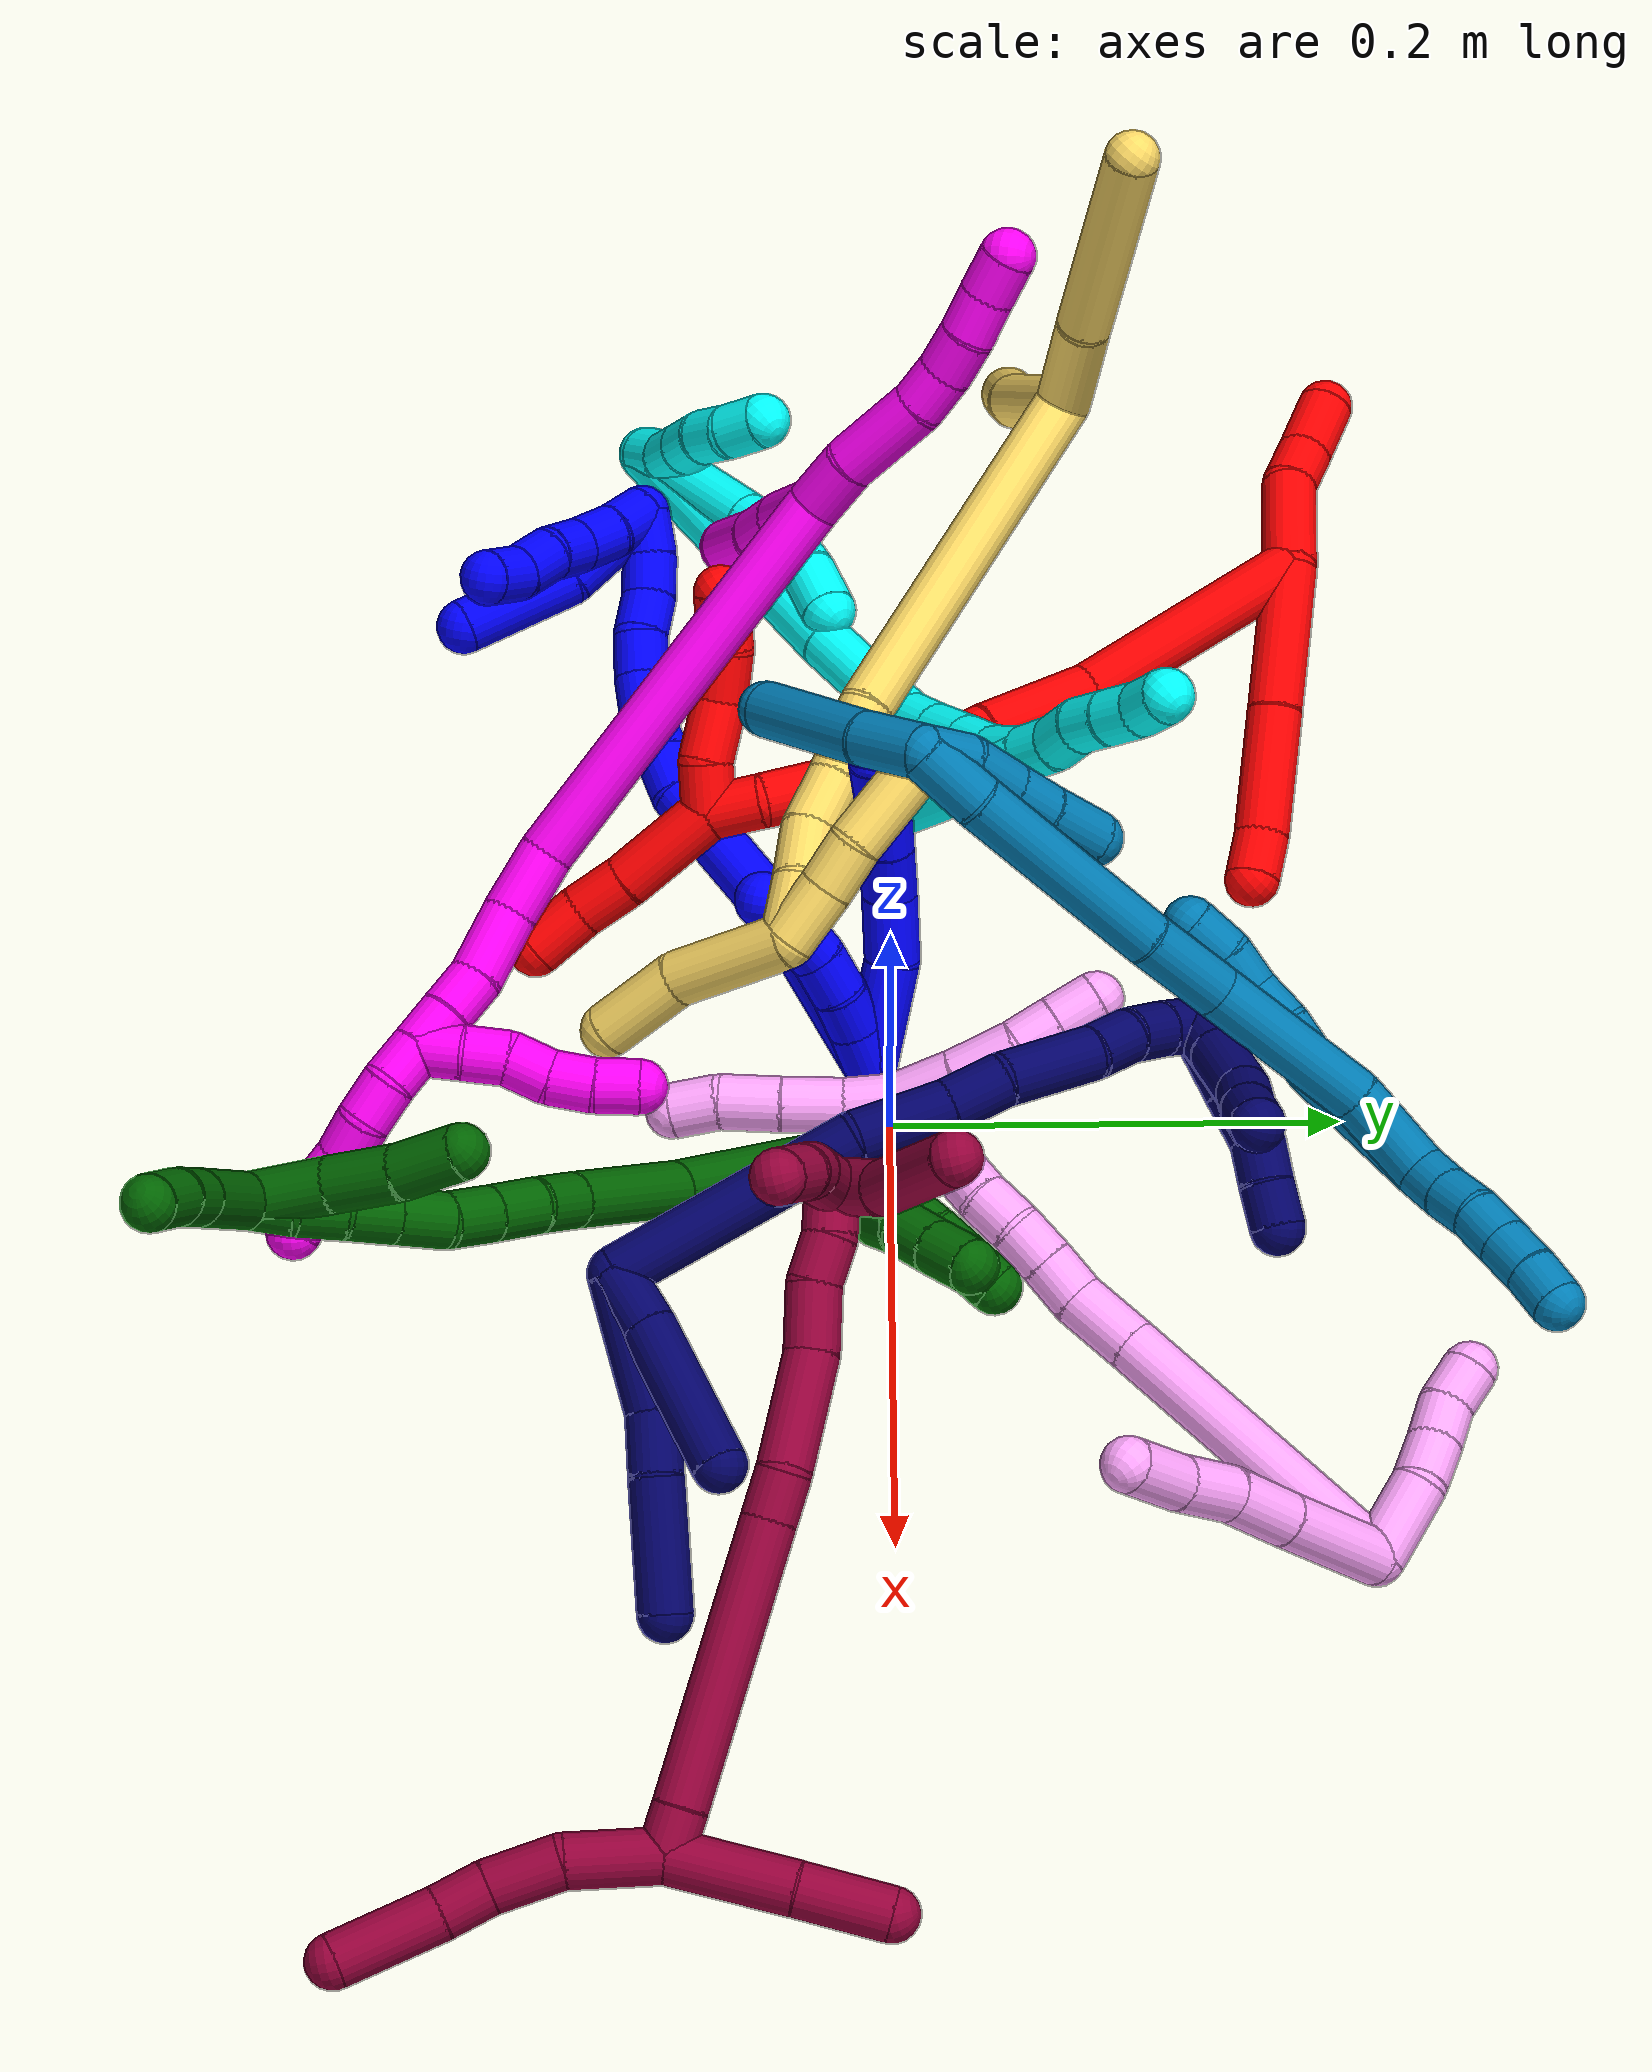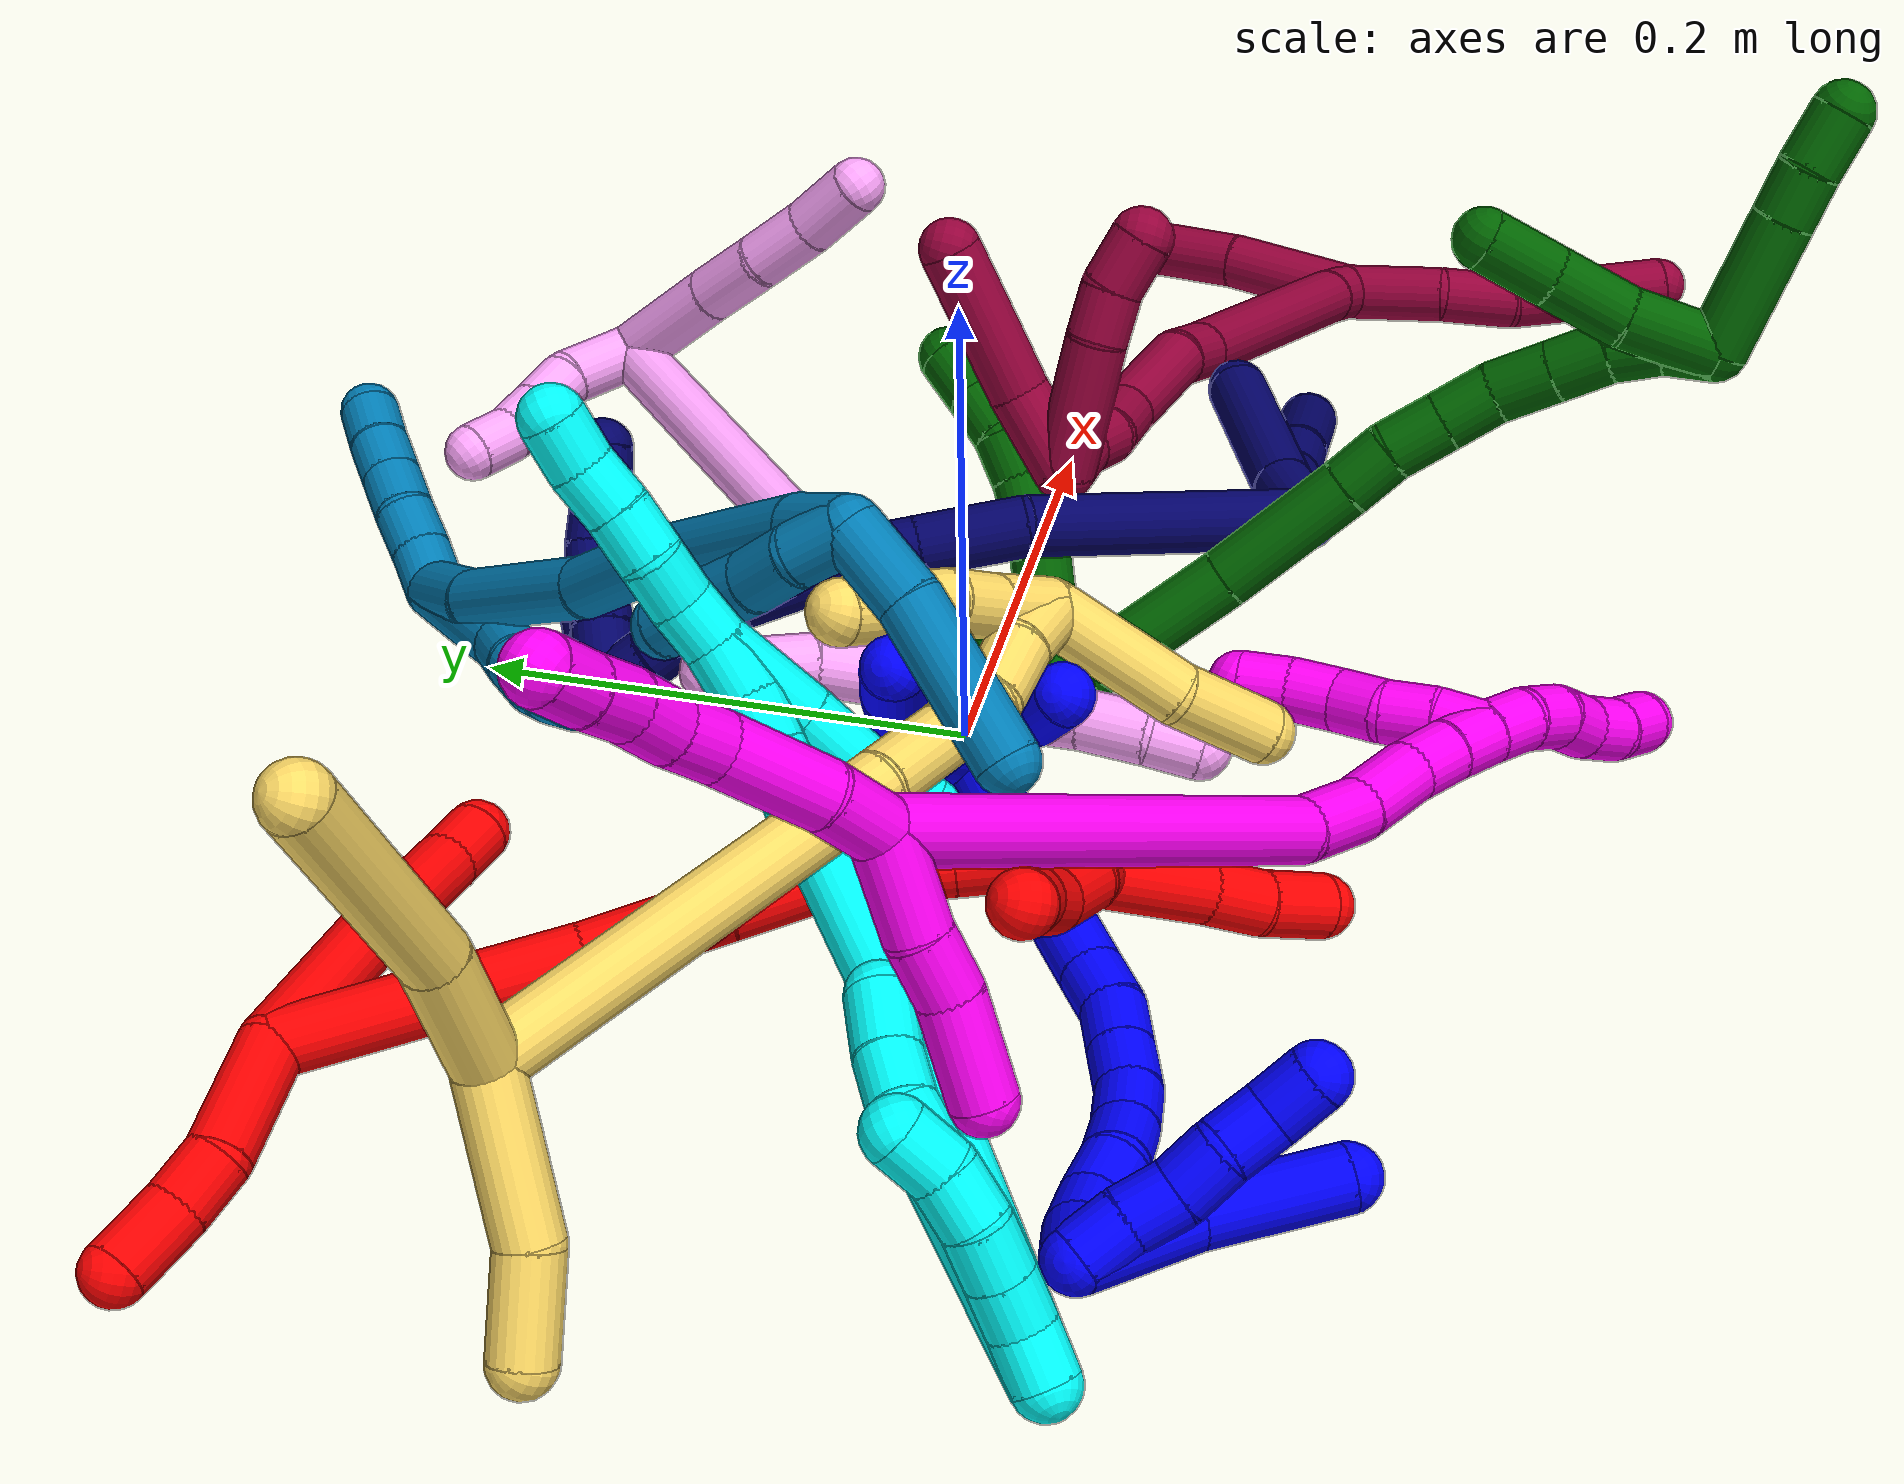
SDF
<sdf version="1.7">
 <world name="default">
  <plugin name="TubeGeneratorPlugin" filename="libtube_generator_plugin.so"/>
  <model name="photoneo_s_sensor">
   <static>1</static>
   <pose>0 0 2 1.57079 1.57079 3.14159</pose>
   <link name="link">
    <inertial><mass>0.1</mass></inertial>
    <sensor name="sensor" type="depth">
     <update_rate>30</update_rate>
     <camera>
      <horizontal_fov>1.22</horizontal_fov>
      <image><width>1920</width><height>1200</height><format>B8G8R8</format></image>
      <clip><near>0.1</near><far>4</far></clip>
      <depth_camera><output>points</output></depth_camera>
     </camera>
     <plugin name="camera_plugin" filename="libgazebo_ros_depth_camera.so">
      <baseline>0.2</baseline>
      <alwaysOn>1</alwaysOn>
      <updateRate>0.0</updateRate>
      <cameraName>camera_ir</cameraName>
      <imageTopicName>/camera/color/image_raw</imageTopicName>
      <cameraInfoTopicName>/camera/color/camera_info</cameraInfoTopicName>
      <depthImageTopicName>/camera/depth/image_raw</depthImageTopicName>
      <depthImageCameraInfoTopicName>/camera/depth/camera_info</depthImageCameraInfoTopicName>
      <pointCloudTopicName>/camera/depth/points</pointCloudTopicName>
      <frameName>fr_optical</frameName>
      <pointCloudCutoff>0.1</pointCloudCutoff>
      <pointCloudCutoffMax>2.0</pointCloudCutoffMax>
      <distortionK1>0</distortionK1>
      <distortionK2>0</distortionK2>
      <distortionK3>0</distortionK3>
      <distortionT1>0</distortionT1>
      <distortionT2>0</distortionT2>
      <CxPrime>0</CxPrime>
      <Cx>0</Cx>
      <Cy>0</Cy>
      <focalLength>0</focalLength>
      <hackBaseline>0</hackBaseline>
     </plugin>
    </sensor>
   </link>
  </model>
  <gravity>0 0 -9.8</gravity>
  <magnetic_field>6e-06 2.3e-05 -4.2e-05</magnetic_field>
  <atmosphere type="adiabatic"/>
  <physics name="default_physics" default="0" type="ode">
   <max_step_size>0.003</max_step_size>
   <real_time_factor>1</real_time_factor>
   <real_time_update_rate>1000</real_time_update_rate>
   <max_contacts>10000</max_contacts>
   <ode>
    <solver>
     <type>quick</type>
     <iters>100</iters>
     <sor>1.3</sor>
     <use_dynamic_moi_rescaling>0</use_dynamic_moi_rescaling>
    </solver>
    <constraints>
     <contact_max_correcting_vel>0</contact_max_correcting_vel>
     <contact_surface_layer>0.001</contact_surface_layer>
     <cfm>0</cfm>
     <erp>0.2</erp>
    </constraints>
   </ode>
  </physics>
  <scene><ambient>0.4 0.4 0.4 1</ambient><background>0.7 0.7 0.7 1</background><shadows>0</shadows></scene>
  <audio><device>default</device></audio>
  <spherical_coordinates>
   <surface_model>EARTH_WGS84</surface_model>
   <latitude_deg>0</latitude_deg>
   <longitude_deg>0</longitude_deg>
   <elevation>0</elevation>
   <heading_deg>0</heading_deg>
  </spherical_coordinates>
  <model name="bin">
   <static>1</static>
   <link name="bottom">
    <collision name="collision-bottom">
     <pose>0 0 -0.01 0 -0 0</pose>
     <geometry><box><size>0.8 0.6 0.02</size></box></geometry>
     <surface>
      <friction><ode><mu>100</mu><mu2>100</mu2></ode></friction>
      <contact><collide_bitmask>65535</collide_bitmask></contact>
     </surface>
    </collision>
   </link>
   <link name="west_wall">
    <collision name="collision-west_wall">
     <pose>-0.41 0 0.1 0 -0 0</pose>
     <geometry><box><size>0.02 0.6 0.2</size></box></geometry>
     <surface>
      <friction><ode><mu>100</mu><mu2>100</mu2></ode></friction>
      <contact><collide_bitmask>65535</collide_bitmask></contact>
     </surface>
    </collision>
   </link>
   <link name="east_wall">
    <collision name="collision-east_wall">
     <pose>0.41 0 0.1 0 -0 0</pose>
     <geometry><box><size>0.02 0.6 0.2</size></box></geometry>
     <surface>
      <friction><ode><mu>100</mu><mu2>100</mu2></ode></friction>
      <contact><collide_bitmask>65535</collide_bitmask></contact>
     </surface>
    </collision>
   </link>
   <link name="south_wall">
    <collision name="collision-south_wall">
     <pose>0 -0.31 0.1 0 -0 0</pose>
     <geometry><box><size>0.8 0.02 0.2</size></box></geometry>
     <surface>
      <friction><ode><mu>100</mu><mu2>100</mu2></ode></friction>
      <contact><collide_bitmask>65535</collide_bitmask></contact>
     </surface>
    </collision>
   </link>
   <link name="north_wall">
    <collision name="collision-north_wall">
     <pose>0 0.31 0.1 0 -0 0</pose>
     <geometry><box><size>0.8 0.02 0.2</size></box></geometry>
     <surface>
      <friction><ode><mu>100</mu><mu2>100</mu2></ode></friction>
      <contact><collide_bitmask>65535</collide_bitmask></contact>
     </surface>
    </collision>
   </link>
  </model>
  <model name="1">
   <static>0</static>
   <link name="1">
    <collision name="collision-cylinder-e_1_2_8">
     <pose>0.001061 0.001206 0.024429 -0.049325 0.043352 -0.00107</pose>
     <geometry><cylinder><radius>0.0125</radius><length>0.048963</length></cylinder></geometry>
     <surface>
      <friction><ode><mu>1.16</mu><mu2>1.16</mu2><slip1>0</slip1><slip2>0</slip2></ode></friction>
      <contact><ode><kp>1e+06</kp><kd>1</kd><max_vel>0</max_vel><min_depth>0.001</min_depth></ode></contact>
     </surface>
    </collision>
    <visual name="visual-cylinder-e_1_2_8">
     <pose>0.001061 0.001206 0.024429 -0.049325 0.043352 -0.00107</pose>
     <geometry><cylinder><radius>0.0125</radius><length>0.048963</length></cylinder></geometry>
     <material><ambient>0 0 1 1</ambient></material>
    </visual>
    <collision name="collision-cylinder-e_2_8_9">
     <pose>0.002393 -0.000683 0.064047 0.200997 0.017505 0.001765</pose>
     <geometry><cylinder><radius>0.0125</radius><length>0.031008</length></cylinder></geometry>
     <surface>
      <friction><ode><mu>1.16</mu><mu2>1.16</mu2><slip1>0</slip1><slip2>0</slip2></ode></friction>
      <contact><ode><kp>1e+06</kp><kd>1</kd><max_vel>0</max_vel><min_depth>0.001</min_depth></ode></contact>
     </surface>
    </collision>
    <visual name="visual-cylinder-e_2_8_9">
     <pose>0.002393 -0.000683 0.064047 0.200997 0.017505 0.001765</pose>
     <geometry><cylinder><radius>0.0125</radius><length>0.031008</length></cylinder></geometry>
     <material><ambient>0 0 1 1</ambient></material>
    </visual>
    <collision name="collision-cylinder-e_3_9_10">
     <pose>0.00589 -0.007187 0.090439 0.295392 0.268801 0.040229</pose>
     <geometry><cylinder><radius>0.0125</radius><length>0.024292</length></cylinder></geometry>
     <surface>
      <friction><ode><mu>1.16</mu><mu2>1.16</mu2><slip1>0</slip1><slip2>0</slip2></ode></friction>
      <contact><ode><kp>1e+06</kp><kd>1</kd><max_vel>0</max_vel><min_depth>0.001</min_depth></ode></contact>
     </surface>
    </collision>
    <visual name="visual-cylinder-e_3_9_10">
     <pose>0.00589 -0.007187 0.090439 0.295392 0.268801 0.040229</pose>
     <geometry><cylinder><radius>0.0125</radius><length>0.024292</length></cylinder></geometry>
     <material><ambient>0 0 1 1</ambient></material>
    </visual>
    <collision name="collision-cylinder-e_4_10_11">
     <pose>0.012008 -0.014117 0.113309 0.293156 0.232999 0.034552</pose>
     <geometry><cylinder><radius>0.0125</radius><length>0.025051</length></cylinder></geometry>
     <surface>
      <friction><ode><mu>1.16</mu><mu2>1.16</mu2><slip1>0</slip1><slip2>0</slip2></ode></friction>
      <contact><ode><kp>1e+06</kp><kd>1</kd><max_vel>0</max_vel><min_depth>0.001</min_depth></ode></contact>
     </surface>
    </collision>
    <visual name="visual-cylinder-e_4_10_11">
     <pose>0.012008 -0.014117 0.113309 0.293156 0.232999 0.034552</pose>
     <geometry><cylinder><radius>0.0125</radius><length>0.025051</length></cylinder></geometry>
     <material><ambient>0 0 1 1</ambient></material>
    </visual>
    <collision name="collision-cylinder-e_5_11_6">
     <pose>0.018158 -0.021445 0.134025 0.398172 0.320372 0.065173</pose>
     <geometry><cylinder><radius>0.0125</radius><length>0.020685</length></cylinder></geometry>
     <surface>
      <friction><ode><mu>1.16</mu><mu2>1.16</mu2><slip1>0</slip1><slip2>0</slip2></ode></friction>
      <contact><ode><kp>1e+06</kp><kd>1</kd><max_vel>0</max_vel><min_depth>0.001</min_depth></ode></contact>
     </surface>
    </collision>
    <visual name="visual-cylinder-e_5_11_6">
     <pose>0.018158 -0.021445 0.134025 0.398172 0.320372 0.065173</pose>
     <geometry><cylinder><radius>0.0125</radius><length>0.020685</length></cylinder></geometry>
     <material><ambient>0 0 1 1</ambient></material>
    </visual>
    <collision name="collision-cylinder-e_1_2_12">
     <pose>0.001103 -0.005106 0.008527 0.539515 0.110496 0.030581</pose>
     <geometry><cylinder><radius>0.0125</radius><length>0.02</length></cylinder></geometry>
     <surface>
      <friction><ode><mu>1.16</mu><mu2>1.16</mu2><slip1>0</slip1><slip2>0</slip2></ode></friction>
      <contact><ode><kp>1e+06</kp><kd>1</kd><max_vel>0</max_vel><min_depth>0.001</min_depth></ode></contact>
     </surface>
    </collision>
    <visual name="visual-cylinder-e_1_2_12">
     <pose>0.001103 -0.005106 0.008527 0.539515 0.110496 0.030581</pose>
     <geometry><cylinder><radius>0.0125</radius><length>0.02</length></cylinder></geometry>
     <material><ambient>0 0 1 1</ambient></material>
    </visual>
    <collision name="collision-cylinder-e_2_12_13">
     <pose>0.003955 -0.015775 0.025178 0.600463 0.175883 0.054579</pose>
     <geometry><cylinder><radius>0.0125</radius><length>0.02</length></cylinder></geometry>
     <surface>
      <friction><ode><mu>1.16</mu><mu2>1.16</mu2><slip1>0</slip1><slip2>0</slip2></ode></friction>
      <contact><ode><kp>1e+06</kp><kd>1</kd><max_vel>0</max_vel><min_depth>0.001</min_depth></ode></contact>
     </surface>
    </collision>
    <visual name="visual-cylinder-e_2_12_13">
     <pose>0.003955 -0.015775 0.025178 0.600463 0.175883 0.054579</pose>
     <geometry><cylinder><radius>0.0125</radius><length>0.02</length></cylinder></geometry>
     <material><ambient>0 0 1 1</ambient></material>
    </visual>
    <collision name="collision-cylinder-e_3_13_14">
     <pose>0.00571 -0.027442 0.041222 0.656551 0.000508 0.000173</pose>
     <geometry><cylinder><radius>0.0125</radius><length>0.02</length></cylinder></geometry>
     <surface>
      <friction><ode><mu>1.16</mu><mu2>1.16</mu2><slip1>0</slip1><slip2>0</slip2></ode></friction>
      <contact><ode><kp>1e+06</kp><kd>1</kd><max_vel>0</max_vel><min_depth>0.001</min_depth></ode></contact>
     </surface>
    </collision>
    <visual name="visual-cylinder-e_3_13_14">
     <pose>0.00571 -0.027442 0.041222 0.656551 0.000508 0.000173</pose>
     <geometry><cylinder><radius>0.0125</radius><length>0.02</length></cylinder></geometry>
     <material><ambient>0 0 1 1</ambient></material>
    </visual>
    <collision name="collision-cylinder-e_4_14_15">
     <pose>0.005777 -0.040984 0.055827 0.838829 0.006204 0.002766</pose>
     <geometry><cylinder><radius>0.0125</radius><length>0.02</length></cylinder></geometry>
     <surface>
      <friction><ode><mu>1.16</mu><mu2>1.16</mu2><slip1>0</slip1><slip2>0</slip2></ode></friction>
      <contact><ode><kp>1e+06</kp><kd>1</kd><max_vel>0</max_vel><min_depth>0.001</min_depth></ode></contact>
     </surface>
    </collision>
    <visual name="visual-cylinder-e_4_14_15">
     <pose>0.005777 -0.040984 0.055827 0.838829 0.006204 0.002766</pose>
     <geometry><cylinder><radius>0.0125</radius><length>0.02</length></cylinder></geometry>
     <material><ambient>0 0 1 1</ambient></material>
    </visual>
    <collision name="collision-cylinder-e_5_15_5">
     <pose>0.007852 -0.056289 0.068347 0.932385 0.202671 0.102243</pose>
     <geometry><cylinder><radius>0.0125</radius><length>0.02</length></cylinder></geometry>
     <surface>
      <friction><ode><mu>1.16</mu><mu2>1.16</mu2><slip1>0</slip1><slip2>0</slip2></ode></friction>
      <contact><ode><kp>1e+06</kp><kd>1</kd><max_vel>0</max_vel><min_depth>0.001</min_depth></ode></contact>
     </surface>
    </collision>
    <visual name="visual-cylinder-e_5_15_5">
     <pose>0.007852 -0.056289 0.068347 0.932385 0.202671 0.102243</pose>
     <geometry><cylinder><radius>0.0125</radius><length>0.02</length></cylinder></geometry>
     <material><ambient>0 0 1 1</ambient></material>
    </visual>
    <collision name="collision-cylinder-e_1_2_16">
     <pose>-0.022949 -0.016901 0.025202 0.590737 -0.647508 -0.203496</pose>
     <geometry><cylinder><radius>0.0125</radius><length>0.076092</length></cylinder></geometry>
     <surface>
      <friction><ode><mu>1.16</mu><mu2>1.16</mu2><slip1>0</slip1><slip2>0</slip2></ode></friction>
      <contact><ode><kp>1e+06</kp><kd>1</kd><max_vel>0</max_vel><min_depth>0.001</min_depth></ode></contact>
     </surface>
    </collision>
    <visual name="visual-cylinder-e_1_2_16">
     <pose>-0.022949 -0.016901 0.025202 0.590737 -0.647508 -0.203496</pose>
     <geometry><cylinder><radius>0.0125</radius><length>0.076092</length></cylinder></geometry>
     <material><ambient>0 0 1 1</ambient></material>
    </visual>
    <collision name="collision-cylinder-e_2_16_17">
     <pose>-0.069117 -0.048439 0.065202 0.779923 -0.839968 -0.363035</pose>
     <geometry><cylinder><radius>0.0125</radius><length>0.062363</length></cylinder></geometry>
     <surface>
      <friction><ode><mu>1.16</mu><mu2>1.16</mu2><slip1>0</slip1><slip2>0</slip2></ode></friction>
      <contact><ode><kp>1e+06</kp><kd>1</kd><max_vel>0</max_vel><min_depth>0.001</min_depth></ode></contact>
     </surface>
    </collision>
    <visual name="visual-cylinder-e_2_16_17">
     <pose>-0.069117 -0.048439 0.065202 0.779923 -0.839968 -0.363035</pose>
     <geometry><cylinder><radius>0.0125</radius><length>0.062363</length></cylinder></geometry>
     <material><ambient>0 0 1 1</ambient></material>
    </visual>
    <collision name="collision-cylinder-e_3_17_18">
     <pose>-0.09948 -0.06788 0.085149 0.750761 -0.79264 -0.326862</pose>
     <geometry><cylinder><radius>0.0125</radius><length>0.020065</length></cylinder></geometry>
     <surface>
      <friction><ode><mu>1.16</mu><mu2>1.16</mu2><slip1>0</slip1><slip2>0</slip2></ode></friction>
      <contact><ode><kp>1e+06</kp><kd>1</kd><max_vel>0</max_vel><min_depth>0.001</min_depth></ode></contact>
     </surface>
    </collision>
    <visual name="visual-cylinder-e_3_17_18">
     <pose>-0.09948 -0.06788 0.085149 0.750761 -0.79264 -0.326862</pose>
     <geometry><cylinder><radius>0.0125</radius><length>0.020065</length></cylinder></geometry>
     <material><ambient>0 0 1 1</ambient></material>
    </visual>
    <collision name="collision-cylinder-e_4_18_19">
     <pose>-0.114319 -0.075281 0.097166 0.361567 -0.808763 -0.156129</pose>
     <geometry><cylinder><radius>0.0125</radius><length>0.021271</length></cylinder></geometry>
     <surface>
      <friction><ode><mu>1.16</mu><mu2>1.16</mu2><slip1>0</slip1><slip2>0</slip2></ode></friction>
      <contact><ode><kp>1e+06</kp><kd>1</kd><max_vel>0</max_vel><min_depth>0.001</min_depth></ode></contact>
     </surface>
    </collision>
    <visual name="visual-cylinder-e_4_18_19">
     <pose>-0.114319 -0.075281 0.097166 0.361567 -0.808763 -0.156129</pose>
     <geometry><cylinder><radius>0.0125</radius><length>0.021271</length></cylinder></geometry>
     <material><ambient>0 0 1 1</ambient></material>
    </visual>
    <collision name="collision-cylinder-e_5_19_20">
     <pose>-0.12931 -0.080364 0.110524 0.365668 -0.809723 -0.158141</pose>
     <geometry><cylinder><radius>0.0125</radius><length>0.020154</length></cylinder></geometry>
     <surface>
      <friction><ode><mu>1.16</mu><mu2>1.16</mu2><slip1>0</slip1><slip2>0</slip2></ode></friction>
      <contact><ode><kp>1e+06</kp><kd>1</kd><max_vel>0</max_vel><min_depth>0.001</min_depth></ode></contact>
     </surface>
    </collision>
    <visual name="visual-cylinder-e_5_19_20">
     <pose>-0.12931 -0.080364 0.110524 0.365668 -0.809723 -0.158141</pose>
     <geometry><cylinder><radius>0.0125</radius><length>0.020154</length></cylinder></geometry>
     <material><ambient>0 0 1 1</ambient></material>
    </visual>
    <collision name="collision-cylinder-e_6_20_21">
     <pose>-0.142746 -0.083665 0.12488 0.103389 -0.660182 -0.035452</pose>
     <geometry><cylinder><radius>0.0125</radius><length>0.020022</length></cylinder></geometry>
     <surface>
      <friction><ode><mu>1.16</mu><mu2>1.16</mu2><slip1>0</slip1><slip2>0</slip2></ode></friction>
      <contact><ode><kp>1e+06</kp><kd>1</kd><max_vel>0</max_vel><min_depth>0.001</min_depth></ode></contact>
     </surface>
    </collision>
    <visual name="visual-cylinder-e_6_20_21">
     <pose>-0.142746 -0.083665 0.12488 0.103389 -0.660182 -0.035452</pose>
     <geometry><cylinder><radius>0.0125</radius><length>0.020022</length></cylinder></geometry>
     <material><ambient>0 0 1 1</ambient></material>
    </visual>
    <collision name="collision-cylinder-e_7_21_22">
     <pose>-0.153916 -0.084648 0.1414 0.01928 -0.526439 -0.005195</pose>
     <geometry><cylinder><radius>0.0125</radius><length>0.020025</length></cylinder></geometry>
     <surface>
      <friction><ode><mu>1.16</mu><mu2>1.16</mu2><slip1>0</slip1><slip2>0</slip2></ode></friction>
      <contact><ode><kp>1e+06</kp><kd>1</kd><max_vel>0</max_vel><min_depth>0.001</min_depth></ode></contact>
     </surface>
    </collision>
    <visual name="visual-cylinder-e_7_21_22">
     <pose>-0.153916 -0.084648 0.1414 0.01928 -0.526439 -0.005195</pose>
     <geometry><cylinder><radius>0.0125</radius><length>0.020025</length></cylinder></geometry>
     <material><ambient>0 0 1 1</ambient></material>
    </visual>
    <collision name="collision-cylinder-e_8_22_23">
     <pose>-0.165016 -0.082278 0.157589 -0.324786 -0.652097 0.110678</pose>
     <geometry><cylinder><radius>0.0125</radius><length>0.020004</length></cylinder></geometry>
     <surface>
      <friction><ode><mu>1.16</mu><mu2>1.16</mu2><slip1>0</slip1><slip2>0</slip2></ode></friction>
      <contact><ode><kp>1e+06</kp><kd>1</kd><max_vel>0</max_vel><min_depth>0.001</min_depth></ode></contact>
     </surface>
    </collision>
    <visual name="visual-cylinder-e_8_22_23">
     <pose>-0.165016 -0.082278 0.157589 -0.324786 -0.652097 0.110678</pose>
     <geometry><cylinder><radius>0.0125</radius><length>0.020004</length></cylinder></geometry>
     <material><ambient>0 0 1 1</ambient></material>
    </visual>
    <collision name="collision-cylinder-e_9_23_24">
     <pose>-0.175643 -0.079549 0.174024 -0.021541 -0.4731 0.005193</pose>
     <geometry><cylinder><radius>0.0125</radius><length>0.020001</length></cylinder></geometry>
     <surface>
      <friction><ode><mu>1.16</mu><mu2>1.16</mu2><slip1>0</slip1><slip2>0</slip2></ode></friction>
      <contact><ode><kp>1e+06</kp><kd>1</kd><max_vel>0</max_vel><min_depth>0.001</min_depth></ode></contact>
     </surface>
    </collision>
    <visual name="visual-cylinder-e_9_23_24">
     <pose>-0.175643 -0.079549 0.174024 -0.021541 -0.4731 0.005193</pose>
     <geometry><cylinder><radius>0.0125</radius><length>0.020001</length></cylinder></geometry>
     <material><ambient>0 0 1 1</ambient></material>
    </visual>
    <collision name="collision-cylinder-e_10_24_1">
     <pose>-0.183867 -0.081389 0.192005 0.220091 -0.375418 -0.041969</pose>
     <geometry><cylinder><radius>0.0125</radius><length>0.020005</length></cylinder></geometry>
     <surface>
      <friction><ode><mu>1.16</mu><mu2>1.16</mu2><slip1>0</slip1><slip2>0</slip2></ode></friction>
      <contact><ode><kp>1e+06</kp><kd>1</kd><max_vel>0</max_vel><min_depth>0.001</min_depth></ode></contact>
     </surface>
    </collision>
    <visual name="visual-cylinder-e_10_24_1">
     <pose>-0.183867 -0.081389 0.192005 0.220091 -0.375418 -0.041969</pose>
     <geometry><cylinder><radius>0.0125</radius><length>0.020005</length></cylinder></geometry>
     <material><ambient>0 0 1 1</ambient></material>
    </visual>
    <collision name="collision-cylinder-e_1_1_25">
     <pose>-0.182602 -0.091266 0.197329 2.01749 0.515898 0.793385</pose>
     <geometry><cylinder><radius>0.0125</radius><length>0.02</length></cylinder></geometry>
     <surface>
      <friction><ode><mu>1.16</mu><mu2>1.16</mu2><slip1>0</slip1><slip2>0</slip2></ode></friction>
      <contact><ode><kp>1e+06</kp><kd>1</kd><max_vel>0</max_vel><min_depth>0.001</min_depth></ode></contact>
     </surface>
    </collision>
    <visual name="visual-cylinder-e_1_1_25">
     <pose>-0.182602 -0.091266 0.197329 2.01749 0.515898 0.793385</pose>
     <geometry><cylinder><radius>0.0125</radius><length>0.02</length></cylinder></geometry>
     <material><ambient>0 0 1 1</ambient></material>
    </visual>
    <collision name="collision-cylinder-e_2_25_26">
     <pose>-0.173987 -0.107837 0.190361 1.92334 0.377019 0.533879</pose>
     <geometry><cylinder><radius>0.0125</radius><length>0.02</length></cylinder></geometry>
     <surface>
      <friction><ode><mu>1.16</mu><mu2>1.16</mu2><slip1>0</slip1><slip2>0</slip2></ode></friction>
      <contact><ode><kp>1e+06</kp><kd>1</kd><max_vel>0</max_vel><min_depth>0.001</min_depth></ode></contact>
     </surface>
    </collision>
    <visual name="visual-cylinder-e_2_25_26">
     <pose>-0.173987 -0.107837 0.190361 1.92334 0.377019 0.533879</pose>
     <geometry><cylinder><radius>0.0125</radius><length>0.02</length></cylinder></geometry>
     <material><ambient>0 0 1 1</ambient></material>
    </visual>
    <collision name="collision-cylinder-e_3_26_27">
     <pose>-0.164595 -0.124681 0.185931 1.71992 0.607744 0.698566</pose>
     <geometry><cylinder><radius>0.0125</radius><length>0.02</length></cylinder></geometry>
     <surface>
      <friction><ode><mu>1.16</mu><mu2>1.16</mu2><slip1>0</slip1><slip2>0</slip2></ode></friction>
      <contact><ode><kp>1e+06</kp><kd>1</kd><max_vel>0</max_vel><min_depth>0.001</min_depth></ode></contact>
     </surface>
    </collision>
    <visual name="visual-cylinder-e_3_26_27">
     <pose>-0.164595 -0.124681 0.185931 1.71992 0.607744 0.698566</pose>
     <geometry><cylinder><radius>0.0125</radius><length>0.02</length></cylinder></geometry>
     <material><ambient>0 0 1 1</ambient></material>
    </visual>
    <collision name="collision-cylinder-e_4_27_28">
     <pose>-0.154075 -0.140648 0.180805 2.03255 0.50184 0.7848</pose>
     <geometry><cylinder><radius>0.0125</radius><length>0.02</length></cylinder></geometry>
     <surface>
      <friction><ode><mu>1.16</mu><mu2>1.16</mu2><slip1>0</slip1><slip2>0</slip2></ode></friction>
      <contact><ode><kp>1e+06</kp><kd>1</kd><max_vel>0</max_vel><min_depth>0.001</min_depth></ode></contact>
     </surface>
    </collision>
    <visual name="visual-cylinder-e_4_27_28">
     <pose>-0.154075 -0.140648 0.180805 2.03255 0.50184 0.7848</pose>
     <geometry><cylinder><radius>0.0125</radius><length>0.02</length></cylinder></geometry>
     <material><ambient>0 0 1 1</ambient></material>
    </visual>
    <collision name="collision-cylinder-e_5_28_4">
     <pose>-0.144123 -0.157057 0.176364 1.63317 0.539967 0.572924</pose>
     <geometry><cylinder><radius>0.0125</radius><length>0.02</length></cylinder></geometry>
     <surface>
      <friction><ode><mu>1.16</mu><mu2>1.16</mu2><slip1>0</slip1><slip2>0</slip2></ode></friction>
      <contact><ode><kp>1e+06</kp><kd>1</kd><max_vel>0</max_vel><min_depth>0.001</min_depth></ode></contact>
     </surface>
    </collision>
    <visual name="visual-cylinder-e_5_28_4">
     <pose>-0.144123 -0.157057 0.176364 1.63317 0.539967 0.572924</pose>
     <geometry><cylinder><radius>0.0125</radius><length>0.02</length></cylinder></geometry>
     <material><ambient>0 0 1 1</ambient></material>
    </visual>
    <collision name="collision-cylinder-e_1_1_29">
     <pose>-0.183481 -0.099522 0.185406 2.34296 0.178438 0.417794</pose>
     <geometry><cylinder><radius>0.0125</radius><length>0.045676</length></cylinder></geometry>
     <surface>
      <friction><ode><mu>1.16</mu><mu2>1.16</mu2><slip1>0</slip1><slip2>0</slip2></ode></friction>
      <contact><ode><kp>1e+06</kp><kd>1</kd><max_vel>0</max_vel><min_depth>0.001</min_depth></ode></contact>
     </surface>
    </collision>
    <visual name="visual-cylinder-e_1_1_29">
     <pose>-0.183481 -0.099522 0.185406 2.34296 0.178438 0.417794</pose>
     <geometry><cylinder><radius>0.0125</radius><length>0.045676</length></cylinder></geometry>
     <material><ambient>0 0 1 1</ambient></material>
    </visual>
    <collision name="collision-cylinder-e_2_29_3">
     <pose>-0.176687 -0.139571 0.157204 2.05254 0.101062 0.166635</pose>
     <geometry><cylinder><radius>0.0125</radius><length>0.054324</length></cylinder></geometry>
     <surface>
      <friction><ode><mu>1.16</mu><mu2>1.16</mu2><slip1>0</slip1><slip2>0</slip2></ode></friction>
      <contact><ode><kp>1e+06</kp><kd>1</kd><max_vel>0</max_vel><min_depth>0.001</min_depth></ode></contact>
     </surface>
    </collision>
    <visual name="visual-cylinder-e_2_29_3">
     <pose>-0.176687 -0.139571 0.157204 2.05254 0.101062 0.166635</pose>
     <geometry><cylinder><radius>0.0125</radius><length>0.054324</length></cylinder></geometry>
     <material><ambient>0 0 1 1</ambient></material>
    </visual>
    <collision name="collision-sphere-3">
     <pose>-0.173947 -0.163519 0.144683 0 -0 0</pose>
     <geometry><sphere><radius>0.0125</radius></sphere></geometry>
     <surface>
      <friction><ode><mu>1.16</mu><mu2>1.16</mu2><slip1>0</slip1><slip2>0</slip2></ode></friction>
      <contact><ode><kp>1e+06</kp><kd>1</kd><max_vel>0</max_vel><min_depth>0.001</min_depth></ode></contact>
     </surface>
    </collision>
    <visual name="visual-sphere-3">
     <pose>-0.173947 -0.163519 0.144683 0 -0 0</pose>
     <geometry><sphere><radius>0.0125</radius></sphere></geometry>
     <material><ambient>0 0 1 1</ambient></material>
    </visual>
    <collision name="collision-sphere-29">
     <pose>-0.179428 -0.115623 0.169725 0 -0 0</pose>
     <geometry><sphere><radius>0.0125</radius></sphere></geometry>
     <surface>
      <friction><ode><mu>1.16</mu><mu2>1.16</mu2><slip1>0</slip1><slip2>0</slip2></ode></friction>
      <contact><ode><kp>1e+06</kp><kd>1</kd><max_vel>0</max_vel><min_depth>0.001</min_depth></ode></contact>
     </surface>
    </collision>
    <visual name="visual-sphere-29">
     <pose>-0.179428 -0.115623 0.169725 0 -0 0</pose>
     <geometry><sphere><radius>0.0125</radius></sphere></geometry>
     <material><ambient>0 0 1 1</ambient></material>
    </visual>
    <collision name="collision-sphere-4">
     <pose>-0.138982 -0.165618 0.17583 0 -0 0</pose>
     <geometry><sphere><radius>0.0125</radius></sphere></geometry>
     <surface>
      <friction><ode><mu>1.16</mu><mu2>1.16</mu2><slip1>0</slip1><slip2>0</slip2></ode></friction>
      <contact><ode><kp>1e+06</kp><kd>1</kd><max_vel>0</max_vel><min_depth>0.001</min_depth></ode></contact>
     </surface>
    </collision>
    <visual name="visual-sphere-4">
     <pose>-0.138982 -0.165618 0.17583 0 -0 0</pose>
     <geometry><sphere><radius>0.0125</radius></sphere></geometry>
     <material><ambient>0 0 1 1</ambient></material>
    </visual>
    <collision name="collision-sphere-28">
     <pose>-0.149264 -0.148497 0.176899 0 -0 0</pose>
     <geometry><sphere><radius>0.0125</radius></sphere></geometry>
     <surface>
      <friction><ode><mu>1.16</mu><mu2>1.16</mu2><slip1>0</slip1><slip2>0</slip2></ode></friction>
      <contact><ode><kp>1e+06</kp><kd>1</kd><max_vel>0</max_vel><min_depth>0.001</min_depth></ode></contact>
     </surface>
    </collision>
    <visual name="visual-sphere-28">
     <pose>-0.149264 -0.148497 0.176899 0 -0 0</pose>
     <geometry><sphere><radius>0.0125</radius></sphere></geometry>
     <material><ambient>0 0 1 1</ambient></material>
    </visual>
    <collision name="collision-sphere-27">
     <pose>-0.158885 -0.132799 0.184711 0 -0 0</pose>
     <geometry><sphere><radius>0.0125</radius></sphere></geometry>
     <surface>
      <friction><ode><mu>1.16</mu><mu2>1.16</mu2><slip1>0</slip1><slip2>0</slip2></ode></friction>
      <contact><ode><kp>1e+06</kp><kd>1</kd><max_vel>0</max_vel><min_depth>0.001</min_depth></ode></contact>
     </surface>
    </collision>
    <visual name="visual-sphere-27">
     <pose>-0.158885 -0.132799 0.184711 0 -0 0</pose>
     <geometry><sphere><radius>0.0125</radius></sphere></geometry>
     <material><ambient>0 0 1 1</ambient></material>
    </visual>
    <collision name="collision-sphere-26">
     <pose>-0.170305 -0.116562 0.18715 0 -0 0</pose>
     <geometry><sphere><radius>0.0125</radius></sphere></geometry>
     <surface>
      <friction><ode><mu>1.16</mu><mu2>1.16</mu2><slip1>0</slip1><slip2>0</slip2></ode></friction>
      <contact><ode><kp>1e+06</kp><kd>1</kd><max_vel>0</max_vel><min_depth>0.001</min_depth></ode></contact>
     </surface>
    </collision>
    <visual name="visual-sphere-26">
     <pose>-0.170305 -0.116562 0.18715 0 -0 0</pose>
     <geometry><sphere><radius>0.0125</radius></sphere></geometry>
     <material><ambient>0 0 1 1</ambient></material>
    </visual>
    <collision name="collision-sphere-25">
     <pose>-0.177668 -0.099111 0.193571 0 -0 0</pose>
     <geometry><sphere><radius>0.0125</radius></sphere></geometry>
     <surface>
      <friction><ode><mu>1.16</mu><mu2>1.16</mu2><slip1>0</slip1><slip2>0</slip2></ode></friction>
      <contact><ode><kp>1e+06</kp><kd>1</kd><max_vel>0</max_vel><min_depth>0.001</min_depth></ode></contact>
     </surface>
    </collision>
    <visual name="visual-sphere-25">
     <pose>-0.177668 -0.099111 0.193571 0 -0 0</pose>
     <geometry><sphere><radius>0.0125</radius></sphere></geometry>
     <material><ambient>0 0 1 1</ambient></material>
    </visual>
    <collision name="collision-sphere-1">
     <pose>-0.187535 -0.083421 0.201086 0 -0 0</pose>
     <geometry><sphere><radius>0.0125</radius></sphere></geometry>
     <surface>
      <friction><ode><mu>1.16</mu><mu2>1.16</mu2><slip1>0</slip1><slip2>0</slip2></ode></friction>
      <contact><ode><kp>1e+06</kp><kd>1</kd><max_vel>0</max_vel><min_depth>0.001</min_depth></ode></contact>
     </surface>
    </collision>
    <visual name="visual-sphere-1">
     <pose>-0.187535 -0.083421 0.201086 0 -0 0</pose>
     <geometry><sphere><radius>0.0125</radius></sphere></geometry>
     <material><ambient>0 0 1 1</ambient></material>
    </visual>
    <collision name="collision-sphere-24">
     <pose>-0.1802 -0.079358 0.182924 0 -0 0</pose>
     <geometry><sphere><radius>0.0125</radius></sphere></geometry>
     <surface>
      <friction><ode><mu>1.16</mu><mu2>1.16</mu2><slip1>0</slip1><slip2>0</slip2></ode></friction>
      <contact><ode><kp>1e+06</kp><kd>1</kd><max_vel>0</max_vel><min_depth>0.001</min_depth></ode></contact>
     </surface>
    </collision>
    <visual name="visual-sphere-24">
     <pose>-0.1802 -0.079358 0.182924 0 -0 0</pose>
     <geometry><sphere><radius>0.0125</radius></sphere></geometry>
     <material><ambient>0 0 1 1</ambient></material>
    </visual>
    <collision name="collision-sphere-23">
     <pose>-0.171086 -0.079741 0.165123 0 -0 0</pose>
     <geometry><sphere><radius>0.0125</radius></sphere></geometry>
     <surface>
      <friction><ode><mu>1.16</mu><mu2>1.16</mu2><slip1>0</slip1><slip2>0</slip2></ode></friction>
      <contact><ode><kp>1e+06</kp><kd>1</kd><max_vel>0</max_vel><min_depth>0.001</min_depth></ode></contact>
     </surface>
    </collision>
    <visual name="visual-sphere-23">
     <pose>-0.171086 -0.079741 0.165123 0 -0 0</pose>
     <geometry><sphere><radius>0.0125</radius></sphere></geometry>
     <material><ambient>0 0 1 1</ambient></material>
    </visual>
    <collision name="collision-sphere-22">
     <pose>-0.158946 -0.084815 0.150055 0 -0 0</pose>
     <geometry><sphere><radius>0.0125</radius></sphere></geometry>
     <surface>
      <friction><ode><mu>1.16</mu><mu2>1.16</mu2><slip1>0</slip1><slip2>0</slip2></ode></friction>
      <contact><ode><kp>1e+06</kp><kd>1</kd><max_vel>0</max_vel><min_depth>0.001</min_depth></ode></contact>
     </surface>
    </collision>
    <visual name="visual-sphere-22">
     <pose>-0.158946 -0.084815 0.150055 0 -0 0</pose>
     <geometry><sphere><radius>0.0125</radius></sphere></geometry>
     <material><ambient>0 0 1 1</ambient></material>
    </visual>
    <collision name="collision-sphere-21">
     <pose>-0.148885 -0.084481 0.132745 0 -0 0</pose>
     <geometry><sphere><radius>0.0125</radius></sphere></geometry>
     <surface>
      <friction><ode><mu>1.16</mu><mu2>1.16</mu2><slip1>0</slip1><slip2>0</slip2></ode></friction>
      <contact><ode><kp>1e+06</kp><kd>1</kd><max_vel>0</max_vel><min_depth>0.001</min_depth></ode></contact>
     </surface>
    </collision>
    <visual name="visual-sphere-21">
     <pose>-0.148885 -0.084481 0.132745 0 -0 0</pose>
     <geometry><sphere><radius>0.0125</radius></sphere></geometry>
     <material><ambient>0 0 1 1</ambient></material>
    </visual>
    <collision name="collision-sphere-6">
     <pose>0.021415 -0.025252 0.143074 0 -0 0</pose>
     <geometry><sphere><radius>0.0125</radius></sphere></geometry>
     <surface>
      <friction><ode><mu>1.16</mu><mu2>1.16</mu2><slip1>0</slip1><slip2>0</slip2></ode></friction>
      <contact><ode><kp>1e+06</kp><kd>1</kd><max_vel>0</max_vel><min_depth>0.001</min_depth></ode></contact>
     </surface>
    </collision>
    <visual name="visual-sphere-6">
     <pose>0.021415 -0.025252 0.143074 0 -0 0</pose>
     <geometry><sphere><radius>0.0125</radius></sphere></geometry>
     <material><ambient>0 0 1 1</ambient></material>
    </visual>
    <collision name="collision-sphere-11">
     <pose>0.0149 -0.017639 0.124977 0 -0 0</pose>
     <geometry><sphere><radius>0.0125</radius></sphere></geometry>
     <surface>
      <friction><ode><mu>1.16</mu><mu2>1.16</mu2><slip1>0</slip1><slip2>0</slip2></ode></friction>
      <contact><ode><kp>1e+06</kp><kd>1</kd><max_vel>0</max_vel><min_depth>0.001</min_depth></ode></contact>
     </surface>
    </collision>
    <visual name="visual-sphere-11">
     <pose>0.0149 -0.017639 0.124977 0 -0 0</pose>
     <geometry><sphere><radius>0.0125</radius></sphere></geometry>
     <material><ambient>0 0 1 1</ambient></material>
    </visual>
    <collision name="collision-sphere-10">
     <pose>0.009116 -0.010596 0.101642 0 -0 0</pose>
     <geometry><sphere><radius>0.0125</radius></sphere></geometry>
     <surface>
      <friction><ode><mu>1.16</mu><mu2>1.16</mu2><slip1>0</slip1><slip2>0</slip2></ode></friction>
      <contact><ode><kp>1e+06</kp><kd>1</kd><max_vel>0</max_vel><min_depth>0.001</min_depth></ode></contact>
     </surface>
    </collision>
    <visual name="visual-sphere-10">
     <pose>0.009116 -0.010596 0.101642 0 -0 0</pose>
     <geometry><sphere><radius>0.0125</radius></sphere></geometry>
     <material><ambient>0 0 1 1</ambient></material>
    </visual>
    <collision name="collision-sphere-9">
     <pose>0.002665 -0.003778 0.079236 0 -0 0</pose>
     <geometry><sphere><radius>0.0125</radius></sphere></geometry>
     <surface>
      <friction><ode><mu>1.16</mu><mu2>1.16</mu2><slip1>0</slip1><slip2>0</slip2></ode></friction>
      <contact><ode><kp>1e+06</kp><kd>1</kd><max_vel>0</max_vel><min_depth>0.001</min_depth></ode></contact>
     </surface>
    </collision>
    <visual name="visual-sphere-9">
     <pose>0.002665 -0.003778 0.079236 0 -0 0</pose>
     <geometry><sphere><radius>0.0125</radius></sphere></geometry>
     <material><ambient>0 0 1 1</ambient></material>
    </visual>
    <collision name="collision-sphere-2">
     <geometry><sphere><radius>0.0125</radius></sphere></geometry>
     <surface>
      <friction><ode><mu>1.16</mu><mu2>1.16</mu2><slip1>0</slip1><slip2>0</slip2></ode></friction>
      <contact><ode><kp>1e+06</kp><kd>1</kd><max_vel>0</max_vel><min_depth>0.001</min_depth></ode></contact>
     </surface>
    </collision>
    <visual name="visual-sphere-2">
     <geometry><sphere><radius>0.0125</radius></sphere></geometry>
     <material><ambient>0 0 1 1</ambient></material>
    </visual>
    <collision name="collision-sphere-19">
     <pose>-0.122013 -0.077879 0.104034 0 -0 0</pose>
     <geometry><sphere><radius>0.0125</radius></sphere></geometry>
     <surface>
      <friction><ode><mu>1.16</mu><mu2>1.16</mu2><slip1>0</slip1><slip2>0</slip2></ode></friction>
      <contact><ode><kp>1e+06</kp><kd>1</kd><max_vel>0</max_vel><min_depth>0.001</min_depth></ode></contact>
     </surface>
    </collision>
    <visual name="visual-sphere-19">
     <pose>-0.122013 -0.077879 0.104034 0 -0 0</pose>
     <geometry><sphere><radius>0.0125</radius></sphere></geometry>
     <material><ambient>0 0 1 1</ambient></material>
    </visual>
    <collision name="collision-sphere-8">
     <pose>0.002122 0.002412 0.048858 0 -0 0</pose>
     <geometry><sphere><radius>0.0125</radius></sphere></geometry>
     <surface>
      <friction><ode><mu>1.16</mu><mu2>1.16</mu2><slip1>0</slip1><slip2>0</slip2></ode></friction>
      <contact><ode><kp>1e+06</kp><kd>1</kd><max_vel>0</max_vel><min_depth>0.001</min_depth></ode></contact>
     </surface>
    </collision>
    <visual name="visual-sphere-8">
     <pose>0.002122 0.002412 0.048858 0 -0 0</pose>
     <geometry><sphere><radius>0.0125</radius></sphere></geometry>
     <material><ambient>0 0 1 1</ambient></material>
    </visual>
    <collision name="collision-sphere-12">
     <pose>0.002205 -0.010212 0.017055 0 -0 0</pose>
     <geometry><sphere><radius>0.0125</radius></sphere></geometry>
     <surface>
      <friction><ode><mu>1.16</mu><mu2>1.16</mu2><slip1>0</slip1><slip2>0</slip2></ode></friction>
      <contact><ode><kp>1e+06</kp><kd>1</kd><max_vel>0</max_vel><min_depth>0.001</min_depth></ode></contact>
     </surface>
    </collision>
    <visual name="visual-sphere-12">
     <pose>0.002205 -0.010212 0.017055 0 -0 0</pose>
     <geometry><sphere><radius>0.0125</radius></sphere></geometry>
     <material><ambient>0 0 1 1</ambient></material>
    </visual>
    <collision name="collision-sphere-13">
     <pose>0.005705 -0.021338 0.033301 0 -0 0</pose>
     <geometry><sphere><radius>0.0125</radius></sphere></geometry>
     <surface>
      <friction><ode><mu>1.16</mu><mu2>1.16</mu2><slip1>0</slip1><slip2>0</slip2></ode></friction>
      <contact><ode><kp>1e+06</kp><kd>1</kd><max_vel>0</max_vel><min_depth>0.001</min_depth></ode></contact>
     </surface>
    </collision>
    <visual name="visual-sphere-13">
     <pose>0.005705 -0.021338 0.033301 0 -0 0</pose>
     <geometry><sphere><radius>0.0125</radius></sphere></geometry>
     <material><ambient>0 0 1 1</ambient></material>
    </visual>
    <collision name="collision-sphere-14">
     <pose>0.005715 -0.033546 0.049143 0 -0 0</pose>
     <geometry><sphere><radius>0.0125</radius></sphere></geometry>
     <surface>
      <friction><ode><mu>1.16</mu><mu2>1.16</mu2><slip1>0</slip1><slip2>0</slip2></ode></friction>
      <contact><ode><kp>1e+06</kp><kd>1</kd><max_vel>0</max_vel><min_depth>0.001</min_depth></ode></contact>
     </surface>
    </collision>
    <visual name="visual-sphere-14">
     <pose>0.005715 -0.033546 0.049143 0 -0 0</pose>
     <geometry><sphere><radius>0.0125</radius></sphere></geometry>
     <material><ambient>0 0 1 1</ambient></material>
    </visual>
    <collision name="collision-sphere-15">
     <pose>0.005839 -0.048423 0.06251 0 -0 0</pose>
     <geometry><sphere><radius>0.0125</radius></sphere></geometry>
     <surface>
      <friction><ode><mu>1.16</mu><mu2>1.16</mu2><slip1>0</slip1><slip2>0</slip2></ode></friction>
      <contact><ode><kp>1e+06</kp><kd>1</kd><max_vel>0</max_vel><min_depth>0.001</min_depth></ode></contact>
     </surface>
    </collision>
    <visual name="visual-sphere-15">
     <pose>0.005839 -0.048423 0.06251 0 -0 0</pose>
     <geometry><sphere><radius>0.0125</radius></sphere></geometry>
     <material><ambient>0 0 1 1</ambient></material>
    </visual>
    <collision name="collision-sphere-5">
     <pose>0.009865 -0.064155 0.074184 0 -0 0</pose>
     <geometry><sphere><radius>0.0125</radius></sphere></geometry>
     <surface>
      <friction><ode><mu>1.16</mu><mu2>1.16</mu2><slip1>0</slip1><slip2>0</slip2></ode></friction>
      <contact><ode><kp>1e+06</kp><kd>1</kd><max_vel>0</max_vel><min_depth>0.001</min_depth></ode></contact>
     </surface>
    </collision>
    <visual name="visual-sphere-5">
     <pose>0.009865 -0.064155 0.074184 0 -0 0</pose>
     <geometry><sphere><radius>0.0125</radius></sphere></geometry>
     <material><ambient>0 0 1 1</ambient></material>
    </visual>
    <collision name="collision-sphere-16">
     <pose>-0.045899 -0.033803 0.050405 0 -0 0</pose>
     <geometry><sphere><radius>0.0125</radius></sphere></geometry>
     <surface>
      <friction><ode><mu>1.16</mu><mu2>1.16</mu2><slip1>0</slip1><slip2>0</slip2></ode></friction>
      <contact><ode><kp>1e+06</kp><kd>1</kd><max_vel>0</max_vel><min_depth>0.001</min_depth></ode></contact>
     </surface>
    </collision>
    <visual name="visual-sphere-16">
     <pose>-0.045899 -0.033803 0.050405 0 -0 0</pose>
     <geometry><sphere><radius>0.0125</radius></sphere></geometry>
     <material><ambient>0 0 1 1</ambient></material>
    </visual>
    <collision name="collision-sphere-17">
     <pose>-0.092335 -0.063075 0.08 0 -0 0</pose>
     <geometry><sphere><radius>0.0125</radius></sphere></geometry>
     <surface>
      <friction><ode><mu>1.16</mu><mu2>1.16</mu2><slip1>0</slip1><slip2>0</slip2></ode></friction>
      <contact><ode><kp>1e+06</kp><kd>1</kd><max_vel>0</max_vel><min_depth>0.001</min_depth></ode></contact>
     </surface>
    </collision>
    <visual name="visual-sphere-17">
     <pose>-0.092335 -0.063075 0.08 0 -0 0</pose>
     <geometry><sphere><radius>0.0125</radius></sphere></geometry>
     <material><ambient>0 0 1 1</ambient></material>
    </visual>
    <collision name="collision-sphere-18">
     <pose>-0.106625 -0.072684 0.090298 0 -0 0</pose>
     <geometry><sphere><radius>0.0125</radius></sphere></geometry>
     <surface>
      <friction><ode><mu>1.16</mu><mu2>1.16</mu2><slip1>0</slip1><slip2>0</slip2></ode></friction>
      <contact><ode><kp>1e+06</kp><kd>1</kd><max_vel>0</max_vel><min_depth>0.001</min_depth></ode></contact>
     </surface>
    </collision>
    <visual name="visual-sphere-18">
     <pose>-0.106625 -0.072684 0.090298 0 -0 0</pose>
     <geometry><sphere><radius>0.0125</radius></sphere></geometry>
     <material><ambient>0 0 1 1</ambient></material>
    </visual>
    <collision name="collision-sphere-20">
     <pose>-0.136606 -0.082849 0.117015 0 -0 0</pose>
     <geometry><sphere><radius>0.0125</radius></sphere></geometry>
     <surface>
      <friction><ode><mu>1.16</mu><mu2>1.16</mu2><slip1>0</slip1><slip2>0</slip2></ode></friction>
      <contact><ode><kp>1e+06</kp><kd>1</kd><max_vel>0</max_vel><min_depth>0.001</min_depth></ode></contact>
     </surface>
    </collision>
    <visual name="visual-sphere-20">
     <pose>-0.136606 -0.082849 0.117015 0 -0 0</pose>
     <geometry><sphere><radius>0.0125</radius></sphere></geometry>
     <material><ambient>0 0 1 1</ambient></material>
    </visual>
    <inertial>
     <pose>-0.083274 -0.060705 0.104519 0 -0 0</pose>
     <mass>0.75</mass>
     <inertia>
      <ixx>0.000103</ixx>
      <ixy>0</ixy>
      <ixz>0</ixz>
      <iyy>5.2e-05</iyy>
      <iyz>0</iyz>
      <izz>0.000127</izz>
     </inertia>
    </inertial>
   </link>
   <pose>-0.025879 -0.008499 0.011148 -0.460833 -0.796638 0.409471</pose>
  </model>
  <model name="2">
   <static>0</static>
   <link name="2">
    <collision name="collision-cylinder-e_1_2_8">
     <pose>0.021739 0.016576 -0.021664 -2.48846 0.672867 -1.60286</pose>
     <geometry><cylinder><radius>0.0125</radius><length>0.069761</length></cylinder></geometry>
     <surface>
      <friction><ode><mu>1.16</mu><mu2>1.16</mu2><slip1>0</slip1><slip2>0</slip2></ode></friction>
      <contact><ode><kp>1e+06</kp><kd>1</kd><max_vel>0</max_vel><min_depth>0.001</min_depth></ode></contact>
     </surface>
    </collision>
    <visual name="visual-cylinder-e_1_2_8">
     <pose>0.021739 0.016576 -0.021664 -2.48846 0.672867 -1.60286</pose>
     <geometry><cylinder><radius>0.0125</radius><length>0.069761</length></cylinder></geometry>
     <material><ambient>1 0 0 1</ambient></material>
    </visual>
    <collision name="collision-cylinder-e_2_8_9">
     <pose>0.05988 0.048154 -0.062423 -2.47566 0.594062 -1.44898</pose>
     <geometry><cylinder><radius>0.0125</radius><length>0.058608</length></cylinder></geometry>
     <surface>
      <friction><ode><mu>1.16</mu><mu2>1.16</mu2><slip1>0</slip1><slip2>0</slip2></ode></friction>
      <contact><ode><kp>1e+06</kp><kd>1</kd><max_vel>0</max_vel><min_depth>0.001</min_depth></ode></contact>
     </surface>
    </collision>
    <visual name="visual-cylinder-e_2_8_9">
     <pose>0.05988 0.048154 -0.062423 -2.47566 0.594062 -1.44898</pose>
     <geometry><cylinder><radius>0.0125</radius><length>0.058608</length></cylinder></geometry>
     <material><ambient>1 0 0 1</ambient></material>
    </visual>
    <collision name="collision-cylinder-e_3_9_6">
     <pose>0.083345 0.067137 -0.088676 -2.63408 0.711617 -1.92299</pose>
     <geometry><cylinder><radius>0.0125</radius><length>0.021631</length></cylinder></geometry>
     <surface>
      <friction><ode><mu>1.16</mu><mu2>1.16</mu2><slip1>0</slip1><slip2>0</slip2></ode></friction>
      <contact><ode><kp>1e+06</kp><kd>1</kd><max_vel>0</max_vel><min_depth>0.001</min_depth></ode></contact>
     </surface>
    </collision>
    <visual name="visual-cylinder-e_3_9_6">
     <pose>0.083345 0.067137 -0.088676 -2.63408 0.711617 -1.92299</pose>
     <geometry><cylinder><radius>0.0125</radius><length>0.021631</length></cylinder></geometry>
     <material><ambient>1 0 0 1</ambient></material>
    </visual>
    <collision name="collision-cylinder-e_1_2_10">
     <pose>-0.020127 -0.008536 0.009895 0.711813 -0.994918 -0.398359</pose>
     <geometry><cylinder><radius>0.0125</radius><length>0.047995</length></cylinder></geometry>
     <surface>
      <friction><ode><mu>1.16</mu><mu2>1.16</mu2><slip1>0</slip1><slip2>0</slip2></ode></friction>
      <contact><ode><kp>1e+06</kp><kd>1</kd><max_vel>0</max_vel><min_depth>0.001</min_depth></ode></contact>
     </surface>
    </collision>
    <visual name="visual-cylinder-e_1_2_10">
     <pose>-0.020127 -0.008536 0.009895 0.711813 -0.994918 -0.398359</pose>
     <geometry><cylinder><radius>0.0125</radius><length>0.047995</length></cylinder></geometry>
     <material><ambient>1 0 0 1</ambient></material>
    </visual>
    <collision name="collision-cylinder-e_2_10_11">
     <pose>-0.049562 -0.017587 0.026062 0.081875 -0.976299 -0.043494</pose>
     <geometry><cylinder><radius>0.0125</radius><length>0.022471</length></cylinder></geometry>
     <surface>
      <friction><ode><mu>1.16</mu><mu2>1.16</mu2><slip1>0</slip1><slip2>0</slip2></ode></friction>
      <contact><ode><kp>1e+06</kp><kd>1</kd><max_vel>0</max_vel><min_depth>0.001</min_depth></ode></contact>
     </surface>
    </collision>
    <visual name="visual-cylinder-e_2_10_11">
     <pose>-0.049562 -0.017587 0.026062 0.081875 -0.976299 -0.043494</pose>
     <geometry><cylinder><radius>0.0125</radius><length>0.022471</length></cylinder></geometry>
     <material><ambient>1 0 0 1</ambient></material>
    </visual>
    <collision name="collision-cylinder-e_3_11_5">
     <pose>-0.069992 -0.019937 0.041873 0.190077 -0.852854 -0.08656</pose>
     <geometry><cylinder><radius>0.0125</radius><length>0.029534</length></cylinder></geometry>
     <surface>
      <friction><ode><mu>1.16</mu><mu2>1.16</mu2><slip1>0</slip1><slip2>0</slip2></ode></friction>
      <contact><ode><kp>1e+06</kp><kd>1</kd><max_vel>0</max_vel><min_depth>0.001</min_depth></ode></contact>
     </surface>
    </collision>
    <visual name="visual-cylinder-e_3_11_5">
     <pose>-0.069992 -0.019937 0.041873 0.190077 -0.852854 -0.08656</pose>
     <geometry><cylinder><radius>0.0125</radius><length>0.029534</length></cylinder></geometry>
     <material><ambient>1 0 0 1</ambient></material>
    </visual>
    <collision name="collision-cylinder-e_1_2_12">
     <pose>0.021918 -0.015957 -0.049402 2.82917 0.399486 1.81926</pose>
     <geometry><cylinder><radius>0.0125</radius><length>0.112705</length></cylinder></geometry>
     <surface>
      <friction><ode><mu>1.16</mu><mu2>1.16</mu2><slip1>0</slip1><slip2>0</slip2></ode></friction>
      <contact><ode><kp>1e+06</kp><kd>1</kd><max_vel>0</max_vel><min_depth>0.001</min_depth></ode></contact>
     </surface>
    </collision>
    <visual name="visual-cylinder-e_1_2_12">
     <pose>0.021918 -0.015957 -0.049402 2.82917 0.399486 1.81926</pose>
     <geometry><cylinder><radius>0.0125</radius><length>0.112705</length></cylinder></geometry>
     <material><ambient>1 0 0 1</ambient></material>
    </visual>
    <collision name="collision-cylinder-e_2_12_13">
     <pose>0.055186 -0.043953 -0.119834 2.62167 0.43805 1.39367</pose>
     <geometry><cylinder><radius>0.0125</radius><length>0.053517</length></cylinder></geometry>
     <surface>
      <friction><ode><mu>1.16</mu><mu2>1.16</mu2><slip1>0</slip1><slip2>0</slip2></ode></friction>
      <contact><ode><kp>1e+06</kp><kd>1</kd><max_vel>0</max_vel><min_depth>0.001</min_depth></ode></contact>
     </surface>
    </collision>
    <visual name="visual-cylinder-e_2_12_13">
     <pose>0.055186 -0.043953 -0.119834 2.62167 0.43805 1.39367</pose>
     <geometry><cylinder><radius>0.0125</radius><length>0.053517</length></cylinder></geometry>
     <material><ambient>1 0 0 1</ambient></material>
    </visual>
    <collision name="collision-cylinder-e_3_13_14">
     <pose>0.074341 -0.062567 -0.155798 2.72682 0.446118 1.64588</pose>
     <geometry><cylinder><radius>0.0125</radius><length>0.036177</length></cylinder></geometry>
     <surface>
      <friction><ode><mu>1.16</mu><mu2>1.16</mu2><slip1>0</slip1><slip2>0</slip2></ode></friction>
      <contact><ode><kp>1e+06</kp><kd>1</kd><max_vel>0</max_vel><min_depth>0.001</min_depth></ode></contact>
     </surface>
    </collision>
    <visual name="visual-cylinder-e_3_13_14">
     <pose>0.074341 -0.062567 -0.155798 2.72682 0.446118 1.64588</pose>
     <geometry><cylinder><radius>0.0125</radius><length>0.036177</length></cylinder></geometry>
     <material><ambient>1 0 0 1</ambient></material>
    </visual>
    <collision name="collision-cylinder-e_4_14_15">
     <pose>0.087074 -0.081989 -0.190192 2.55811 0.208313 0.669938</pose>
     <geometry><cylinder><radius>0.0125</radius><length>0.047665</length></cylinder></geometry>
     <surface>
      <friction><ode><mu>1.16</mu><mu2>1.16</mu2><slip1>0</slip1><slip2>0</slip2></ode></friction>
      <contact><ode><kp>1e+06</kp><kd>1</kd><max_vel>0</max_vel><min_depth>0.001</min_depth></ode></contact>
     </surface>
    </collision>
    <visual name="visual-cylinder-e_4_14_15">
     <pose>0.087074 -0.081989 -0.190192 2.55811 0.208313 0.669938</pose>
     <geometry><cylinder><radius>0.0125</radius><length>0.047665</length></cylinder></geometry>
     <material><ambient>1 0 0 1</ambient></material>
    </visual>
    <collision name="collision-cylinder-e_5_15_16">
     <pose>0.094625 -0.101646 -0.220012 2.56004 0.208373 0.672307</pose>
     <geometry><cylinder><radius>0.0125</radius><length>0.025346</length></cylinder></geometry>
     <surface>
      <friction><ode><mu>1.16</mu><mu2>1.16</mu2><slip1>0</slip1><slip2>0</slip2></ode></friction>
      <contact><ode><kp>1e+06</kp><kd>1</kd><max_vel>0</max_vel><min_depth>0.001</min_depth></ode></contact>
     </surface>
    </collision>
    <visual name="visual-cylinder-e_5_15_16">
     <pose>0.094625 -0.101646 -0.220012 2.56004 0.208373 0.672307</pose>
     <geometry><cylinder><radius>0.0125</radius><length>0.025346</length></cylinder></geometry>
     <material><ambient>1 0 0 1</ambient></material>
    </visual>
    <collision name="collision-cylinder-e_6_16_1">
     <pose>0.095778 -0.114055 -0.241221 2.66525 -0.119735 -0.48409</pose>
     <geometry><cylinder><radius>0.0125</radius><length>0.024591</length></cylinder></geometry>
     <surface>
      <friction><ode><mu>1.16</mu><mu2>1.16</mu2><slip1>0</slip1><slip2>0</slip2></ode></friction>
      <contact><ode><kp>1e+06</kp><kd>1</kd><max_vel>0</max_vel><min_depth>0.001</min_depth></ode></contact>
     </surface>
    </collision>
    <visual name="visual-cylinder-e_6_16_1">
     <pose>0.095778 -0.114055 -0.241221 2.66525 -0.119735 -0.48409</pose>
     <geometry><cylinder><radius>0.0125</radius><length>0.024591</length></cylinder></geometry>
     <material><ambient>1 0 0 1</ambient></material>
    </visual>
    <collision name="collision-cylinder-e_1_1_17">
     <pose>0.091854 -0.128387 -0.245002 0.890466 -0.215109 -0.102954</pose>
     <geometry><cylinder><radius>0.0125</radius><length>0.023001</length></cylinder></geometry>
     <surface>
      <friction><ode><mu>1.16</mu><mu2>1.16</mu2><slip1>0</slip1><slip2>0</slip2></ode></friction>
      <contact><ode><kp>1e+06</kp><kd>1</kd><max_vel>0</max_vel><min_depth>0.001</min_depth></ode></contact>
     </surface>
    </collision>
    <visual name="visual-cylinder-e_1_1_17">
     <pose>0.091854 -0.128387 -0.245002 0.890466 -0.215109 -0.102954</pose>
     <geometry><cylinder><radius>0.0125</radius><length>0.023001</length></cylinder></geometry>
     <material><ambient>1 0 0 1</ambient></material>
    </visual>
    <collision name="collision-cylinder-e_2_17_18">
     <pose>0.08426 -0.144152 -0.226871 0.566149 -0.373619 -0.109852</pose>
     <geometry><cylinder><radius>0.0125</radius><length>0.028159</length></cylinder></geometry>
     <surface>
      <friction><ode><mu>1.16</mu><mu2>1.16</mu2><slip1>0</slip1><slip2>0</slip2></ode></friction>
      <contact><ode><kp>1e+06</kp><kd>1</kd><max_vel>0</max_vel><min_depth>0.001</min_depth></ode></contact>
     </surface>
    </collision>
    <visual name="visual-cylinder-e_2_17_18">
     <pose>0.08426 -0.144152 -0.226871 0.566149 -0.373619 -0.109852</pose>
     <geometry><cylinder><radius>0.0125</radius><length>0.028159</length></cylinder></geometry>
     <material><ambient>1 0 0 1</ambient></material>
    </visual>
    <collision name="collision-cylinder-e_3_18_19">
     <pose>0.078042 -0.158724 -0.20706 0.711464 -0.093169 -0.034637</pose>
     <geometry><cylinder><radius>0.0125</radius><length>0.0232</length></cylinder></geometry>
     <surface>
      <friction><ode><mu>1.16</mu><mu2>1.16</mu2><slip1>0</slip1><slip2>0</slip2></ode></friction>
      <contact><ode><kp>1e+06</kp><kd>1</kd><max_vel>0</max_vel><min_depth>0.001</min_depth></ode></contact>
     </surface>
    </collision>
    <visual name="visual-cylinder-e_3_18_19">
     <pose>0.078042 -0.158724 -0.20706 0.711464 -0.093169 -0.034637</pose>
     <geometry><cylinder><radius>0.0125</radius><length>0.0232</length></cylinder></geometry>
     <material><ambient>1 0 0 1</ambient></material>
    </visual>
    <collision name="collision-cylinder-e_4_19_4">
     <pose>0.075079 -0.176398 -0.190688 0.925747 -0.147531 -0.073723</pose>
     <geometry><cylinder><radius>0.0125</radius><length>0.02564</length></cylinder></geometry>
     <surface>
      <friction><ode><mu>1.16</mu><mu2>1.16</mu2><slip1>0</slip1><slip2>0</slip2></ode></friction>
      <contact><ode><kp>1e+06</kp><kd>1</kd><max_vel>0</max_vel><min_depth>0.001</min_depth></ode></contact>
     </surface>
    </collision>
    <visual name="visual-cylinder-e_4_19_4">
     <pose>0.075079 -0.176398 -0.190688 0.925747 -0.147531 -0.073723</pose>
     <geometry><cylinder><radius>0.0125</radius><length>0.02564</length></cylinder></geometry>
     <material><ambient>1 0 0 1</ambient></material>
    </visual>
    <collision name="collision-cylinder-e_1_1_20">
     <pose>0.094371 -0.120292 -0.27633 3.11522 0.00258 0.195023</pose>
     <geometry><cylinder><radius>0.0125</radius><length>0.048539</length></cylinder></geometry>
     <surface>
      <friction><ode><mu>1.16</mu><mu2>1.16</mu2><slip1>0</slip1><slip2>0</slip2></ode></friction>
      <contact><ode><kp>1e+06</kp><kd>1</kd><max_vel>0</max_vel><min_depth>0.001</min_depth></ode></contact>
     </surface>
    </collision>
    <visual name="visual-cylinder-e_1_1_20">
     <pose>0.094371 -0.120292 -0.27633 3.11522 0.00258 0.195023</pose>
     <geometry><cylinder><radius>0.0125</radius><length>0.048539</length></cylinder></geometry>
     <material><ambient>1 0 0 1</ambient></material>
    </visual>
    <collision name="collision-cylinder-e_2_20_21">
     <pose>0.09377 -0.122255 -0.312772 3.03342 -0.054133 -0.927444</pose>
     <geometry><cylinder><radius>0.0125</radius><length>0.02454</length></cylinder></geometry>
     <surface>
      <friction><ode><mu>1.16</mu><mu2>1.16</mu2><slip1>0</slip1><slip2>0</slip2></ode></friction>
      <contact><ode><kp>1e+06</kp><kd>1</kd><max_vel>0</max_vel><min_depth>0.001</min_depth></ode></contact>
     </surface>
    </collision>
    <visual name="visual-cylinder-e_2_20_21">
     <pose>0.09377 -0.122255 -0.312772 3.03342 -0.054133 -0.927444</pose>
     <geometry><cylinder><radius>0.0125</radius><length>0.02454</length></cylinder></geometry>
     <material><ambient>1 0 0 1</ambient></material>
    </visual>
    <collision name="collision-cylinder-e_3_21_3">
     <pose>0.094411 -0.124173 -0.338336 3.09715 0.097112 2.28374</pose>
     <geometry><cylinder><radius>0.0125</radius><length>0.026921</length></cylinder></geometry>
     <surface>
      <friction><ode><mu>1.16</mu><mu2>1.16</mu2><slip1>0</slip1><slip2>0</slip2></ode></friction>
      <contact><ode><kp>1e+06</kp><kd>1</kd><max_vel>0</max_vel><min_depth>0.001</min_depth></ode></contact>
     </surface>
    </collision>
    <visual name="visual-cylinder-e_3_21_3">
     <pose>0.094411 -0.124173 -0.338336 3.09715 0.097112 2.28374</pose>
     <geometry><cylinder><radius>0.0125</radius><length>0.026921</length></cylinder></geometry>
     <material><ambient>1 0 0 1</ambient></material>
    </visual>
    <collision name="collision-sphere-3">
     <pose>0.095717 -0.124768 -0.35172 0 -0 0</pose>
     <geometry><sphere><radius>0.0125</radius></sphere></geometry>
     <surface>
      <friction><ode><mu>1.16</mu><mu2>1.16</mu2><slip1>0</slip1><slip2>0</slip2></ode></friction>
      <contact><ode><kp>1e+06</kp><kd>1</kd><max_vel>0</max_vel><min_depth>0.001</min_depth></ode></contact>
     </surface>
    </collision>
    <visual name="visual-sphere-3">
     <pose>0.095717 -0.124768 -0.35172 0 -0 0</pose>
     <geometry><sphere><radius>0.0125</radius></sphere></geometry>
     <material><ambient>1 0 0 1</ambient></material>
    </visual>
    <collision name="collision-sphere-21">
     <pose>0.093106 -0.123578 -0.324952 0 -0 0</pose>
     <geometry><sphere><radius>0.0125</radius></sphere></geometry>
     <surface>
      <friction><ode><mu>1.16</mu><mu2>1.16</mu2><slip1>0</slip1><slip2>0</slip2></ode></friction>
      <contact><ode><kp>1e+06</kp><kd>1</kd><max_vel>0</max_vel><min_depth>0.001</min_depth></ode></contact>
     </surface>
    </collision>
    <visual name="visual-sphere-21">
     <pose>0.093106 -0.123578 -0.324952 0 -0 0</pose>
     <geometry><sphere><radius>0.0125</radius></sphere></geometry>
     <material><ambient>1 0 0 1</ambient></material>
    </visual>
    <collision name="collision-sphere-20">
     <pose>0.094434 -0.120932 -0.300591 0 -0 0</pose>
     <geometry><sphere><radius>0.0125</radius></sphere></geometry>
     <surface>
      <friction><ode><mu>1.16</mu><mu2>1.16</mu2><slip1>0</slip1><slip2>0</slip2></ode></friction>
      <contact><ode><kp>1e+06</kp><kd>1</kd><max_vel>0</max_vel><min_depth>0.001</min_depth></ode></contact>
     </surface>
    </collision>
    <visual name="visual-sphere-20">
     <pose>0.094434 -0.120932 -0.300591 0 -0 0</pose>
     <geometry><sphere><radius>0.0125</radius></sphere></geometry>
     <material><ambient>1 0 0 1</ambient></material>
    </visual>
    <collision name="collision-sphere-4">
     <pose>0.073194 -0.186531 -0.183064 0 -0 0</pose>
     <geometry><sphere><radius>0.0125</radius></sphere></geometry>
     <surface>
      <friction><ode><mu>1.16</mu><mu2>1.16</mu2><slip1>0</slip1><slip2>0</slip2></ode></friction>
      <contact><ode><kp>1e+06</kp><kd>1</kd><max_vel>0</max_vel><min_depth>0.001</min_depth></ode></contact>
     </surface>
    </collision>
    <visual name="visual-sphere-4">
     <pose>0.073194 -0.186531 -0.183064 0 -0 0</pose>
     <geometry><sphere><radius>0.0125</radius></sphere></geometry>
     <material><ambient>1 0 0 1</ambient></material>
    </visual>
    <collision name="collision-sphere-11">
     <pose>-0.05887 -0.018102 0.032334 0 -0 0</pose>
     <geometry><sphere><radius>0.0125</radius></sphere></geometry>
     <surface>
      <friction><ode><mu>1.16</mu><mu2>1.16</mu2><slip1>0</slip1><slip2>0</slip2></ode></friction>
      <contact><ode><kp>1e+06</kp><kd>1</kd><max_vel>0</max_vel><min_depth>0.001</min_depth></ode></contact>
     </surface>
    </collision>
    <visual name="visual-sphere-11">
     <pose>-0.05887 -0.018102 0.032334 0 -0 0</pose>
     <geometry><sphere><radius>0.0125</radius></sphere></geometry>
     <material><ambient>1 0 0 1</ambient></material>
    </visual>
    <collision name="collision-sphere-10">
     <pose>-0.040254 -0.017073 0.01979 0 -0 0</pose>
     <geometry><sphere><radius>0.0125</radius></sphere></geometry>
     <surface>
      <friction><ode><mu>1.16</mu><mu2>1.16</mu2><slip1>0</slip1><slip2>0</slip2></ode></friction>
      <contact><ode><kp>1e+06</kp><kd>1</kd><max_vel>0</max_vel><min_depth>0.001</min_depth></ode></contact>
     </surface>
    </collision>
    <visual name="visual-sphere-10">
     <pose>-0.040254 -0.017073 0.01979 0 -0 0</pose>
     <geometry><sphere><radius>0.0125</radius></sphere></geometry>
     <material><ambient>1 0 0 1</ambient></material>
    </visual>
    <collision name="collision-sphere-6">
     <pose>0.090408 0.071118 -0.095834 0 -0 0</pose>
     <geometry><sphere><radius>0.0125</radius></sphere></geometry>
     <surface>
      <friction><ode><mu>1.16</mu><mu2>1.16</mu2><slip1>0</slip1><slip2>0</slip2></ode></friction>
      <contact><ode><kp>1e+06</kp><kd>1</kd><max_vel>0</max_vel><min_depth>0.001</min_depth></ode></contact>
     </surface>
    </collision>
    <visual name="visual-sphere-6">
     <pose>0.090408 0.071118 -0.095834 0 -0 0</pose>
     <geometry><sphere><radius>0.0125</radius></sphere></geometry>
     <material><ambient>1 0 0 1</ambient></material>
    </visual>
    <collision name="collision-sphere-9">
     <pose>0.076282 0.063156 -0.081518 0 -0 0</pose>
     <geometry><sphere><radius>0.0125</radius></sphere></geometry>
     <surface>
      <friction><ode><mu>1.16</mu><mu2>1.16</mu2><slip1>0</slip1><slip2>0</slip2></ode></friction>
      <contact><ode><kp>1e+06</kp><kd>1</kd><max_vel>0</max_vel><min_depth>0.001</min_depth></ode></contact>
     </surface>
    </collision>
    <visual name="visual-sphere-9">
     <pose>0.076282 0.063156 -0.081518 0 -0 0</pose>
     <geometry><sphere><radius>0.0125</radius></sphere></geometry>
     <material><ambient>1 0 0 1</ambient></material>
    </visual>
    <collision name="collision-sphere-2">
     <geometry><sphere><radius>0.0125</radius></sphere></geometry>
     <surface>
      <friction><ode><mu>1.16</mu><mu2>1.16</mu2><slip1>0</slip1><slip2>0</slip2></ode></friction>
      <contact><ode><kp>1e+06</kp><kd>1</kd><max_vel>0</max_vel><min_depth>0.001</min_depth></ode></contact>
     </surface>
    </collision>
    <visual name="visual-sphere-2">
     <geometry><sphere><radius>0.0125</radius></sphere></geometry>
     <material><ambient>1 0 0 1</ambient></material>
    </visual>
    <collision name="collision-sphere-19">
     <pose>0.076963 -0.166266 -0.198312 0 -0 0</pose>
     <geometry><sphere><radius>0.0125</radius></sphere></geometry>
     <surface>
      <friction><ode><mu>1.16</mu><mu2>1.16</mu2><slip1>0</slip1><slip2>0</slip2></ode></friction>
      <contact><ode><kp>1e+06</kp><kd>1</kd><max_vel>0</max_vel><min_depth>0.001</min_depth></ode></contact>
     </surface>
    </collision>
    <visual name="visual-sphere-19">
     <pose>0.076963 -0.166266 -0.198312 0 -0 0</pose>
     <geometry><sphere><radius>0.0125</radius></sphere></geometry>
     <material><ambient>1 0 0 1</ambient></material>
    </visual>
    <collision name="collision-sphere-8">
     <pose>0.043477 0.033152 -0.043327 0 -0 0</pose>
     <geometry><sphere><radius>0.0125</radius></sphere></geometry>
     <surface>
      <friction><ode><mu>1.16</mu><mu2>1.16</mu2><slip1>0</slip1><slip2>0</slip2></ode></friction>
      <contact><ode><kp>1e+06</kp><kd>1</kd><max_vel>0</max_vel><min_depth>0.001</min_depth></ode></contact>
     </surface>
    </collision>
    <visual name="visual-sphere-8">
     <pose>0.043477 0.033152 -0.043327 0 -0 0</pose>
     <geometry><sphere><radius>0.0125</radius></sphere></geometry>
     <material><ambient>1 0 0 1</ambient></material>
    </visual>
    <collision name="collision-sphere-5">
     <pose>-0.081114 -0.021773 0.051413 0 -0 0</pose>
     <geometry><sphere><radius>0.0125</radius></sphere></geometry>
     <surface>
      <friction><ode><mu>1.16</mu><mu2>1.16</mu2><slip1>0</slip1><slip2>0</slip2></ode></friction>
      <contact><ode><kp>1e+06</kp><kd>1</kd><max_vel>0</max_vel><min_depth>0.001</min_depth></ode></contact>
     </surface>
    </collision>
    <visual name="visual-sphere-5">
     <pose>-0.081114 -0.021773 0.051413 0 -0 0</pose>
     <geometry><sphere><radius>0.0125</radius></sphere></geometry>
     <material><ambient>1 0 0 1</ambient></material>
    </visual>
    <collision name="collision-sphere-12">
     <pose>0.043836 -0.031914 -0.098804 0 -0 0</pose>
     <geometry><sphere><radius>0.0125</radius></sphere></geometry>
     <surface>
      <friction><ode><mu>1.16</mu><mu2>1.16</mu2><slip1>0</slip1><slip2>0</slip2></ode></friction>
      <contact><ode><kp>1e+06</kp><kd>1</kd><max_vel>0</max_vel><min_depth>0.001</min_depth></ode></contact>
     </surface>
    </collision>
    <visual name="visual-sphere-12">
     <pose>0.043836 -0.031914 -0.098804 0 -0 0</pose>
     <geometry><sphere><radius>0.0125</radius></sphere></geometry>
     <material><ambient>1 0 0 1</ambient></material>
    </visual>
    <collision name="collision-sphere-13">
     <pose>0.066536 -0.055991 -0.140864 0 -0 0</pose>
     <geometry><sphere><radius>0.0125</radius></sphere></geometry>
     <surface>
      <friction><ode><mu>1.16</mu><mu2>1.16</mu2><slip1>0</slip1><slip2>0</slip2></ode></friction>
      <contact><ode><kp>1e+06</kp><kd>1</kd><max_vel>0</max_vel><min_depth>0.001</min_depth></ode></contact>
     </surface>
    </collision>
    <visual name="visual-sphere-13">
     <pose>0.066536 -0.055991 -0.140864 0 -0 0</pose>
     <geometry><sphere><radius>0.0125</radius></sphere></geometry>
     <material><ambient>1 0 0 1</ambient></material>
    </visual>
    <collision name="collision-sphere-14">
     <pose>0.082146 -0.069143 -0.170733 0 -0 0</pose>
     <geometry><sphere><radius>0.0125</radius></sphere></geometry>
     <surface>
      <friction><ode><mu>1.16</mu><mu2>1.16</mu2><slip1>0</slip1><slip2>0</slip2></ode></friction>
      <contact><ode><kp>1e+06</kp><kd>1</kd><max_vel>0</max_vel><min_depth>0.001</min_depth></ode></contact>
     </surface>
    </collision>
    <visual name="visual-sphere-14">
     <pose>0.082146 -0.069143 -0.170733 0 -0 0</pose>
     <geometry><sphere><radius>0.0125</radius></sphere></geometry>
     <material><ambient>1 0 0 1</ambient></material>
    </visual>
    <collision name="collision-sphere-15">
     <pose>0.092003 -0.094835 -0.209651 0 -0 0</pose>
     <geometry><sphere><radius>0.0125</radius></sphere></geometry>
     <surface>
      <friction><ode><mu>1.16</mu><mu2>1.16</mu2><slip1>0</slip1><slip2>0</slip2></ode></friction>
      <contact><ode><kp>1e+06</kp><kd>1</kd><max_vel>0</max_vel><min_depth>0.001</min_depth></ode></contact>
     </surface>
    </collision>
    <visual name="visual-sphere-15">
     <pose>0.092003 -0.094835 -0.209651 0 -0 0</pose>
     <geometry><sphere><radius>0.0125</radius></sphere></geometry>
     <material><ambient>1 0 0 1</ambient></material>
    </visual>
    <collision name="collision-sphere-16">
     <pose>0.097246 -0.108457 -0.230372 0 -0 0</pose>
     <geometry><sphere><radius>0.0125</radius></sphere></geometry>
     <surface>
      <friction><ode><mu>1.16</mu><mu2>1.16</mu2><slip1>0</slip1><slip2>0</slip2></ode></friction>
      <contact><ode><kp>1e+06</kp><kd>1</kd><max_vel>0</max_vel><min_depth>0.001</min_depth></ode></contact>
     </surface>
    </collision>
    <visual name="visual-sphere-16">
     <pose>0.097246 -0.108457 -0.230372 0 -0 0</pose>
     <geometry><sphere><radius>0.0125</radius></sphere></geometry>
     <material><ambient>1 0 0 1</ambient></material>
    </visual>
    <collision name="collision-sphere-1">
     <pose>0.094309 -0.119652 -0.252069 0 -0 0</pose>
     <geometry><sphere><radius>0.0125</radius></sphere></geometry>
     <surface>
      <friction><ode><mu>1.16</mu><mu2>1.16</mu2><slip1>0</slip1><slip2>0</slip2></ode></friction>
      <contact><ode><kp>1e+06</kp><kd>1</kd><max_vel>0</max_vel><min_depth>0.001</min_depth></ode></contact>
     </surface>
    </collision>
    <visual name="visual-sphere-1">
     <pose>0.094309 -0.119652 -0.252069 0 -0 0</pose>
     <geometry><sphere><radius>0.0125</radius></sphere></geometry>
     <material><ambient>1 0 0 1</ambient></material>
    </visual>
    <collision name="collision-sphere-18">
     <pose>0.079122 -0.151183 -0.215808 0 -0 0</pose>
     <geometry><sphere><radius>0.0125</radius></sphere></geometry>
     <surface>
      <friction><ode><mu>1.16</mu><mu2>1.16</mu2><slip1>0</slip1><slip2>0</slip2></ode></friction>
      <contact><ode><kp>1e+06</kp><kd>1</kd><max_vel>0</max_vel><min_depth>0.001</min_depth></ode></contact>
     </surface>
    </collision>
    <visual name="visual-sphere-18">
     <pose>0.079122 -0.151183 -0.215808 0 -0 0</pose>
     <geometry><sphere><radius>0.0125</radius></sphere></geometry>
     <material><ambient>1 0 0 1</ambient></material>
    </visual>
    <collision name="collision-sphere-17">
     <pose>0.089399 -0.137121 -0.237934 0 -0 0</pose>
     <geometry><sphere><radius>0.0125</radius></sphere></geometry>
     <surface>
      <friction><ode><mu>1.16</mu><mu2>1.16</mu2><slip1>0</slip1><slip2>0</slip2></ode></friction>
      <contact><ode><kp>1e+06</kp><kd>1</kd><max_vel>0</max_vel><min_depth>0.001</min_depth></ode></contact>
     </surface>
    </collision>
    <visual name="visual-sphere-17">
     <pose>0.089399 -0.137121 -0.237934 0 -0 0</pose>
     <geometry><sphere><radius>0.0125</radius></sphere></geometry>
     <material><ambient>1 0 0 1</ambient></material>
    </visual>
    <inertial>
     <pose>0.049791 -0.052087 -0.126527 0 -0 0</pose>
     <mass>0.75</mass>
     <inertia>
      <ixx>0.000115</ixx>
      <ixy>0</ixy>
      <ixz>0</ixz>
      <iyy>0.000148</iyy>
      <iyz>0</iyz>
      <izz>-6.3e-05</izz>
     </inertia>
    </inertial>
   </link>
   <pose>-0.260955 0.184415 0.032598 -0.897017 -0.768754 0.0682</pose>
  </model>
  <model name="3">
   <static>0</static>
   <link name="3">
    <collision name="collision-cylinder-e_1_2_8">
     <pose>0.004031 0.005004 -0.03776 -3.00983 0.105435 -1.34921</pose>
     <geometry><cylinder><radius>0.0125</radius><length>0.076605</length></cylinder></geometry>
     <surface>
      <friction><ode><mu>1.16</mu><mu2>1.16</mu2><slip1>0</slip1><slip2>0</slip2></ode></friction>
      <contact><ode><kp>1e+06</kp><kd>1</kd><max_vel>0</max_vel><min_depth>0.001</min_depth></ode></contact>
     </surface>
    </collision>
    <visual name="visual-cylinder-e_1_2_8">
     <pose>0.004031 0.005004 -0.03776 -3.00983 0.105435 -1.34921</pose>
     <geometry><cylinder><radius>0.0125</radius><length>0.076605</length></cylinder></geometry>
     <material><ambient>0.003922 1 0.996078 1</ambient></material>
    </visual>
    <collision name="collision-cylinder-e_2_8_9">
     <pose>0.009393 0.012314 -0.089437 -2.97743 0.094057 -1.03926</pose>
     <geometry><cylinder><radius>0.0125</radius><length>0.028339</length></cylinder></geometry>
     <surface>
      <friction><ode><mu>1.16</mu><mu2>1.16</mu2><slip1>0</slip1><slip2>0</slip2></ode></friction>
      <contact><ode><kp>1e+06</kp><kd>1</kd><max_vel>0</max_vel><min_depth>0.001</min_depth></ode></contact>
     </surface>
    </collision>
    <visual name="visual-cylinder-e_2_8_9">
     <pose>0.009393 0.012314 -0.089437 -2.97743 0.094057 -1.03926</pose>
     <geometry><cylinder><radius>0.0125</radius><length>0.028339</length></cylinder></geometry>
     <material><ambient>0.003922 1 0.996078 1</ambient></material>
    </visual>
    <collision name="collision-cylinder-e_3_9_10">
     <pose>0.010192 0.013303 -0.113333 3.01038 -0.052744 -0.76357</pose>
     <geometry><cylinder><radius>0.0125</radius><length>0.020159</length></cylinder></geometry>
     <surface>
      <friction><ode><mu>1.16</mu><mu2>1.16</mu2><slip1>0</slip1><slip2>0</slip2></ode></friction>
      <contact><ode><kp>1e+06</kp><kd>1</kd><max_vel>0</max_vel><min_depth>0.001</min_depth></ode></contact>
     </surface>
    </collision>
    <visual name="visual-cylinder-e_3_9_10">
     <pose>0.010192 0.013303 -0.113333 3.01038 -0.052744 -0.76357</pose>
     <geometry><cylinder><radius>0.0125</radius><length>0.020159</length></cylinder></geometry>
     <material><ambient>0.003922 1 0.996078 1</ambient></material>
    </visual>
    <collision name="collision-cylinder-e_4_10_6">
     <pose>0.009266 0.008985 -0.135387 2.89806 -0.03168 -0.257473</pose>
     <geometry><cylinder><radius>0.0125</radius><length>0.024896</length></cylinder></geometry>
     <surface>
      <friction><ode><mu>1.16</mu><mu2>1.16</mu2><slip1>0</slip1><slip2>0</slip2></ode></friction>
      <contact><ode><kp>1e+06</kp><kd>1</kd><max_vel>0</max_vel><min_depth>0.001</min_depth></ode></contact>
     </surface>
    </collision>
    <visual name="visual-cylinder-e_4_10_6">
     <pose>0.009266 0.008985 -0.135387 2.89806 -0.03168 -0.257473</pose>
     <geometry><cylinder><radius>0.0125</radius><length>0.024896</length></cylinder></geometry>
     <material><ambient>0.003922 1 0.996078 1</ambient></material>
    </visual>
    <collision name="collision-cylinder-e_1_2_11">
     <pose>0.004382 0.002122 -0.008735 -2.90323 0.453612 -2.18429</pose>
     <geometry><cylinder><radius>0.0125</radius><length>0.02</length></cylinder></geometry>
     <surface>
      <friction><ode><mu>1.16</mu><mu2>1.16</mu2><slip1>0</slip1><slip2>0</slip2></ode></friction>
      <contact><ode><kp>1e+06</kp><kd>1</kd><max_vel>0</max_vel><min_depth>0.001</min_depth></ode></contact>
     </surface>
    </collision>
    <visual name="visual-cylinder-e_1_2_11">
     <pose>0.004382 0.002122 -0.008735 -2.90323 0.453612 -2.18429</pose>
     <geometry><cylinder><radius>0.0125</radius><length>0.02</length></cylinder></geometry>
     <material><ambient>0.003922 1 0.996078 1</ambient></material>
    </visual>
    <collision name="collision-cylinder-e_2_11_12">
     <pose>0.015323 0.007702 -0.02418 -2.66584 0.715271 -1.99051</pose>
     <geometry><cylinder><radius>0.0125</radius><length>0.02</length></cylinder></geometry>
     <surface>
      <friction><ode><mu>1.16</mu><mu2>1.16</mu2><slip1>0</slip1><slip2>0</slip2></ode></friction>
      <contact><ode><kp>1e+06</kp><kd>1</kd><max_vel>0</max_vel><min_depth>0.001</min_depth></ode></contact>
     </surface>
    </collision>
    <visual name="visual-cylinder-e_2_11_12">
     <pose>0.015323 0.007702 -0.02418 -2.66584 0.715271 -1.99051</pose>
     <geometry><cylinder><radius>0.0125</radius><length>0.02</length></cylinder></geometry>
     <material><ambient>0.003922 1 0.996078 1</ambient></material>
    </visual>
    <collision name="collision-cylinder-e_3_12_13">
     <pose>0.028481 0.014722 -0.037505 -2.64753 0.720798 -1.96213</pose>
     <geometry><cylinder><radius>0.0125</radius><length>0.02</length></cylinder></geometry>
     <surface>
      <friction><ode><mu>1.16</mu><mu2>1.16</mu2><slip1>0</slip1><slip2>0</slip2></ode></friction>
      <contact><ode><kp>1e+06</kp><kd>1</kd><max_vel>0</max_vel><min_depth>0.001</min_depth></ode></contact>
     </surface>
    </collision>
    <visual name="visual-cylinder-e_3_12_13">
     <pose>0.028481 0.014722 -0.037505 -2.64753 0.720798 -1.96213</pose>
     <geometry><cylinder><radius>0.0125</radius><length>0.02</length></cylinder></geometry>
     <material><ambient>0.003922 1 0.996078 1</ambient></material>
    </visual>
    <collision name="collision-cylinder-e_4_13_14">
     <pose>0.03986 0.022458 -0.051849 -2.64652 0.498308 -1.57758</pose>
     <geometry><cylinder><radius>0.0125</radius><length>0.02</length></cylinder></geometry>
     <surface>
      <friction><ode><mu>1.16</mu><mu2>1.16</mu2><slip1>0</slip1><slip2>0</slip2></ode></friction>
      <contact><ode><kp>1e+06</kp><kd>1</kd><max_vel>0</max_vel><min_depth>0.001</min_depth></ode></contact>
     </surface>
    </collision>
    <visual name="visual-cylinder-e_4_13_14">
     <pose>0.03986 0.022458 -0.051849 -2.64652 0.498308 -1.57758</pose>
     <geometry><cylinder><radius>0.0125</radius><length>0.02</length></cylinder></geometry>
     <material><ambient>0.003922 1 0.996078 1</ambient></material>
    </visual>
    <collision name="collision-cylinder-e_5_14_5">
     <pose>0.047962 0.033219 -0.066328 -2.36833 0.33873 -0.795306</pose>
     <geometry><cylinder><radius>0.0125</radius><length>0.02</length></cylinder></geometry>
     <surface>
      <friction><ode><mu>1.16</mu><mu2>1.16</mu2><slip1>0</slip1><slip2>0</slip2></ode></friction>
      <contact><ode><kp>1e+06</kp><kd>1</kd><max_vel>0</max_vel><min_depth>0.001</min_depth></ode></contact>
     </surface>
    </collision>
    <visual name="visual-cylinder-e_5_14_5">
     <pose>0.047962 0.033219 -0.066328 -2.36833 0.33873 -0.795306</pose>
     <geometry><cylinder><radius>0.0125</radius><length>0.02</length></cylinder></geometry>
     <material><ambient>0.003922 1 0.996078 1</ambient></material>
    </visual>
    <collision name="collision-cylinder-e_1_2_15">
     <pose>-0.000557 -0.001605 -0.076591 3.12064 -0.007273 -0.668263</pose>
     <geometry><cylinder><radius>0.0125</radius><length>0.15322</length></cylinder></geometry>
     <surface>
      <friction><ode><mu>1.16</mu><mu2>1.16</mu2><slip1>0</slip1><slip2>0</slip2></ode></friction>
      <contact><ode><kp>1e+06</kp><kd>1</kd><max_vel>0</max_vel><min_depth>0.001</min_depth></ode></contact>
     </surface>
    </collision>
    <visual name="visual-cylinder-e_1_2_15">
     <pose>-0.000557 -0.001605 -0.076591 3.12064 -0.007273 -0.668263</pose>
     <geometry><cylinder><radius>0.0125</radius><length>0.15322</length></cylinder></geometry>
     <material><ambient>0.003922 1 0.996078 1</ambient></material>
    </visual>
    <collision name="collision-cylinder-e_2_15_16">
     <pose>-0.002153 -0.002125 -0.183775 -3.10615 -0.033917 1.52665</pose>
     <geometry><cylinder><radius>0.0125</radius><length>0.061258</length></cylinder></geometry>
     <surface>
      <friction><ode><mu>1.16</mu><mu2>1.16</mu2><slip1>0</slip1><slip2>0</slip2></ode></friction>
      <contact><ode><kp>1e+06</kp><kd>1</kd><max_vel>0</max_vel><min_depth>0.001</min_depth></ode></contact>
     </surface>
    </collision>
    <visual name="visual-cylinder-e_2_15_16">
     <pose>-0.002153 -0.002125 -0.183775 -3.10615 -0.033917 1.52665</pose>
     <geometry><cylinder><radius>0.0125</radius><length>0.061258</length></cylinder></geometry>
     <material><ambient>0.003922 1 0.996078 1</ambient></material>
    </visual>
    <collision name="collision-cylinder-e_3_16_17">
     <pose>-0.000693 0.000893 -0.223945 -2.94242 0.250375 -1.79951</pose>
     <geometry><cylinder><radius>0.0125</radius><length>0.020171</length></cylinder></geometry>
     <surface>
      <friction><ode><mu>1.16</mu><mu2>1.16</mu2><slip1>0</slip1><slip2>0</slip2></ode></friction>
      <contact><ode><kp>1e+06</kp><kd>1</kd><max_vel>0</max_vel><min_depth>0.001</min_depth></ode></contact>
     </surface>
    </collision>
    <visual name="visual-cylinder-e_3_16_17">
     <pose>-0.000693 0.000893 -0.223945 -2.94242 0.250375 -1.79951</pose>
     <geometry><cylinder><radius>0.0125</radius><length>0.020171</length></cylinder></geometry>
     <material><ambient>0.003922 1 0.996078 1</ambient></material>
    </visual>
    <collision name="collision-cylinder-e_4_17_18">
     <pose>0.005274 0.005143 -0.244102 -2.9261 0.309886 -1.93024</pose>
     <geometry><cylinder><radius>0.0125</radius><length>0.022744</length></cylinder></geometry>
     <surface>
      <friction><ode><mu>1.16</mu><mu2>1.16</mu2><slip1>0</slip1><slip2>0</slip2></ode></friction>
      <contact><ode><kp>1e+06</kp><kd>1</kd><max_vel>0</max_vel><min_depth>0.001</min_depth></ode></contact>
     </surface>
    </collision>
    <visual name="visual-cylinder-e_4_17_18">
     <pose>0.005274 0.005143 -0.244102 -2.9261 0.309886 -1.93024</pose>
     <geometry><cylinder><radius>0.0125</radius><length>0.022744</length></cylinder></geometry>
     <material><ambient>0.003922 1 0.996078 1</ambient></material>
    </visual>
    <collision name="collision-cylinder-e_5_18_19">
     <pose>0.011819 0.009286 -0.264093 -2.94975 0.310581 -2.03942</pose>
     <geometry><cylinder><radius>0.0125</radius><length>0.020138</length></cylinder></geometry>
     <surface>
      <friction><ode><mu>1.16</mu><mu2>1.16</mu2><slip1>0</slip1><slip2>0</slip2></ode></friction>
      <contact><ode><kp>1e+06</kp><kd>1</kd><max_vel>0</max_vel><min_depth>0.001</min_depth></ode></contact>
     </surface>
    </collision>
    <visual name="visual-cylinder-e_5_18_19">
     <pose>0.011819 0.009286 -0.264093 -2.94975 0.310581 -2.03942</pose>
     <geometry><cylinder><radius>0.0125</radius><length>0.020138</length></cylinder></geometry>
     <material><ambient>0.003922 1 0.996078 1</ambient></material>
    </visual>
    <collision name="collision-cylinder-e_6_19_1">
     <pose>0.019468 0.015345 -0.282855 -2.7167 0.419056 -1.55655</pose>
     <geometry><cylinder><radius>0.0125</radius><length>0.022469</length></cylinder></geometry>
     <surface>
      <friction><ode><mu>1.16</mu><mu2>1.16</mu2><slip1>0</slip1><slip2>0</slip2></ode></friction>
      <contact><ode><kp>1e+06</kp><kd>1</kd><max_vel>0</max_vel><min_depth>0.001</min_depth></ode></contact>
     </surface>
    </collision>
    <visual name="visual-cylinder-e_6_19_1">
     <pose>0.019468 0.015345 -0.282855 -2.7167 0.419056 -1.55655</pose>
     <geometry><cylinder><radius>0.0125</radius><length>0.022469</length></cylinder></geometry>
     <material><ambient>0.003922 1 0.996078 1</ambient></material>
    </visual>
    <collision name="collision-cylinder-e_1_1_20">
     <pose>0.028754 0.025132 -0.299052 -2.45987 0.491013 -1.23</pose>
     <geometry><cylinder><radius>0.0125</radius><length>0.02</length></cylinder></geometry>
     <surface>
      <friction><ode><mu>1.16</mu><mu2>1.16</mu2><slip1>0</slip1><slip2>0</slip2></ode></friction>
      <contact><ode><kp>1e+06</kp><kd>1</kd><max_vel>0</max_vel><min_depth>0.001</min_depth></ode></contact>
     </surface>
    </collision>
    <visual name="visual-cylinder-e_1_1_20">
     <pose>0.028754 0.025132 -0.299052 -2.45987 0.491013 -1.23</pose>
     <geometry><cylinder><radius>0.0125</radius><length>0.02</length></cylinder></geometry>
     <material><ambient>0.003922 1 0.996078 1</ambient></material>
    </visual>
    <collision name="collision-cylinder-e_2_20_21">
     <pose>0.039952 0.036034 -0.311322 -2.3633 0.705319 -1.46291</pose>
     <geometry><cylinder><radius>0.0125</radius><length>0.02</length></cylinder></geometry>
     <surface>
      <friction><ode><mu>1.16</mu><mu2>1.16</mu2><slip1>0</slip1><slip2>0</slip2></ode></friction>
      <contact><ode><kp>1e+06</kp><kd>1</kd><max_vel>0</max_vel><min_depth>0.001</min_depth></ode></contact>
     </surface>
    </collision>
    <visual name="visual-cylinder-e_2_20_21">
     <pose>0.039952 0.036034 -0.311322 -2.3633 0.705319 -1.46291</pose>
     <geometry><cylinder><radius>0.0125</radius><length>0.02</length></cylinder></geometry>
     <material><ambient>0.003922 1 0.996078 1</ambient></material>
    </visual>
    <collision name="collision-cylinder-e_3_21_22">
     <pose>0.05139 0.046134 -0.324013 -2.56247 0.518463 -1.45466</pose>
     <geometry><cylinder><radius>0.0125</radius><length>0.02</length></cylinder></geometry>
     <surface>
      <friction><ode><mu>1.16</mu><mu2>1.16</mu2><slip1>0</slip1><slip2>0</slip2></ode></friction>
      <contact><ode><kp>1e+06</kp><kd>1</kd><max_vel>0</max_vel><min_depth>0.001</min_depth></ode></contact>
     </surface>
    </collision>
    <visual name="visual-cylinder-e_3_21_22">
     <pose>0.05139 0.046134 -0.324013 -2.56247 0.518463 -1.45466</pose>
     <geometry><cylinder><radius>0.0125</radius><length>0.02</length></cylinder></geometry>
     <material><ambient>0.003922 1 0.996078 1</ambient></material>
    </visual>
    <collision name="collision-cylinder-e_4_22_23">
     <pose>0.060729 0.056338 -0.33843 -2.49009 0.453712 -1.19895</pose>
     <geometry><cylinder><radius>0.0125</radius><length>0.02</length></cylinder></geometry>
     <surface>
      <friction><ode><mu>1.16</mu><mu2>1.16</mu2><slip1>0</slip1><slip2>0</slip2></ode></friction>
      <contact><ode><kp>1e+06</kp><kd>1</kd><max_vel>0</max_vel><min_depth>0.001</min_depth></ode></contact>
     </surface>
    </collision>
    <visual name="visual-cylinder-e_4_22_23">
     <pose>0.060729 0.056338 -0.33843 -2.49009 0.453712 -1.19895</pose>
     <geometry><cylinder><radius>0.0125</radius><length>0.02</length></cylinder></geometry>
     <material><ambient>0.003922 1 0.996078 1</ambient></material>
    </visual>
    <collision name="collision-cylinder-e_5_23_4">
     <pose>0.07127 0.066421 -0.351951 -2.51302 0.663362 -1.62858</pose>
     <geometry><cylinder><radius>0.0125</radius><length>0.02</length></cylinder></geometry>
     <surface>
      <friction><ode><mu>1.16</mu><mu2>1.16</mu2><slip1>0</slip1><slip2>0</slip2></ode></friction>
      <contact><ode><kp>1e+06</kp><kd>1</kd><max_vel>0</max_vel><min_depth>0.001</min_depth></ode></contact>
     </surface>
    </collision>
    <visual name="visual-cylinder-e_5_23_4">
     <pose>0.07127 0.066421 -0.351951 -2.51302 0.663362 -1.62858</pose>
     <geometry><cylinder><radius>0.0125</radius><length>0.02</length></cylinder></geometry>
     <material><ambient>0.003922 1 0.996078 1</ambient></material>
    </visual>
    <collision name="collision-cylinder-e_1_1_24">
     <pose>0.015349 0.004596 -0.280309 0.899629 -0.42644 -0.208318</pose>
     <geometry><cylinder><radius>0.0125</radius><length>0.042018</length></cylinder></geometry>
     <surface>
      <friction><ode><mu>1.16</mu><mu2>1.16</mu2><slip1>0</slip1><slip2>0</slip2></ode></friction>
      <contact><ode><kp>1e+06</kp><kd>1</kd><max_vel>0</max_vel><min_depth>0.001</min_depth></ode></contact>
     </surface>
    </collision>
    <visual name="visual-cylinder-e_1_1_24">
     <pose>0.015349 0.004596 -0.280309 0.899629 -0.42644 -0.208318</pose>
     <geometry><cylinder><radius>0.0125</radius><length>0.042018</length></cylinder></geometry>
     <material><ambient>0.003922 1 0.996078 1</ambient></material>
    </visual>
    <collision name="collision-cylinder-e_2_24_25">
     <pose>-0.000482 -0.022639 -0.256935 0.818186 -0.402078 -0.176252</pose>
     <geometry><cylinder><radius>0.0125</radius><length>0.036495</length></cylinder></geometry>
     <surface>
      <friction><ode><mu>1.16</mu><mu2>1.16</mu2><slip1>0</slip1><slip2>0</slip2></ode></friction>
      <contact><ode><kp>1e+06</kp><kd>1</kd><max_vel>0</max_vel><min_depth>0.001</min_depth></ode></contact>
     </surface>
    </collision>
    <visual name="visual-cylinder-e_2_24_25">
     <pose>-0.000482 -0.022639 -0.256935 0.818186 -0.402078 -0.176252</pose>
     <geometry><cylinder><radius>0.0125</radius><length>0.036495</length></cylinder></geometry>
     <material><ambient>0.003922 1 0.996078 1</ambient></material>
    </visual>
    <collision name="collision-cylinder-e_3_25_3">
     <pose>-0.009285 -0.04302 -0.238626 0.87168 -0.155328 -0.072452</pose>
     <geometry><cylinder><radius>0.0125</radius><length>0.021486</length></cylinder></geometry>
     <surface>
      <friction><ode><mu>1.16</mu><mu2>1.16</mu2><slip1>0</slip1><slip2>0</slip2></ode></friction>
      <contact><ode><kp>1e+06</kp><kd>1</kd><max_vel>0</max_vel><min_depth>0.001</min_depth></ode></contact>
     </surface>
    </collision>
    <visual name="visual-cylinder-e_3_25_3">
     <pose>-0.009285 -0.04302 -0.238626 0.87168 -0.155328 -0.072452</pose>
     <geometry><cylinder><radius>0.0125</radius><length>0.021486</length></cylinder></geometry>
     <material><ambient>0.003922 1 0.996078 1</ambient></material>
    </visual>
    <collision name="collision-sphere-3">
     <pose>-0.010947 -0.051144 -0.231796 0 -0 0</pose>
     <geometry><sphere><radius>0.0125</radius></sphere></geometry>
     <surface>
      <friction><ode><mu>1.16</mu><mu2>1.16</mu2><slip1>0</slip1><slip2>0</slip2></ode></friction>
      <contact><ode><kp>1e+06</kp><kd>1</kd><max_vel>0</max_vel><min_depth>0.001</min_depth></ode></contact>
     </surface>
    </collision>
    <visual name="visual-sphere-3">
     <pose>-0.010947 -0.051144 -0.231796 0 -0 0</pose>
     <geometry><sphere><radius>0.0125</radius></sphere></geometry>
     <material><ambient>0.003922 1 0.996078 1</ambient></material>
    </visual>
    <collision name="collision-sphere-25">
     <pose>-0.007623 -0.034896 -0.245457 0 -0 0</pose>
     <geometry><sphere><radius>0.0125</radius></sphere></geometry>
     <surface>
      <friction><ode><mu>1.16</mu><mu2>1.16</mu2><slip1>0</slip1><slip2>0</slip2></ode></friction>
      <contact><ode><kp>1e+06</kp><kd>1</kd><max_vel>0</max_vel><min_depth>0.001</min_depth></ode></contact>
     </surface>
    </collision>
    <visual name="visual-sphere-25">
     <pose>-0.007623 -0.034896 -0.245457 0 -0 0</pose>
     <geometry><sphere><radius>0.0125</radius></sphere></geometry>
     <material><ambient>0.003922 1 0.996078 1</ambient></material>
    </visual>
    <collision name="collision-sphere-24">
     <pose>0.006659 -0.010382 -0.268414 0 -0 0</pose>
     <geometry><sphere><radius>0.0125</radius></sphere></geometry>
     <surface>
      <friction><ode><mu>1.16</mu><mu2>1.16</mu2><slip1>0</slip1><slip2>0</slip2></ode></friction>
      <contact><ode><kp>1e+06</kp><kd>1</kd><max_vel>0</max_vel><min_depth>0.001</min_depth></ode></contact>
     </surface>
    </collision>
    <visual name="visual-sphere-24">
     <pose>0.006659 -0.010382 -0.268414 0 -0 0</pose>
     <geometry><sphere><radius>0.0125</radius></sphere></geometry>
     <material><ambient>0.003922 1 0.996078 1</ambient></material>
    </visual>
    <collision name="collision-sphere-4">
     <pose>0.077427 0.071054 -0.358324 0 -0 0</pose>
     <geometry><sphere><radius>0.0125</radius></sphere></geometry>
     <surface>
      <friction><ode><mu>1.16</mu><mu2>1.16</mu2><slip1>0</slip1><slip2>0</slip2></ode></friction>
      <contact><ode><kp>1e+06</kp><kd>1</kd><max_vel>0</max_vel><min_depth>0.001</min_depth></ode></contact>
     </surface>
    </collision>
    <visual name="visual-sphere-4">
     <pose>0.077427 0.071054 -0.358324 0 -0 0</pose>
     <geometry><sphere><radius>0.0125</radius></sphere></geometry>
     <material><ambient>0.003922 1 0.996078 1</ambient></material>
    </visual>
    <collision name="collision-sphere-23">
     <pose>0.065112 0.061788 -0.345577 0 -0 0</pose>
     <geometry><sphere><radius>0.0125</radius></sphere></geometry>
     <surface>
      <friction><ode><mu>1.16</mu><mu2>1.16</mu2><slip1>0</slip1><slip2>0</slip2></ode></friction>
      <contact><ode><kp>1e+06</kp><kd>1</kd><max_vel>0</max_vel><min_depth>0.001</min_depth></ode></contact>
     </surface>
    </collision>
    <visual name="visual-sphere-23">
     <pose>0.065112 0.061788 -0.345577 0 -0 0</pose>
     <geometry><sphere><radius>0.0125</radius></sphere></geometry>
     <material><ambient>0.003922 1 0.996078 1</ambient></material>
    </visual>
    <collision name="collision-sphere-22">
     <pose>0.056346 0.050887 -0.331283 0 -0 0</pose>
     <geometry><sphere><radius>0.0125</radius></sphere></geometry>
     <surface>
      <friction><ode><mu>1.16</mu><mu2>1.16</mu2><slip1>0</slip1><slip2>0</slip2></ode></friction>
      <contact><ode><kp>1e+06</kp><kd>1</kd><max_vel>0</max_vel><min_depth>0.001</min_depth></ode></contact>
     </surface>
    </collision>
    <visual name="visual-sphere-22">
     <pose>0.056346 0.050887 -0.331283 0 -0 0</pose>
     <geometry><sphere><radius>0.0125</radius></sphere></geometry>
     <material><ambient>0.003922 1 0.996078 1</ambient></material>
    </visual>
    <collision name="collision-sphere-21">
     <pose>0.046435 0.04138 -0.316744 0 -0 0</pose>
     <geometry><sphere><radius>0.0125</radius></sphere></geometry>
     <surface>
      <friction><ode><mu>1.16</mu><mu2>1.16</mu2><slip1>0</slip1><slip2>0</slip2></ode></friction>
      <contact><ode><kp>1e+06</kp><kd>1</kd><max_vel>0</max_vel><min_depth>0.001</min_depth></ode></contact>
     </surface>
    </collision>
    <visual name="visual-sphere-21">
     <pose>0.046435 0.04138 -0.316744 0 -0 0</pose>
     <geometry><sphere><radius>0.0125</radius></sphere></geometry>
     <material><ambient>0.003922 1 0.996078 1</ambient></material>
    </visual>
    <collision name="collision-sphere-20">
     <pose>0.033469 0.030689 -0.3059 0 -0 0</pose>
     <geometry><sphere><radius>0.0125</radius></sphere></geometry>
     <surface>
      <friction><ode><mu>1.16</mu><mu2>1.16</mu2><slip1>0</slip1><slip2>0</slip2></ode></friction>
      <contact><ode><kp>1e+06</kp><kd>1</kd><max_vel>0</max_vel><min_depth>0.001</min_depth></ode></contact>
     </surface>
    </collision>
    <visual name="visual-sphere-20">
     <pose>0.033469 0.030689 -0.3059 0 -0 0</pose>
     <geometry><sphere><radius>0.0125</radius></sphere></geometry>
     <material><ambient>0.003922 1 0.996078 1</ambient></material>
    </visual>
    <collision name="collision-sphere-11">
     <pose>0.008764 0.004245 -0.017469 0 -0 0</pose>
     <geometry><sphere><radius>0.0125</radius></sphere></geometry>
     <surface>
      <friction><ode><mu>1.16</mu><mu2>1.16</mu2><slip1>0</slip1><slip2>0</slip2></ode></friction>
      <contact><ode><kp>1e+06</kp><kd>1</kd><max_vel>0</max_vel><min_depth>0.001</min_depth></ode></contact>
     </surface>
    </collision>
    <visual name="visual-sphere-11">
     <pose>0.008764 0.004245 -0.017469 0 -0 0</pose>
     <geometry><sphere><radius>0.0125</radius></sphere></geometry>
     <material><ambient>0.003922 1 0.996078 1</ambient></material>
    </visual>
    <collision name="collision-sphere-6">
     <pose>0.008872 0.005985 -0.147462 0 -0 0</pose>
     <geometry><sphere><radius>0.0125</radius></sphere></geometry>
     <surface>
      <friction><ode><mu>1.16</mu><mu2>1.16</mu2><slip1>0</slip1><slip2>0</slip2></ode></friction>
      <contact><ode><kp>1e+06</kp><kd>1</kd><max_vel>0</max_vel><min_depth>0.001</min_depth></ode></contact>
     </surface>
    </collision>
    <visual name="visual-sphere-6">
     <pose>0.008872 0.005985 -0.147462 0 -0 0</pose>
     <geometry><sphere><radius>0.0125</radius></sphere></geometry>
     <material><ambient>0.003922 1 0.996078 1</ambient></material>
    </visual>
    <collision name="collision-sphere-10">
     <pose>0.009661 0.011986 -0.123312 0 -0 0</pose>
     <geometry><sphere><radius>0.0125</radius></sphere></geometry>
     <surface>
      <friction><ode><mu>1.16</mu><mu2>1.16</mu2><slip1>0</slip1><slip2>0</slip2></ode></friction>
      <contact><ode><kp>1e+06</kp><kd>1</kd><max_vel>0</max_vel><min_depth>0.001</min_depth></ode></contact>
     </surface>
    </collision>
    <visual name="visual-sphere-10">
     <pose>0.009661 0.011986 -0.123312 0 -0 0</pose>
     <geometry><sphere><radius>0.0125</radius></sphere></geometry>
     <material><ambient>0.003922 1 0.996078 1</ambient></material>
    </visual>
    <collision name="collision-sphere-9">
     <pose>0.010723 0.01462 -0.103354 0 -0 0</pose>
     <geometry><sphere><radius>0.0125</radius></sphere></geometry>
     <surface>
      <friction><ode><mu>1.16</mu><mu2>1.16</mu2><slip1>0</slip1><slip2>0</slip2></ode></friction>
      <contact><ode><kp>1e+06</kp><kd>1</kd><max_vel>0</max_vel><min_depth>0.001</min_depth></ode></contact>
     </surface>
    </collision>
    <visual name="visual-sphere-9">
     <pose>0.010723 0.01462 -0.103354 0 -0 0</pose>
     <geometry><sphere><radius>0.0125</radius></sphere></geometry>
     <material><ambient>0.003922 1 0.996078 1</ambient></material>
    </visual>
    <collision name="collision-sphere-2">
     <geometry><sphere><radius>0.0125</radius></sphere></geometry>
     <surface>
      <friction><ode><mu>1.16</mu><mu2>1.16</mu2><slip1>0</slip1><slip2>0</slip2></ode></friction>
      <contact><ode><kp>1e+06</kp><kd>1</kd><max_vel>0</max_vel><min_depth>0.001</min_depth></ode></contact>
     </surface>
    </collision>
    <visual name="visual-sphere-2">
     <geometry><sphere><radius>0.0125</radius></sphere></geometry>
     <material><ambient>0.003922 1 0.996078 1</ambient></material>
    </visual>
    <collision name="collision-sphere-19">
     <pose>0.014896 0.011114 -0.273505 0 -0 0</pose>
     <geometry><sphere><radius>0.0125</radius></sphere></geometry>
     <surface>
      <friction><ode><mu>1.16</mu><mu2>1.16</mu2><slip1>0</slip1><slip2>0</slip2></ode></friction>
      <contact><ode><kp>1e+06</kp><kd>1</kd><max_vel>0</max_vel><min_depth>0.001</min_depth></ode></contact>
     </surface>
    </collision>
    <visual name="visual-sphere-19">
     <pose>0.014896 0.011114 -0.273505 0 -0 0</pose>
     <geometry><sphere><radius>0.0125</radius></sphere></geometry>
     <material><ambient>0.003922 1 0.996078 1</ambient></material>
    </visual>
    <collision name="collision-sphere-8">
     <pose>0.008062 0.010009 -0.07552 0 -0 0</pose>
     <geometry><sphere><radius>0.0125</radius></sphere></geometry>
     <surface>
      <friction><ode><mu>1.16</mu><mu2>1.16</mu2><slip1>0</slip1><slip2>0</slip2></ode></friction>
      <contact><ode><kp>1e+06</kp><kd>1</kd><max_vel>0</max_vel><min_depth>0.001</min_depth></ode></contact>
     </surface>
    </collision>
    <visual name="visual-sphere-8">
     <pose>0.008062 0.010009 -0.07552 0 -0 0</pose>
     <geometry><sphere><radius>0.0125</radius></sphere></geometry>
     <material><ambient>0.003922 1 0.996078 1</ambient></material>
    </visual>
    <collision name="collision-sphere-12">
     <pose>0.021881 0.01116 -0.030891 0 -0 0</pose>
     <geometry><sphere><radius>0.0125</radius></sphere></geometry>
     <surface>
      <friction><ode><mu>1.16</mu><mu2>1.16</mu2><slip1>0</slip1><slip2>0</slip2></ode></friction>
      <contact><ode><kp>1e+06</kp><kd>1</kd><max_vel>0</max_vel><min_depth>0.001</min_depth></ode></contact>
     </surface>
    </collision>
    <visual name="visual-sphere-12">
     <pose>0.021881 0.01116 -0.030891 0 -0 0</pose>
     <geometry><sphere><radius>0.0125</radius></sphere></geometry>
     <material><ambient>0.003922 1 0.996078 1</ambient></material>
    </visual>
    <collision name="collision-sphere-13">
     <pose>0.03508 0.018285 -0.044119 0 -0 0</pose>
     <geometry><sphere><radius>0.0125</radius></sphere></geometry>
     <surface>
      <friction><ode><mu>1.16</mu><mu2>1.16</mu2><slip1>0</slip1><slip2>0</slip2></ode></friction>
      <contact><ode><kp>1e+06</kp><kd>1</kd><max_vel>0</max_vel><min_depth>0.001</min_depth></ode></contact>
     </surface>
    </collision>
    <visual name="visual-sphere-13">
     <pose>0.03508 0.018285 -0.044119 0 -0 0</pose>
     <geometry><sphere><radius>0.0125</radius></sphere></geometry>
     <material><ambient>0.003922 1 0.996078 1</ambient></material>
    </visual>
    <collision name="collision-sphere-14">
     <pose>0.044639 0.026631 -0.059578 0 -0 0</pose>
     <geometry><sphere><radius>0.0125</radius></sphere></geometry>
     <surface>
      <friction><ode><mu>1.16</mu><mu2>1.16</mu2><slip1>0</slip1><slip2>0</slip2></ode></friction>
      <contact><ode><kp>1e+06</kp><kd>1</kd><max_vel>0</max_vel><min_depth>0.001</min_depth></ode></contact>
     </surface>
    </collision>
    <visual name="visual-sphere-14">
     <pose>0.044639 0.026631 -0.059578 0 -0 0</pose>
     <geometry><sphere><radius>0.0125</radius></sphere></geometry>
     <material><ambient>0.003922 1 0.996078 1</ambient></material>
    </visual>
    <collision name="collision-sphere-5">
     <pose>0.051285 0.039807 -0.073077 0 -0 0</pose>
     <geometry><sphere><radius>0.0125</radius></sphere></geometry>
     <surface>
      <friction><ode><mu>1.16</mu><mu2>1.16</mu2><slip1>0</slip1><slip2>0</slip2></ode></friction>
      <contact><ode><kp>1e+06</kp><kd>1</kd><max_vel>0</max_vel><min_depth>0.001</min_depth></ode></contact>
     </surface>
    </collision>
    <visual name="visual-sphere-5">
     <pose>0.051285 0.039807 -0.073077 0 -0 0</pose>
     <geometry><sphere><radius>0.0125</radius></sphere></geometry>
     <material><ambient>0.003922 1 0.996078 1</ambient></material>
    </visual>
    <collision name="collision-sphere-15">
     <pose>-0.001114 -0.00321 -0.153183 0 -0 0</pose>
     <geometry><sphere><radius>0.0125</radius></sphere></geometry>
     <surface>
      <friction><ode><mu>1.16</mu><mu2>1.16</mu2><slip1>0</slip1><slip2>0</slip2></ode></friction>
      <contact><ode><kp>1e+06</kp><kd>1</kd><max_vel>0</max_vel><min_depth>0.001</min_depth></ode></contact>
     </surface>
    </collision>
    <visual name="visual-sphere-15">
     <pose>-0.001114 -0.00321 -0.153183 0 -0 0</pose>
     <geometry><sphere><radius>0.0125</radius></sphere></geometry>
     <material><ambient>0.003922 1 0.996078 1</ambient></material>
    </visual>
    <collision name="collision-sphere-16">
     <pose>-0.003192 -0.00104 -0.214367 0 -0 0</pose>
     <geometry><sphere><radius>0.0125</radius></sphere></geometry>
     <surface>
      <friction><ode><mu>1.16</mu><mu2>1.16</mu2><slip1>0</slip1><slip2>0</slip2></ode></friction>
      <contact><ode><kp>1e+06</kp><kd>1</kd><max_vel>0</max_vel><min_depth>0.001</min_depth></ode></contact>
     </surface>
    </collision>
    <visual name="visual-sphere-16">
     <pose>-0.003192 -0.00104 -0.214367 0 -0 0</pose>
     <geometry><sphere><radius>0.0125</radius></sphere></geometry>
     <material><ambient>0.003922 1 0.996078 1</ambient></material>
    </visual>
    <collision name="collision-sphere-17">
     <pose>0.001806 0.002827 -0.233522 0 -0 0</pose>
     <geometry><sphere><radius>0.0125</radius></sphere></geometry>
     <surface>
      <friction><ode><mu>1.16</mu><mu2>1.16</mu2><slip1>0</slip1><slip2>0</slip2></ode></friction>
      <contact><ode><kp>1e+06</kp><kd>1</kd><max_vel>0</max_vel><min_depth>0.001</min_depth></ode></contact>
     </surface>
    </collision>
    <visual name="visual-sphere-17">
     <pose>0.001806 0.002827 -0.233522 0 -0 0</pose>
     <geometry><sphere><radius>0.0125</radius></sphere></geometry>
     <material><ambient>0.003922 1 0.996078 1</ambient></material>
    </visual>
    <collision name="collision-sphere-18">
     <pose>0.008742 0.007458 -0.254682 0 -0 0</pose>
     <geometry><sphere><radius>0.0125</radius></sphere></geometry>
     <surface>
      <friction><ode><mu>1.16</mu><mu2>1.16</mu2><slip1>0</slip1><slip2>0</slip2></ode></friction>
      <contact><ode><kp>1e+06</kp><kd>1</kd><max_vel>0</max_vel><min_depth>0.001</min_depth></ode></contact>
     </surface>
    </collision>
    <visual name="visual-sphere-18">
     <pose>0.008742 0.007458 -0.254682 0 -0 0</pose>
     <geometry><sphere><radius>0.0125</radius></sphere></geometry>
     <material><ambient>0.003922 1 0.996078 1</ambient></material>
    </visual>
    <collision name="collision-sphere-1">
     <pose>0.024039 0.019575 -0.292205 0 -0 0</pose>
     <geometry><sphere><radius>0.0125</radius></sphere></geometry>
     <surface>
      <friction><ode><mu>1.16</mu><mu2>1.16</mu2><slip1>0</slip1><slip2>0</slip2></ode></friction>
      <contact><ode><kp>1e+06</kp><kd>1</kd><max_vel>0</max_vel><min_depth>0.001</min_depth></ode></contact>
     </surface>
    </collision>
    <visual name="visual-sphere-1">
     <pose>0.024039 0.019575 -0.292205 0 -0 0</pose>
     <geometry><sphere><radius>0.0125</radius></sphere></geometry>
     <material><ambient>0.003922 1 0.996078 1</ambient></material>
    </visual>
    <inertial>
     <pose>0.01302 0.008218 -0.157824 0 -0 0</pose>
     <mass>0.75</mass>
     <inertia>
      <ixx>4.4e-05</ixx>
      <ixy>0</ixy>
      <ixz>0</ixz>
      <iyy>-0.000465</iyy>
      <iyz>0</iyz>
      <izz>-4.3e-05</izz>
     </inertia>
    </inertial>
   </link>
   <pose>-0.334164 -0.1078 0.011497 2.61813 -1.21463 -1.97499</pose>
  </model>
  <model name="4">
   <static>0</static>
   <link name="4">
    <collision name="collision-cylinder-e_1_2_8">
     <pose>-0.020299 -0.009544 0.017297 0.504189 -0.798958 -0.216634</pose>
     <geometry><cylinder><radius>0.0125</radius><length>0.05665</length></cylinder></geometry>
     <surface>
      <friction><ode><mu>1.16</mu><mu2>1.16</mu2><slip1>0</slip1><slip2>0</slip2></ode></friction>
      <contact><ode><kp>1e+06</kp><kd>1</kd><max_vel>0</max_vel><min_depth>0.001</min_depth></ode></contact>
     </surface>
    </collision>
    <visual name="visual-cylinder-e_1_2_8">
     <pose>-0.020299 -0.009544 0.017297 0.504189 -0.798958 -0.216634</pose>
     <geometry><cylinder><radius>0.0125</radius><length>0.05665</length></cylinder></geometry>
     <material><ambient>1 0.65098 0.996078 1</ambient></material>
    </visual>
    <collision name="collision-cylinder-e_2_8_9">
     <pose>-0.052539 -0.025112 0.044328 0.554203 -0.806552 -0.241519</pose>
     <geometry><cylinder><radius>0.0125</radius><length>0.033084</length></cylinder></geometry>
     <surface>
      <friction><ode><mu>1.16</mu><mu2>1.16</mu2><slip1>0</slip1><slip2>0</slip2></ode></friction>
      <contact><ode><kp>1e+06</kp><kd>1</kd><max_vel>0</max_vel><min_depth>0.001</min_depth></ode></contact>
     </surface>
    </collision>
    <visual name="visual-cylinder-e_2_8_9">
     <pose>-0.052539 -0.025112 0.044328 0.554203 -0.806552 -0.241519</pose>
     <geometry><cylinder><radius>0.0125</radius><length>0.033084</length></cylinder></geometry>
     <material><ambient>1 0.65098 0.996078 1</ambient></material>
    </visual>
    <collision name="collision-cylinder-e_3_9_10">
     <pose>-0.073789 -0.035724 0.064716 0.406628 -0.676218 -0.144725</pose>
     <geometry><cylinder><radius>0.0125</radius><length>0.029746</length></cylinder></geometry>
     <surface>
      <friction><ode><mu>1.16</mu><mu2>1.16</mu2><slip1>0</slip1><slip2>0</slip2></ode></friction>
      <contact><ode><kp>1e+06</kp><kd>1</kd><max_vel>0</max_vel><min_depth>0.001</min_depth></ode></contact>
     </surface>
    </collision>
    <visual name="visual-cylinder-e_3_9_10">
     <pose>-0.073789 -0.035724 0.064716 0.406628 -0.676218 -0.144725</pose>
     <geometry><cylinder><radius>0.0125</radius><length>0.029746</length></cylinder></geometry>
     <material><ambient>1 0.65098 0.996078 1</ambient></material>
    </visual>
    <collision name="collision-cylinder-e_4_10_6">
     <pose>-0.093912 -0.044208 0.085407 0.370275 -0.787633 -0.155327</pose>
     <geometry><cylinder><radius>0.0125</radius><length>0.03052</length></cylinder></geometry>
     <surface>
      <friction><ode><mu>1.16</mu><mu2>1.16</mu2><slip1>0</slip1><slip2>0</slip2></ode></friction>
      <contact><ode><kp>1e+06</kp><kd>1</kd><max_vel>0</max_vel><min_depth>0.001</min_depth></ode></contact>
     </surface>
    </collision>
    <visual name="visual-cylinder-e_4_10_6">
     <pose>-0.093912 -0.044208 0.085407 0.370275 -0.787633 -0.155327</pose>
     <geometry><cylinder><radius>0.0125</radius><length>0.03052</length></cylinder></geometry>
     <material><ambient>1 0.65098 0.996078 1</ambient></material>
    </visual>
    <collision name="collision-cylinder-e_1_2_11">
     <pose>-0.00801 7.6e-05 -0.01729 -3.13719 -0.433849 3.12161</pose>
     <geometry><cylinder><radius>0.0125</radius><length>0.038112</length></cylinder></geometry>
     <surface>
      <friction><ode><mu>1.16</mu><mu2>1.16</mu2><slip1>0</slip1><slip2>0</slip2></ode></friction>
      <contact><ode><kp>1e+06</kp><kd>1</kd><max_vel>0</max_vel><min_depth>0.001</min_depth></ode></contact>
     </surface>
    </collision>
    <visual name="visual-cylinder-e_1_2_11">
     <pose>-0.00801 7.6e-05 -0.01729 -3.13719 -0.433849 3.12161</pose>
     <geometry><cylinder><radius>0.0125</radius><length>0.038112</length></cylinder></geometry>
     <material><ambient>1 0.65098 0.996078 1</ambient></material>
    </visual>
    <collision name="collision-cylinder-e_2_11_12">
     <pose>-0.018567 -0.002696 -0.044683 2.86683 -0.237985 -1.42601</pose>
     <geometry><cylinder><radius>0.0125</radius><length>0.021601</length></cylinder></geometry>
     <surface>
      <friction><ode><mu>1.16</mu><mu2>1.16</mu2><slip1>0</slip1><slip2>0</slip2></ode></friction>
      <contact><ode><kp>1e+06</kp><kd>1</kd><max_vel>0</max_vel><min_depth>0.001</min_depth></ode></contact>
     </surface>
    </collision>
    <visual name="visual-cylinder-e_2_11_12">
     <pose>-0.018567 -0.002696 -0.044683 2.86683 -0.237985 -1.42601</pose>
     <geometry><cylinder><radius>0.0125</radius><length>0.021601</length></cylinder></geometry>
     <material><ambient>1 0.65098 0.996078 1</ambient></material>
    </visual>
    <collision name="collision-cylinder-e_3_12_13">
     <pose>-0.024143 -0.008413 -0.063903 2.83671 -0.306936 -1.57763</pose>
     <geometry><cylinder><radius>0.0125</radius><length>0.020053</length></cylinder></geometry>
     <surface>
      <friction><ode><mu>1.16</mu><mu2>1.16</mu2><slip1>0</slip1><slip2>0</slip2></ode></friction>
      <contact><ode><kp>1e+06</kp><kd>1</kd><max_vel>0</max_vel><min_depth>0.001</min_depth></ode></contact>
     </surface>
    </collision>
    <visual name="visual-cylinder-e_3_12_13">
     <pose>-0.024143 -0.008413 -0.063903 2.83671 -0.306936 -1.57763</pose>
     <geometry><cylinder><radius>0.0125</radius><length>0.020053</length></cylinder></geometry>
     <material><ambient>1 0.65098 0.996078 1</ambient></material>
    </visual>
    <collision name="collision-cylinder-e_4_13_5">
     <pose>-0.030421 -0.011247 -0.082601 -3.13795 -0.326978 3.11954</pose>
     <geometry><cylinder><radius>0.0125</radius><length>0.020234</length></cylinder></geometry>
     <surface>
      <friction><ode><mu>1.16</mu><mu2>1.16</mu2><slip1>0</slip1><slip2>0</slip2></ode></friction>
      <contact><ode><kp>1e+06</kp><kd>1</kd><max_vel>0</max_vel><min_depth>0.001</min_depth></ode></contact>
     </surface>
    </collision>
    <visual name="visual-cylinder-e_4_13_5">
     <pose>-0.030421 -0.011247 -0.082601 -3.13795 -0.326978 3.11954</pose>
     <geometry><cylinder><radius>0.0125</radius><length>0.020234</length></cylinder></geometry>
     <material><ambient>1 0.65098 0.996078 1</ambient></material>
    </visual>
    <collision name="collision-cylinder-e_1_2_14">
     <pose>-0.028245 -0.066748 -0.006624 1.66971 -0.398555 -0.438805</pose>
     <geometry><cylinder><radius>0.0125</radius><length>0.145561</length></cylinder></geometry>
     <surface>
      <friction><ode><mu>1.16</mu><mu2>1.16</mu2><slip1>0</slip1><slip2>0</slip2></ode></friction>
      <contact><ode><kp>1e+06</kp><kd>1</kd><max_vel>0</max_vel><min_depth>0.001</min_depth></ode></contact>
     </surface>
    </collision>
    <visual name="visual-cylinder-e_1_2_14">
     <pose>-0.028245 -0.066748 -0.006624 1.66971 -0.398555 -0.438805</pose>
     <geometry><cylinder><radius>0.0125</radius><length>0.145561</length></cylinder></geometry>
     <material><ambient>1 0.65098 0.996078 1</ambient></material>
    </visual>
    <collision name="collision-cylinder-e_2_14_15">
     <pose>-0.063034 -0.148316 -0.0143 1.64164 -0.414879 -0.444403</pose>
     <geometry><cylinder><radius>0.0125</radius><length>0.032467</length></cylinder></geometry>
     <surface>
      <friction><ode><mu>1.16</mu><mu2>1.16</mu2><slip1>0</slip1><slip2>0</slip2></ode></friction>
      <contact><ode><kp>1e+06</kp><kd>1</kd><max_vel>0</max_vel><min_depth>0.001</min_depth></ode></contact>
     </surface>
    </collision>
    <visual name="visual-cylinder-e_2_14_15">
     <pose>-0.063034 -0.148316 -0.0143 1.64164 -0.414879 -0.444403</pose>
     <geometry><cylinder><radius>0.0125</radius><length>0.032467</length></cylinder></geometry>
     <material><ambient>1 0.65098 0.996078 1</ambient></material>
    </visual>
    <collision name="collision-cylinder-e_3_15_16">
     <pose>-0.076184 -0.171347 -0.016216 1.67565 -0.674811 -0.743151</pose>
     <geometry><cylinder><radius>0.0125</radius><length>0.02115</length></cylinder></geometry>
     <surface>
      <friction><ode><mu>1.16</mu><mu2>1.16</mu2><slip1>0</slip1><slip2>0</slip2></ode></friction>
      <contact><ode><kp>1e+06</kp><kd>1</kd><max_vel>0</max_vel><min_depth>0.001</min_depth></ode></contact>
     </surface>
    </collision>
    <visual name="visual-cylinder-e_3_15_16">
     <pose>-0.076184 -0.171347 -0.016216 1.67565 -0.674811 -0.743151</pose>
     <geometry><cylinder><radius>0.0125</radius><length>0.02115</length></cylinder></geometry>
     <material><ambient>1 0.65098 0.996078 1</ambient></material>
    </visual>
    <collision name="collision-cylinder-e_4_16_17">
     <pose>-0.088985 -0.187578 -0.017562 1.63085 -0.656848 -0.694419</pose>
     <geometry><cylinder><radius>0.0125</radius><length>0.020288</length></cylinder></geometry>
     <surface>
      <friction><ode><mu>1.16</mu><mu2>1.16</mu2><slip1>0</slip1><slip2>0</slip2></ode></friction>
      <contact><ode><kp>1e+06</kp><kd>1</kd><max_vel>0</max_vel><min_depth>0.001</min_depth></ode></contact>
     </surface>
    </collision>
    <visual name="visual-cylinder-e_4_16_17">
     <pose>-0.088985 -0.187578 -0.017562 1.63085 -0.656848 -0.694419</pose>
     <geometry><cylinder><radius>0.0125</radius><length>0.020288</length></cylinder></geometry>
     <material><ambient>1 0.65098 0.996078 1</ambient></material>
    </visual>
    <collision name="collision-cylinder-e_5_17_18">
     <pose>-0.099516 -0.204818 -0.019145 1.68965 -0.436916 -0.490122</pose>
     <geometry><cylinder><radius>0.0125</radius><length>0.020501</length></cylinder></geometry>
     <surface>
      <friction><ode><mu>1.16</mu><mu2>1.16</mu2><slip1>0</slip1><slip2>0</slip2></ode></friction>
      <contact><ode><kp>1e+06</kp><kd>1</kd><max_vel>0</max_vel><min_depth>0.001</min_depth></ode></contact>
     </surface>
    </collision>
    <visual name="visual-cylinder-e_5_17_18">
     <pose>-0.099516 -0.204818 -0.019145 1.68965 -0.436916 -0.490122</pose>
     <geometry><cylinder><radius>0.0125</radius><length>0.020501</length></cylinder></geometry>
     <material><ambient>1 0.65098 0.996078 1</ambient></material>
    </visual>
    <collision name="collision-cylinder-e_6_18_19">
     <pose>-0.10756 -0.22299 -0.022758 1.84435 -0.379416 -0.496182</pose>
     <geometry><cylinder><radius>0.0125</radius><length>0.020014</length></cylinder></geometry>
     <surface>
      <friction><ode><mu>1.16</mu><mu2>1.16</mu2><slip1>0</slip1><slip2>0</slip2></ode></friction>
      <contact><ode><kp>1e+06</kp><kd>1</kd><max_vel>0</max_vel><min_depth>0.001</min_depth></ode></contact>
     </surface>
    </collision>
    <visual name="visual-cylinder-e_6_18_19">
     <pose>-0.10756 -0.22299 -0.022758 1.84435 -0.379416 -0.496182</pose>
     <geometry><cylinder><radius>0.0125</radius><length>0.020014</length></cylinder></geometry>
     <material><ambient>1 0.65098 0.996078 1</ambient></material>
    </visual>
    <collision name="collision-cylinder-e_7_19_20">
     <pose>-0.116106 -0.240578 -0.026706 1.73562 -0.504902 -0.590985</pose>
     <geometry><cylinder><radius>0.0125</radius><length>0.02001</length></cylinder></geometry>
     <surface>
      <friction><ode><mu>1.16</mu><mu2>1.16</mu2><slip1>0</slip1><slip2>0</slip2></ode></friction>
      <contact><ode><kp>1e+06</kp><kd>1</kd><max_vel>0</max_vel><min_depth>0.001</min_depth></ode></contact>
     </surface>
    </collision>
    <visual name="visual-cylinder-e_7_19_20">
     <pose>-0.116106 -0.240578 -0.026706 1.73562 -0.504902 -0.590985</pose>
     <geometry><cylinder><radius>0.0125</radius><length>0.02001</length></cylinder></geometry>
     <material><ambient>1 0.65098 0.996078 1</ambient></material>
    </visual>
    <collision name="collision-cylinder-e_8_20_1">
     <pose>-0.126095 -0.257665 -0.029622 1.74415 -0.540634 -0.637205</pose>
     <geometry><cylinder><radius>0.0125</radius><length>0.020008</length></cylinder></geometry>
     <surface>
      <friction><ode><mu>1.16</mu><mu2>1.16</mu2><slip1>0</slip1><slip2>0</slip2></ode></friction>
      <contact><ode><kp>1e+06</kp><kd>1</kd><max_vel>0</max_vel><min_depth>0.001</min_depth></ode></contact>
     </surface>
    </collision>
    <visual name="visual-cylinder-e_8_20_1">
     <pose>-0.126095 -0.257665 -0.029622 1.74415 -0.540634 -0.637205</pose>
     <geometry><cylinder><radius>0.0125</radius><length>0.020008</length></cylinder></geometry>
     <material><ambient>1 0.65098 0.996078 1</ambient></material>
    </visual>
    <collision name="collision-cylinder-e_1_1_21">
     <pose>-0.135653 -0.255595 -0.040004 -2.27319 -0.309675 0.649377</pose>
     <geometry><cylinder><radius>0.0125</radius><length>0.028938</length></cylinder></geometry>
     <surface>
      <friction><ode><mu>1.16</mu><mu2>1.16</mu2><slip1>0</slip1><slip2>0</slip2></ode></friction>
      <contact><ode><kp>1e+06</kp><kd>1</kd><max_vel>0</max_vel><min_depth>0.001</min_depth></ode></contact>
     </surface>
    </collision>
    <visual name="visual-cylinder-e_1_1_21">
     <pose>-0.135653 -0.255595 -0.040004 -2.27319 -0.309675 0.649377</pose>
     <geometry><cylinder><radius>0.0125</radius><length>0.028938</length></cylinder></geometry>
     <material><ambient>1 0.65098 0.996078 1</ambient></material>
    </visual>
    <collision name="collision-cylinder-e_2_21_22">
     <pose>-0.144573 -0.235435 -0.059456 -2.40109 -0.305688 0.755611</pose>
     <geometry><cylinder><radius>0.0125</radius><length>0.029971</length></cylinder></geometry>
     <surface>
      <friction><ode><mu>1.16</mu><mu2>1.16</mu2><slip1>0</slip1><slip2>0</slip2></ode></friction>
      <contact><ode><kp>1e+06</kp><kd>1</kd><max_vel>0</max_vel><min_depth>0.001</min_depth></ode></contact>
     </surface>
    </collision>
    <visual name="visual-cylinder-e_2_21_22">
     <pose>-0.144573 -0.235435 -0.059456 -2.40109 -0.305688 0.755611</pose>
     <geometry><cylinder><radius>0.0125</radius><length>0.029971</length></cylinder></geometry>
     <material><ambient>1 0.65098 0.996078 1</ambient></material>
    </visual>
    <collision name="collision-cylinder-e_3_22_23">
     <pose>-0.151564 -0.221118 -0.07853 -2.63998 -0.249827 0.911411</pose>
     <geometry><cylinder><radius>0.0125</radius><length>0.02007</length></cylinder></geometry>
     <surface>
      <friction><ode><mu>1.16</mu><mu2>1.16</mu2><slip1>0</slip1><slip2>0</slip2></ode></friction>
      <contact><ode><kp>1e+06</kp><kd>1</kd><max_vel>0</max_vel><min_depth>0.001</min_depth></ode></contact>
     </surface>
    </collision>
    <visual name="visual-cylinder-e_3_22_23">
     <pose>-0.151564 -0.221118 -0.07853 -2.63998 -0.249827 0.911411</pose>
     <geometry><cylinder><radius>0.0125</radius><length>0.02007</length></cylinder></geometry>
     <material><ambient>1 0.65098 0.996078 1</ambient></material>
    </visual>
    <collision name="collision-cylinder-e_4_23_4">
     <pose>-0.15654 -0.211458 -0.095966 -2.63158 -0.239717 0.865583</pose>
     <geometry><cylinder><radius>0.0125</radius><length>0.021021</length></cylinder></geometry>
     <surface>
      <friction><ode><mu>1.16</mu><mu2>1.16</mu2><slip1>0</slip1><slip2>0</slip2></ode></friction>
      <contact><ode><kp>1e+06</kp><kd>1</kd><max_vel>0</max_vel><min_depth>0.001</min_depth></ode></contact>
     </surface>
    </collision>
    <visual name="visual-cylinder-e_4_23_4">
     <pose>-0.15654 -0.211458 -0.095966 -2.63158 -0.239717 0.865583</pose>
     <geometry><cylinder><radius>0.0125</radius><length>0.021021</length></cylinder></geometry>
     <material><ambient>1 0.65098 0.996078 1</ambient></material>
    </visual>
    <collision name="collision-cylinder-e_1_1_24">
     <pose>-0.13122 -0.275479 -0.024223 0.937285 0.002025 0.001025</pose>
     <geometry><cylinder><radius>0.0125</radius><length>0.023239</length></cylinder></geometry>
     <surface>
      <friction><ode><mu>1.16</mu><mu2>1.16</mu2><slip1>0</slip1><slip2>0</slip2></ode></friction>
      <contact><ode><kp>1e+06</kp><kd>1</kd><max_vel>0</max_vel><min_depth>0.001</min_depth></ode></contact>
     </surface>
    </collision>
    <visual name="visual-cylinder-e_1_1_24">
     <pose>-0.13122 -0.275479 -0.024223 0.937285 0.002025 0.001025</pose>
     <geometry><cylinder><radius>0.0125</radius><length>0.023239</length></cylinder></geometry>
     <material><ambient>1 0.65098 0.996078 1</ambient></material>
    </visual>
    <collision name="collision-cylinder-e_2_24_25">
     <pose>-0.133366 -0.295943 -0.008834 0.91665 -0.153835 -0.07601</pose>
     <geometry><cylinder><radius>0.0125</radius><length>0.028307</length></cylinder></geometry>
     <surface>
      <friction><ode><mu>1.16</mu><mu2>1.16</mu2><slip1>0</slip1><slip2>0</slip2></ode></friction>
      <contact><ode><kp>1e+06</kp><kd>1</kd><max_vel>0</max_vel><min_depth>0.001</min_depth></ode></contact>
     </surface>
    </collision>
    <visual name="visual-cylinder-e_2_24_25">
     <pose>-0.133366 -0.295943 -0.008834 0.91665 -0.153835 -0.07601</pose>
     <geometry><cylinder><radius>0.0125</radius><length>0.028307</length></cylinder></geometry>
     <material><ambient>1 0.65098 0.996078 1</ambient></material>
    </visual>
    <collision name="collision-cylinder-e_3_25_26">
     <pose>-0.137185 -0.318402 0.00705 0.995074 -0.121255 -0.065912</pose>
     <geometry><cylinder><radius>0.0125</radius><length>0.027286</length></cylinder></geometry>
     <surface>
      <friction><ode><mu>1.16</mu><mu2>1.16</mu2><slip1>0</slip1><slip2>0</slip2></ode></friction>
      <contact><ode><kp>1e+06</kp><kd>1</kd><max_vel>0</max_vel><min_depth>0.001</min_depth></ode></contact>
     </surface>
    </collision>
    <visual name="visual-cylinder-e_3_25_26">
     <pose>-0.137185 -0.318402 0.00705 0.995074 -0.121255 -0.065912</pose>
     <geometry><cylinder><radius>0.0125</radius><length>0.027286</length></cylinder></geometry>
     <material><ambient>1 0.65098 0.996078 1</ambient></material>
    </visual>
    <collision name="collision-cylinder-e_4_26_3">
     <pose>-0.137554 -0.338229 0.020641 0.937428 0.121318 0.061485</pose>
     <geometry><cylinder><radius>0.0125</radius><length>0.021168</length></cylinder></geometry>
     <surface>
      <friction><ode><mu>1.16</mu><mu2>1.16</mu2><slip1>0</slip1><slip2>0</slip2></ode></friction>
      <contact><ode><kp>1e+06</kp><kd>1</kd><max_vel>0</max_vel><min_depth>0.001</min_depth></ode></contact>
     </surface>
    </collision>
    <visual name="visual-cylinder-e_4_26_3">
     <pose>-0.137554 -0.338229 0.020641 0.937428 0.121318 0.061485</pose>
     <geometry><cylinder><radius>0.0125</radius><length>0.021168</length></cylinder></geometry>
     <material><ambient>1 0.65098 0.996078 1</ambient></material>
    </visual>
    <collision name="collision-sphere-3">
     <pose>-0.136273 -0.346698 0.026859 0 -0 0</pose>
     <geometry><sphere><radius>0.0125</radius></sphere></geometry>
     <surface>
      <friction><ode><mu>1.16</mu><mu2>1.16</mu2><slip1>0</slip1><slip2>0</slip2></ode></friction>
      <contact><ode><kp>1e+06</kp><kd>1</kd><max_vel>0</max_vel><min_depth>0.001</min_depth></ode></contact>
     </surface>
    </collision>
    <visual name="visual-sphere-3">
     <pose>-0.136273 -0.346698 0.026859 0 -0 0</pose>
     <geometry><sphere><radius>0.0125</radius></sphere></geometry>
     <material><ambient>1 0.65098 0.996078 1</ambient></material>
    </visual>
    <collision name="collision-sphere-26">
     <pose>-0.138835 -0.329761 0.014423 0 -0 0</pose>
     <geometry><sphere><radius>0.0125</radius></sphere></geometry>
     <surface>
      <friction><ode><mu>1.16</mu><mu2>1.16</mu2><slip1>0</slip1><slip2>0</slip2></ode></friction>
      <contact><ode><kp>1e+06</kp><kd>1</kd><max_vel>0</max_vel><min_depth>0.001</min_depth></ode></contact>
     </surface>
    </collision>
    <visual name="visual-sphere-26">
     <pose>-0.138835 -0.329761 0.014423 0 -0 0</pose>
     <geometry><sphere><radius>0.0125</radius></sphere></geometry>
     <material><ambient>1 0.65098 0.996078 1</ambient></material>
    </visual>
    <collision name="collision-sphere-25">
     <pose>-0.135534 -0.307042 -0.000323 0 -0 0</pose>
     <geometry><sphere><radius>0.0125</radius></sphere></geometry>
     <surface>
      <friction><ode><mu>1.16</mu><mu2>1.16</mu2><slip1>0</slip1><slip2>0</slip2></ode></friction>
      <contact><ode><kp>1e+06</kp><kd>1</kd><max_vel>0</max_vel><min_depth>0.001</min_depth></ode></contact>
     </surface>
    </collision>
    <visual name="visual-sphere-25">
     <pose>-0.135534 -0.307042 -0.000323 0 -0 0</pose>
     <geometry><sphere><radius>0.0125</radius></sphere></geometry>
     <material><ambient>1 0.65098 0.996078 1</ambient></material>
    </visual>
    <collision name="collision-sphere-24">
     <pose>-0.131197 -0.284843 -0.017344 0 -0 0</pose>
     <geometry><sphere><radius>0.0125</radius></sphere></geometry>
     <surface>
      <friction><ode><mu>1.16</mu><mu2>1.16</mu2><slip1>0</slip1><slip2>0</slip2></ode></friction>
      <contact><ode><kp>1e+06</kp><kd>1</kd><max_vel>0</max_vel><min_depth>0.001</min_depth></ode></contact>
     </surface>
    </collision>
    <visual name="visual-sphere-24">
     <pose>-0.131197 -0.284843 -0.017344 0 -0 0</pose>
     <geometry><sphere><radius>0.0125</radius></sphere></geometry>
     <material><ambient>1 0.65098 0.996078 1</ambient></material>
    </visual>
    <collision name="collision-sphere-4">
     <pose>-0.159035 -0.206474 -0.104877 0 -0 0</pose>
     <geometry><sphere><radius>0.0125</radius></sphere></geometry>
     <surface>
      <friction><ode><mu>1.16</mu><mu2>1.16</mu2><slip1>0</slip1><slip2>0</slip2></ode></friction>
      <contact><ode><kp>1e+06</kp><kd>1</kd><max_vel>0</max_vel><min_depth>0.001</min_depth></ode></contact>
     </surface>
    </collision>
    <visual name="visual-sphere-4">
     <pose>-0.159035 -0.206474 -0.104877 0 -0 0</pose>
     <geometry><sphere><radius>0.0125</radius></sphere></geometry>
     <material><ambient>1 0.65098 0.996078 1</ambient></material>
    </visual>
    <collision name="collision-sphere-23">
     <pose>-0.154045 -0.216442 -0.087056 0 -0 0</pose>
     <geometry><sphere><radius>0.0125</radius></sphere></geometry>
     <surface>
      <friction><ode><mu>1.16</mu><mu2>1.16</mu2><slip1>0</slip1><slip2>0</slip2></ode></friction>
      <contact><ode><kp>1e+06</kp><kd>1</kd><max_vel>0</max_vel><min_depth>0.001</min_depth></ode></contact>
     </surface>
    </collision>
    <visual name="visual-sphere-23">
     <pose>-0.154045 -0.216442 -0.087056 0 -0 0</pose>
     <geometry><sphere><radius>0.0125</radius></sphere></geometry>
     <material><ambient>1 0.65098 0.996078 1</ambient></material>
    </visual>
    <collision name="collision-sphere-22">
     <pose>-0.149083 -0.225793 -0.070005 0 -0 0</pose>
     <geometry><sphere><radius>0.0125</radius></sphere></geometry>
     <surface>
      <friction><ode><mu>1.16</mu><mu2>1.16</mu2><slip1>0</slip1><slip2>0</slip2></ode></friction>
      <contact><ode><kp>1e+06</kp><kd>1</kd><max_vel>0</max_vel><min_depth>0.001</min_depth></ode></contact>
     </surface>
    </collision>
    <visual name="visual-sphere-22">
     <pose>-0.149083 -0.225793 -0.070005 0 -0 0</pose>
     <geometry><sphere><radius>0.0125</radius></sphere></geometry>
     <material><ambient>1 0.65098 0.996078 1</ambient></material>
    </visual>
    <collision name="collision-sphere-21">
     <pose>-0.140063 -0.245076 -0.048907 0 -0 0</pose>
     <geometry><sphere><radius>0.0125</radius></sphere></geometry>
     <surface>
      <friction><ode><mu>1.16</mu><mu2>1.16</mu2><slip1>0</slip1><slip2>0</slip2></ode></friction>
      <contact><ode><kp>1e+06</kp><kd>1</kd><max_vel>0</max_vel><min_depth>0.001</min_depth></ode></contact>
     </surface>
    </collision>
    <visual name="visual-sphere-21">
     <pose>-0.140063 -0.245076 -0.048907 0 -0 0</pose>
     <geometry><sphere><radius>0.0125</radius></sphere></geometry>
     <material><ambient>1 0.65098 0.996078 1</ambient></material>
    </visual>
    <collision name="collision-sphere-1">
     <pose>-0.131244 -0.266114 -0.031101 0 -0 0</pose>
     <geometry><sphere><radius>0.0125</radius></sphere></geometry>
     <surface>
      <friction><ode><mu>1.16</mu><mu2>1.16</mu2><slip1>0</slip1><slip2>0</slip2></ode></friction>
      <contact><ode><kp>1e+06</kp><kd>1</kd><max_vel>0</max_vel><min_depth>0.001</min_depth></ode></contact>
     </surface>
    </collision>
    <visual name="visual-sphere-1">
     <pose>-0.131244 -0.266114 -0.031101 0 -0 0</pose>
     <geometry><sphere><radius>0.0125</radius></sphere></geometry>
     <material><ambient>1 0.65098 0.996078 1</ambient></material>
    </visual>
    <collision name="collision-sphere-11">
     <pose>-0.016021 0.000152 -0.03458 0 -0 0</pose>
     <geometry><sphere><radius>0.0125</radius></sphere></geometry>
     <surface>
      <friction><ode><mu>1.16</mu><mu2>1.16</mu2><slip1>0</slip1><slip2>0</slip2></ode></friction>
      <contact><ode><kp>1e+06</kp><kd>1</kd><max_vel>0</max_vel><min_depth>0.001</min_depth></ode></contact>
     </surface>
    </collision>
    <visual name="visual-sphere-11">
     <pose>-0.016021 0.000152 -0.03458 0 -0 0</pose>
     <geometry><sphere><radius>0.0125</radius></sphere></geometry>
     <material><ambient>1 0.65098 0.996078 1</ambient></material>
    </visual>
    <collision name="collision-sphere-6">
     <pose>-0.104726 -0.048104 0.095443 0 -0 0</pose>
     <geometry><sphere><radius>0.0125</radius></sphere></geometry>
     <surface>
      <friction><ode><mu>1.16</mu><mu2>1.16</mu2><slip1>0</slip1><slip2>0</slip2></ode></friction>
      <contact><ode><kp>1e+06</kp><kd>1</kd><max_vel>0</max_vel><min_depth>0.001</min_depth></ode></contact>
     </surface>
    </collision>
    <visual name="visual-sphere-6">
     <pose>-0.104726 -0.048104 0.095443 0 -0 0</pose>
     <geometry><sphere><radius>0.0125</radius></sphere></geometry>
     <material><ambient>1 0.65098 0.996078 1</ambient></material>
    </visual>
    <collision name="collision-sphere-10">
     <pose>-0.083097 -0.040312 0.07537 0 -0 0</pose>
     <geometry><sphere><radius>0.0125</radius></sphere></geometry>
     <surface>
      <friction><ode><mu>1.16</mu><mu2>1.16</mu2><slip1>0</slip1><slip2>0</slip2></ode></friction>
      <contact><ode><kp>1e+06</kp><kd>1</kd><max_vel>0</max_vel><min_depth>0.001</min_depth></ode></contact>
     </surface>
    </collision>
    <visual name="visual-sphere-10">
     <pose>-0.083097 -0.040312 0.07537 0 -0 0</pose>
     <geometry><sphere><radius>0.0125</radius></sphere></geometry>
     <material><ambient>1 0.65098 0.996078 1</ambient></material>
    </visual>
    <collision name="collision-sphere-9">
     <pose>-0.064481 -0.031136 0.054061 0 -0 0</pose>
     <geometry><sphere><radius>0.0125</radius></sphere></geometry>
     <surface>
      <friction><ode><mu>1.16</mu><mu2>1.16</mu2><slip1>0</slip1><slip2>0</slip2></ode></friction>
      <contact><ode><kp>1e+06</kp><kd>1</kd><max_vel>0</max_vel><min_depth>0.001</min_depth></ode></contact>
     </surface>
    </collision>
    <visual name="visual-sphere-9">
     <pose>-0.064481 -0.031136 0.054061 0 -0 0</pose>
     <geometry><sphere><radius>0.0125</radius></sphere></geometry>
     <material><ambient>1 0.65098 0.996078 1</ambient></material>
    </visual>
    <collision name="collision-sphere-2">
     <geometry><sphere><radius>0.0125</radius></sphere></geometry>
     <surface>
      <friction><ode><mu>1.16</mu><mu2>1.16</mu2><slip1>0</slip1><slip2>0</slip2></ode></friction>
      <contact><ode><kp>1e+06</kp><kd>1</kd><max_vel>0</max_vel><min_depth>0.001</min_depth></ode></contact>
     </surface>
    </collision>
    <visual name="visual-sphere-2">
     <geometry><sphere><radius>0.0125</radius></sphere></geometry>
     <material><ambient>1 0.65098 0.996078 1</ambient></material>
    </visual>
    <collision name="collision-sphere-19">
     <pose>-0.111267 -0.23194 -0.025269 0 -0 0</pose>
     <geometry><sphere><radius>0.0125</radius></sphere></geometry>
     <surface>
      <friction><ode><mu>1.16</mu><mu2>1.16</mu2><slip1>0</slip1><slip2>0</slip2></ode></friction>
      <contact><ode><kp>1e+06</kp><kd>1</kd><max_vel>0</max_vel><min_depth>0.001</min_depth></ode></contact>
     </surface>
    </collision>
    <visual name="visual-sphere-19">
     <pose>-0.111267 -0.23194 -0.025269 0 -0 0</pose>
     <geometry><sphere><radius>0.0125</radius></sphere></geometry>
     <material><ambient>1 0.65098 0.996078 1</ambient></material>
    </visual>
    <collision name="collision-sphere-8">
     <pose>-0.040597 -0.019088 0.034595 0 -0 0</pose>
     <geometry><sphere><radius>0.0125</radius></sphere></geometry>
     <surface>
      <friction><ode><mu>1.16</mu><mu2>1.16</mu2><slip1>0</slip1><slip2>0</slip2></ode></friction>
      <contact><ode><kp>1e+06</kp><kd>1</kd><max_vel>0</max_vel><min_depth>0.001</min_depth></ode></contact>
     </surface>
    </collision>
    <visual name="visual-sphere-8">
     <pose>-0.040597 -0.019088 0.034595 0 -0 0</pose>
     <geometry><sphere><radius>0.0125</radius></sphere></geometry>
     <material><ambient>1 0.65098 0.996078 1</ambient></material>
    </visual>
    <collision name="collision-sphere-12">
     <pose>-0.021113 -0.005543 -0.054785 0 -0 0</pose>
     <geometry><sphere><radius>0.0125</radius></sphere></geometry>
     <surface>
      <friction><ode><mu>1.16</mu><mu2>1.16</mu2><slip1>0</slip1><slip2>0</slip2></ode></friction>
      <contact><ode><kp>1e+06</kp><kd>1</kd><max_vel>0</max_vel><min_depth>0.001</min_depth></ode></contact>
     </surface>
    </collision>
    <visual name="visual-sphere-12">
     <pose>-0.021113 -0.005543 -0.054785 0 -0 0</pose>
     <geometry><sphere><radius>0.0125</radius></sphere></geometry>
     <material><ambient>1 0.65098 0.996078 1</ambient></material>
    </visual>
    <collision name="collision-sphere-13">
     <pose>-0.027172 -0.011282 -0.07302 0 -0 0</pose>
     <geometry><sphere><radius>0.0125</radius></sphere></geometry>
     <surface>
      <friction><ode><mu>1.16</mu><mu2>1.16</mu2><slip1>0</slip1><slip2>0</slip2></ode></friction>
      <contact><ode><kp>1e+06</kp><kd>1</kd><max_vel>0</max_vel><min_depth>0.001</min_depth></ode></contact>
     </surface>
    </collision>
    <visual name="visual-sphere-13">
     <pose>-0.027172 -0.011282 -0.07302 0 -0 0</pose>
     <geometry><sphere><radius>0.0125</radius></sphere></geometry>
     <material><ambient>1 0.65098 0.996078 1</ambient></material>
    </visual>
    <collision name="collision-sphere-5">
     <pose>-0.033671 -0.011212 -0.092182 0 -0 0</pose>
     <geometry><sphere><radius>0.0125</radius></sphere></geometry>
     <surface>
      <friction><ode><mu>1.16</mu><mu2>1.16</mu2><slip1>0</slip1><slip2>0</slip2></ode></friction>
      <contact><ode><kp>1e+06</kp><kd>1</kd><max_vel>0</max_vel><min_depth>0.001</min_depth></ode></contact>
     </surface>
    </collision>
    <visual name="visual-sphere-5">
     <pose>-0.033671 -0.011212 -0.092182 0 -0 0</pose>
     <geometry><sphere><radius>0.0125</radius></sphere></geometry>
     <material><ambient>1 0.65098 0.996078 1</ambient></material>
    </visual>
    <collision name="collision-sphere-14">
     <pose>-0.05649 -0.133497 -0.013248 0 -0 0</pose>
     <geometry><sphere><radius>0.0125</radius></sphere></geometry>
     <surface>
      <friction><ode><mu>1.16</mu><mu2>1.16</mu2><slip1>0</slip1><slip2>0</slip2></ode></friction>
      <contact><ode><kp>1e+06</kp><kd>1</kd><max_vel>0</max_vel><min_depth>0.001</min_depth></ode></contact>
     </surface>
    </collision>
    <visual name="visual-sphere-14">
     <pose>-0.05649 -0.133497 -0.013248 0 -0 0</pose>
     <geometry><sphere><radius>0.0125</radius></sphere></geometry>
     <material><ambient>1 0.65098 0.996078 1</ambient></material>
    </visual>
    <collision name="collision-sphere-15">
     <pose>-0.069577 -0.163135 -0.015351 0 -0 0</pose>
     <geometry><sphere><radius>0.0125</radius></sphere></geometry>
     <surface>
      <friction><ode><mu>1.16</mu><mu2>1.16</mu2><slip1>0</slip1><slip2>0</slip2></ode></friction>
      <contact><ode><kp>1e+06</kp><kd>1</kd><max_vel>0</max_vel><min_depth>0.001</min_depth></ode></contact>
     </surface>
    </collision>
    <visual name="visual-sphere-15">
     <pose>-0.069577 -0.163135 -0.015351 0 -0 0</pose>
     <geometry><sphere><radius>0.0125</radius></sphere></geometry>
     <material><ambient>1 0.65098 0.996078 1</ambient></material>
    </visual>
    <collision name="collision-sphere-16">
     <pose>-0.082791 -0.179559 -0.01708 0 -0 0</pose>
     <geometry><sphere><radius>0.0125</radius></sphere></geometry>
     <surface>
      <friction><ode><mu>1.16</mu><mu2>1.16</mu2><slip1>0</slip1><slip2>0</slip2></ode></friction>
      <contact><ode><kp>1e+06</kp><kd>1</kd><max_vel>0</max_vel><min_depth>0.001</min_depth></ode></contact>
     </surface>
    </collision>
    <visual name="visual-sphere-16">
     <pose>-0.082791 -0.179559 -0.01708 0 -0 0</pose>
     <geometry><sphere><radius>0.0125</radius></sphere></geometry>
     <material><ambient>1 0.65098 0.996078 1</ambient></material>
    </visual>
    <collision name="collision-sphere-17">
     <pose>-0.095179 -0.195596 -0.018044 0 -0 0</pose>
     <geometry><sphere><radius>0.0125</radius></sphere></geometry>
     <surface>
      <friction><ode><mu>1.16</mu><mu2>1.16</mu2><slip1>0</slip1><slip2>0</slip2></ode></friction>
      <contact><ode><kp>1e+06</kp><kd>1</kd><max_vel>0</max_vel><min_depth>0.001</min_depth></ode></contact>
     </surface>
    </collision>
    <visual name="visual-sphere-17">
     <pose>-0.095179 -0.195596 -0.018044 0 -0 0</pose>
     <geometry><sphere><radius>0.0125</radius></sphere></geometry>
     <material><ambient>1 0.65098 0.996078 1</ambient></material>
    </visual>
    <collision name="collision-sphere-18">
     <pose>-0.103854 -0.21404 -0.020246 0 -0 0</pose>
     <geometry><sphere><radius>0.0125</radius></sphere></geometry>
     <surface>
      <friction><ode><mu>1.16</mu><mu2>1.16</mu2><slip1>0</slip1><slip2>0</slip2></ode></friction>
      <contact><ode><kp>1e+06</kp><kd>1</kd><max_vel>0</max_vel><min_depth>0.001</min_depth></ode></contact>
     </surface>
    </collision>
    <visual name="visual-sphere-18">
     <pose>-0.103854 -0.21404 -0.020246 0 -0 0</pose>
     <geometry><sphere><radius>0.0125</radius></sphere></geometry>
     <material><ambient>1 0.65098 0.996078 1</ambient></material>
    </visual>
    <collision name="collision-sphere-20">
     <pose>-0.120946 -0.249216 -0.028142 0 -0 0</pose>
     <geometry><sphere><radius>0.0125</radius></sphere></geometry>
     <surface>
      <friction><ode><mu>1.16</mu><mu2>1.16</mu2><slip1>0</slip1><slip2>0</slip2></ode></friction>
      <contact><ode><kp>1e+06</kp><kd>1</kd><max_vel>0</max_vel><min_depth>0.001</min_depth></ode></contact>
     </surface>
    </collision>
    <visual name="visual-sphere-20">
     <pose>-0.120946 -0.249216 -0.028142 0 -0 0</pose>
     <geometry><sphere><radius>0.0125</radius></sphere></geometry>
     <material><ambient>1 0.65098 0.996078 1</ambient></material>
    </visual>
    <inertial>
     <pose>-0.075253 -0.131719 -0.011224 0 -0 0</pose>
     <mass>0.75</mass>
     <inertia>
      <ixx>0.000124</ixx>
      <ixy>0</ixy>
      <ixz>0</ixz>
      <iyy>-7.9e-05</iyy>
      <iyz>0</iyz>
      <izz>0.000396</izz>
     </inertia>
    </inertial>
   </link>
   <pose>0.214315 0.207462 0.019243 0.90406 1.05928 0.265804</pose>
  </model>
  <model name="5">
   <static>0</static>
   <link name="5">
    <collision name="collision-cylinder-e_1_2_8">
     <pose>0.009638 -0.015948 0.019882 0.676046 0.361522 0.128306</pose>
     <geometry><cylinder><radius>0.0125</radius><length>0.054499</length></cylinder></geometry>
     <surface>
      <friction><ode><mu>1.16</mu><mu2>1.16</mu2><slip1>0</slip1><slip2>0</slip2></ode></friction>
      <contact><ode><kp>1e+06</kp><kd>1</kd><max_vel>0</max_vel><min_depth>0.001</min_depth></ode></contact>
     </surface>
    </collision>
    <visual name="visual-cylinder-e_1_2_8">
     <pose>0.009638 -0.015948 0.019882 0.676046 0.361522 0.128306</pose>
     <geometry><cylinder><radius>0.0125</radius><length>0.054499</length></cylinder></geometry>
     <material><ambient>1 0.858824 0.4 1</ambient></material>
    </visual>
    <collision name="collision-cylinder-e_2_8_6">
     <pose>0.02904 -0.057008 0.079187 0.567167 0.205927 0.06021</pose>
     <geometry><cylinder><radius>0.0125</radius><length>0.095501</length></cylinder></geometry>
     <surface>
      <friction><ode><mu>1.16</mu><mu2>1.16</mu2><slip1>0</slip1><slip2>0</slip2></ode></friction>
      <contact><ode><kp>1e+06</kp><kd>1</kd><max_vel>0</max_vel><min_depth>0.001</min_depth></ode></contact>
     </surface>
    </collision>
    <visual name="visual-cylinder-e_2_8_6">
     <pose>0.02904 -0.057008 0.079187 0.567167 0.205927 0.06021</pose>
     <geometry><cylinder><radius>0.0125</radius><length>0.095501</length></cylinder></geometry>
     <material><ambient>1 0.858824 0.4 1</ambient></material>
    </visual>
    <collision name="collision-cylinder-e_1_2_9">
     <pose>-0.026884 0.008586 -0.011856 -2.51486 -1.07217 2.14296</pose>
     <geometry><cylinder><radius>0.0125</radius><length>0.061221</length></cylinder></geometry>
     <surface>
      <friction><ode><mu>1.16</mu><mu2>1.16</mu2><slip1>0</slip1><slip2>0</slip2></ode></friction>
      <contact><ode><kp>1e+06</kp><kd>1</kd><max_vel>0</max_vel><min_depth>0.001</min_depth></ode></contact>
     </surface>
    </collision>
    <visual name="visual-cylinder-e_1_2_9">
     <pose>-0.026884 0.008586 -0.011856 -2.51486 -1.07217 2.14296</pose>
     <geometry><cylinder><radius>0.0125</radius><length>0.061221</length></cylinder></geometry>
     <material><ambient>1 0.858824 0.4 1</ambient></material>
    </visual>
    <collision name="collision-cylinder-e_2_9_5">
     <pose>-0.070432 0.026503 -0.027053 -1.9145 -1.03424 1.35875</pose>
     <geometry><cylinder><radius>0.0125</radius><length>0.038779</length></cylinder></geometry>
     <surface>
      <friction><ode><mu>1.16</mu><mu2>1.16</mu2><slip1>0</slip1><slip2>0</slip2></ode></friction>
      <contact><ode><kp>1e+06</kp><kd>1</kd><max_vel>0</max_vel><min_depth>0.001</min_depth></ode></contact>
     </surface>
    </collision>
    <visual name="visual-cylinder-e_2_9_5">
     <pose>-0.070432 0.026503 -0.027053 -1.9145 -1.03424 1.35875</pose>
     <geometry><cylinder><radius>0.0125</radius><length>0.038779</length></cylinder></geometry>
     <material><ambient>1 0.858824 0.4 1</ambient></material>
    </visual>
    <collision name="collision-cylinder-e_1_2_10">
     <pose>0.050848 -0.02617 -0.069729 2.78254 0.599039 2.07898</pose>
     <geometry><cylinder><radius>0.0125</radius><length>0.180361</length></cylinder></geometry>
     <surface>
      <friction><ode><mu>1.16</mu><mu2>1.16</mu2><slip1>0</slip1><slip2>0</slip2></ode></friction>
      <contact><ode><kp>1e+06</kp><kd>1</kd><max_vel>0</max_vel><min_depth>0.001</min_depth></ode></contact>
     </surface>
    </collision>
    <visual name="visual-cylinder-e_1_2_10">
     <pose>0.050848 -0.02617 -0.069729 2.78254 0.599039 2.07898</pose>
     <geometry><cylinder><radius>0.0125</radius><length>0.180361</length></cylinder></geometry>
     <material><ambient>1 0.858824 0.4 1</ambient></material>
    </visual>
    <collision name="collision-cylinder-e_2_10_11">
     <pose>0.11242 -0.054487 -0.154179 2.99683 0.624575 2.69976</pose>
     <geometry><cylinder><radius>0.0125</radius><length>0.03668</length></cylinder></geometry>
     <surface>
      <friction><ode><mu>1.16</mu><mu2>1.16</mu2><slip1>0</slip1><slip2>0</slip2></ode></friction>
      <contact><ode><kp>1e+06</kp><kd>1</kd><max_vel>0</max_vel><min_depth>0.001</min_depth></ode></contact>
     </surface>
    </collision>
    <visual name="visual-cylinder-e_2_10_11">
     <pose>0.11242 -0.054487 -0.154179 2.99683 0.624575 2.69976</pose>
     <geometry><cylinder><radius>0.0125</radius><length>0.03668</length></cylinder></geometry>
     <material><ambient>1 0.858824 0.4 1</ambient></material>
    </visual>
    <collision name="collision-cylinder-e_3_11_12">
     <pose>0.131327 -0.059447 -0.179406 2.87987 0.645035 2.39123</pose>
     <geometry><cylinder><radius>0.0125</radius><length>0.027219</length></cylinder></geometry>
     <surface>
      <friction><ode><mu>1.16</mu><mu2>1.16</mu2><slip1>0</slip1><slip2>0</slip2></ode></friction>
      <contact><ode><kp>1e+06</kp><kd>1</kd><max_vel>0</max_vel><min_depth>0.001</min_depth></ode></contact>
     </surface>
    </collision>
    <visual name="visual-cylinder-e_3_11_12">
     <pose>0.131327 -0.059447 -0.179406 2.87987 0.645035 2.39123</pose>
     <geometry><cylinder><radius>0.0125</radius><length>0.027219</length></cylinder></geometry>
     <material><ambient>1 0.858824 0.4 1</ambient></material>
    </visual>
    <collision name="collision-cylinder-e_4_12_13">
     <pose>0.150794 -0.063492 -0.19771 2.98503 0.960264 2.84259</pose>
     <geometry><cylinder><radius>0.0125</radius><length>0.027545</length></cylinder></geometry>
     <surface>
      <friction><ode><mu>1.16</mu><mu2>1.16</mu2><slip1>0</slip1><slip2>0</slip2></ode></friction>
      <contact><ode><kp>1e+06</kp><kd>1</kd><max_vel>0</max_vel><min_depth>0.001</min_depth></ode></contact>
     </surface>
    </collision>
    <visual name="visual-cylinder-e_4_12_13">
     <pose>0.150794 -0.063492 -0.19771 2.98503 0.960264 2.84259</pose>
     <geometry><cylinder><radius>0.0125</radius><length>0.027545</length></cylinder></geometry>
     <material><ambient>1 0.858824 0.4 1</ambient></material>
    </visual>
    <collision name="collision-cylinder-e_5_13_1">
     <pose>0.171982 -0.064548 -0.215541 -3.12414 0.778881 -3.09908</pose>
     <geometry><cylinder><radius>0.0125</radius><length>0.028196</length></cylinder></geometry>
     <surface>
      <friction><ode><mu>1.16</mu><mu2>1.16</mu2><slip1>0</slip1><slip2>0</slip2></ode></friction>
      <contact><ode><kp>1e+06</kp><kd>1</kd><max_vel>0</max_vel><min_depth>0.001</min_depth></ode></contact>
     </surface>
    </collision>
    <visual name="visual-cylinder-e_5_13_1">
     <pose>0.171982 -0.064548 -0.215541 -3.12414 0.778881 -3.09908</pose>
     <geometry><cylinder><radius>0.0125</radius><length>0.028196</length></cylinder></geometry>
     <material><ambient>1 0.858824 0.4 1</ambient></material>
    </visual>
    <collision name="collision-cylinder-e_1_1_14">
     <pose>0.167135 -0.070031 -0.250283 2.91651 -0.526973 -2.34809</pose>
     <geometry><cylinder><radius>0.0125</radius><length>0.058657</length></cylinder></geometry>
     <surface>
      <friction><ode><mu>1.16</mu><mu2>1.16</mu2><slip1>0</slip1><slip2>0</slip2></ode></friction>
      <contact><ode><kp>1e+06</kp><kd>1</kd><max_vel>0</max_vel><min_depth>0.001</min_depth></ode></contact>
     </surface>
    </collision>
    <visual name="visual-cylinder-e_1_1_14">
     <pose>0.167135 -0.070031 -0.250283 2.91651 -0.526973 -2.34809</pose>
     <geometry><cylinder><radius>0.0125</radius><length>0.058657</length></cylinder></geometry>
     <material><ambient>1 0.858824 0.4 1</ambient></material>
    </visual>
    <collision name="collision-cylinder-e_2_14_4">
     <pose>0.147318 -0.077826 -0.29492 3.03476 -0.247653 -2.33013</pose>
     <geometry><cylinder><radius>0.0125</radius><length>0.041343</length></cylinder></geometry>
     <surface>
      <friction><ode><mu>1.16</mu><mu2>1.16</mu2><slip1>0</slip1><slip2>0</slip2></ode></friction>
      <contact><ode><kp>1e+06</kp><kd>1</kd><max_vel>0</max_vel><min_depth>0.001</min_depth></ode></contact>
     </surface>
    </collision>
    <visual name="visual-cylinder-e_2_14_4">
     <pose>0.147318 -0.077826 -0.29492 3.03476 -0.247653 -2.33013</pose>
     <geometry><cylinder><radius>0.0125</radius><length>0.041343</length></cylinder></geometry>
     <material><ambient>1 0.858824 0.4 1</ambient></material>
    </visual>
    <collision name="collision-cylinder-e_1_1_15">
     <pose>0.179811 -0.063714 -0.211463 -0.046715 -0.14584 0.003413</pose>
     <geometry><cylinder><radius>0.0125</radius><length>0.028554</length></cylinder></geometry>
     <surface>
      <friction><ode><mu>1.16</mu><mu2>1.16</mu2><slip1>0</slip1><slip2>0</slip2></ode></friction>
      <contact><ode><kp>1e+06</kp><kd>1</kd><max_vel>0</max_vel><min_depth>0.001</min_depth></ode></contact>
     </surface>
    </collision>
    <visual name="visual-cylinder-e_1_1_15">
     <pose>0.179811 -0.063714 -0.211463 -0.046715 -0.14584 0.003413</pose>
     <geometry><cylinder><radius>0.0125</radius><length>0.028554</length></cylinder></geometry>
     <material><ambient>1 0.858824 0.4 1</ambient></material>
    </visual>
    <collision name="collision-cylinder-e_2_15_16">
     <pose>0.17612 -0.063362 -0.185921 0.026976 -0.14039 -0.001897</pose>
     <geometry><cylinder><radius>0.0125</radius><length>0.0231</length></cylinder></geometry>
     <surface>
      <friction><ode><mu>1.16</mu><mu2>1.16</mu2><slip1>0</slip1><slip2>0</slip2></ode></friction>
      <contact><ode><kp>1e+06</kp><kd>1</kd><max_vel>0</max_vel><min_depth>0.001</min_depth></ode></contact>
     </surface>
    </collision>
    <visual name="visual-cylinder-e_2_15_16">
     <pose>0.17612 -0.063362 -0.185921 0.026976 -0.14039 -0.001897</pose>
     <geometry><cylinder><radius>0.0125</radius><length>0.0231</length></cylinder></geometry>
     <material><ambient>1 0.858824 0.4 1</ambient></material>
    </visual>
    <collision name="collision-cylinder-e_3_16_3">
     <pose>0.169103 -0.059764 -0.151252 -0.166555 -0.225292 0.018885</pose>
     <geometry><cylinder><radius>0.0125</radius><length>0.048347</length></cylinder></geometry>
     <surface>
      <friction><ode><mu>1.16</mu><mu2>1.16</mu2><slip1>0</slip1><slip2>0</slip2></ode></friction>
      <contact><ode><kp>1e+06</kp><kd>1</kd><max_vel>0</max_vel><min_depth>0.001</min_depth></ode></contact>
     </surface>
    </collision>
    <visual name="visual-cylinder-e_3_16_3">
     <pose>0.169103 -0.059764 -0.151252 -0.166555 -0.225292 0.018885</pose>
     <geometry><cylinder><radius>0.0125</radius><length>0.048347</length></cylinder></geometry>
     <material><ambient>1 0.858824 0.4 1</ambient></material>
    </visual>
    <collision name="collision-sphere-3">
     <pose>0.163703 -0.055858 -0.128016 0 -0 0</pose>
     <geometry><sphere><radius>0.0125</radius></sphere></geometry>
     <surface>
      <friction><ode><mu>1.16</mu><mu2>1.16</mu2><slip1>0</slip1><slip2>0</slip2></ode></friction>
      <contact><ode><kp>1e+06</kp><kd>1</kd><max_vel>0</max_vel><min_depth>0.001</min_depth></ode></contact>
     </surface>
    </collision>
    <visual name="visual-sphere-3">
     <pose>0.163703 -0.055858 -0.128016 0 -0 0</pose>
     <geometry><sphere><radius>0.0125</radius></sphere></geometry>
     <material><ambient>1 0.858824 0.4 1</ambient></material>
    </visual>
    <collision name="collision-sphere-16">
     <pose>0.174503 -0.063671 -0.174489 0 -0 0</pose>
     <geometry><sphere><radius>0.0125</radius></sphere></geometry>
     <surface>
      <friction><ode><mu>1.16</mu><mu2>1.16</mu2><slip1>0</slip1><slip2>0</slip2></ode></friction>
      <contact><ode><kp>1e+06</kp><kd>1</kd><max_vel>0</max_vel><min_depth>0.001</min_depth></ode></contact>
     </surface>
    </collision>
    <visual name="visual-sphere-16">
     <pose>0.174503 -0.063671 -0.174489 0 -0 0</pose>
     <geometry><sphere><radius>0.0125</radius></sphere></geometry>
     <material><ambient>1 0.858824 0.4 1</ambient></material>
    </visual>
    <collision name="collision-sphere-15">
     <pose>0.177736 -0.063054 -0.197353 0 -0 0</pose>
     <geometry><sphere><radius>0.0125</radius></sphere></geometry>
     <surface>
      <friction><ode><mu>1.16</mu><mu2>1.16</mu2><slip1>0</slip1><slip2>0</slip2></ode></friction>
      <contact><ode><kp>1e+06</kp><kd>1</kd><max_vel>0</max_vel><min_depth>0.001</min_depth></ode></contact>
     </surface>
    </collision>
    <visual name="visual-sphere-15">
     <pose>0.177736 -0.063054 -0.197353 0 -0 0</pose>
     <geometry><sphere><radius>0.0125</radius></sphere></geometry>
     <material><ambient>1 0.858824 0.4 1</ambient></material>
    </visual>
    <collision name="collision-sphere-4">
     <pose>0.142251 -0.079962 -0.314846 0 -0 0</pose>
     <geometry><sphere><radius>0.0125</radius></sphere></geometry>
     <surface>
      <friction><ode><mu>1.16</mu><mu2>1.16</mu2><slip1>0</slip1><slip2>0</slip2></ode></friction>
      <contact><ode><kp>1e+06</kp><kd>1</kd><max_vel>0</max_vel><min_depth>0.001</min_depth></ode></contact>
     </surface>
    </collision>
    <visual name="visual-sphere-4">
     <pose>0.142251 -0.079962 -0.314846 0 -0 0</pose>
     <geometry><sphere><radius>0.0125</radius></sphere></geometry>
     <material><ambient>1 0.858824 0.4 1</ambient></material>
    </visual>
    <collision name="collision-sphere-14">
     <pose>0.152385 -0.075689 -0.274993 0 -0 0</pose>
     <geometry><sphere><radius>0.0125</radius></sphere></geometry>
     <surface>
      <friction><ode><mu>1.16</mu><mu2>1.16</mu2><slip1>0</slip1><slip2>0</slip2></ode></friction>
      <contact><ode><kp>1e+06</kp><kd>1</kd><max_vel>0</max_vel><min_depth>0.001</min_depth></ode></contact>
     </surface>
    </collision>
    <visual name="visual-sphere-14">
     <pose>0.152385 -0.075689 -0.274993 0 -0 0</pose>
     <geometry><sphere><radius>0.0125</radius></sphere></geometry>
     <material><ambient>1 0.858824 0.4 1</ambient></material>
    </visual>
    <collision name="collision-sphere-1">
     <pose>0.181885 -0.064373 -0.225573 0 -0 0</pose>
     <geometry><sphere><radius>0.0125</radius></sphere></geometry>
     <surface>
      <friction><ode><mu>1.16</mu><mu2>1.16</mu2><slip1>0</slip1><slip2>0</slip2></ode></friction>
      <contact><ode><kp>1e+06</kp><kd>1</kd><max_vel>0</max_vel><min_depth>0.001</min_depth></ode></contact>
     </surface>
    </collision>
    <visual name="visual-sphere-1">
     <pose>0.181885 -0.064373 -0.225573 0 -0 0</pose>
     <geometry><sphere><radius>0.0125</radius></sphere></geometry>
     <material><ambient>1 0.858824 0.4 1</ambient></material>
    </visual>
    <collision name="collision-sphere-13">
     <pose>0.162078 -0.064723 -0.205509 0 -0 0</pose>
     <geometry><sphere><radius>0.0125</radius></sphere></geometry>
     <surface>
      <friction><ode><mu>1.16</mu><mu2>1.16</mu2><slip1>0</slip1><slip2>0</slip2></ode></friction>
      <contact><ode><kp>1e+06</kp><kd>1</kd><max_vel>0</max_vel><min_depth>0.001</min_depth></ode></contact>
     </surface>
    </collision>
    <visual name="visual-sphere-13">
     <pose>0.162078 -0.064723 -0.205509 0 -0 0</pose>
     <geometry><sphere><radius>0.0125</radius></sphere></geometry>
     <material><ambient>1 0.858824 0.4 1</ambient></material>
    </visual>
    <collision name="collision-sphere-12">
     <pose>0.13951 -0.062261 -0.18991 0 -0 0</pose>
     <geometry><sphere><radius>0.0125</radius></sphere></geometry>
     <surface>
      <friction><ode><mu>1.16</mu><mu2>1.16</mu2><slip1>0</slip1><slip2>0</slip2></ode></friction>
      <contact><ode><kp>1e+06</kp><kd>1</kd><max_vel>0</max_vel><min_depth>0.001</min_depth></ode></contact>
     </surface>
    </collision>
    <visual name="visual-sphere-12">
     <pose>0.13951 -0.062261 -0.18991 0 -0 0</pose>
     <geometry><sphere><radius>0.0125</radius></sphere></geometry>
     <material><ambient>1 0.858824 0.4 1</ambient></material>
    </visual>
    <collision name="collision-sphere-11">
     <pose>0.123145 -0.056633 -0.168901 0 -0 0</pose>
     <geometry><sphere><radius>0.0125</radius></sphere></geometry>
     <surface>
      <friction><ode><mu>1.16</mu><mu2>1.16</mu2><slip1>0</slip1><slip2>0</slip2></ode></friction>
      <contact><ode><kp>1e+06</kp><kd>1</kd><max_vel>0</max_vel><min_depth>0.001</min_depth></ode></contact>
     </surface>
    </collision>
    <visual name="visual-sphere-11">
     <pose>0.123145 -0.056633 -0.168901 0 -0 0</pose>
     <geometry><sphere><radius>0.0125</radius></sphere></geometry>
     <material><ambient>1 0.858824 0.4 1</ambient></material>
    </visual>
    <collision name="collision-sphere-8">
     <pose>0.019276 -0.031896 0.039764 0 -0 0</pose>
     <geometry><sphere><radius>0.0125</radius></sphere></geometry>
     <surface>
      <friction><ode><mu>1.16</mu><mu2>1.16</mu2><slip1>0</slip1><slip2>0</slip2></ode></friction>
      <contact><ode><kp>1e+06</kp><kd>1</kd><max_vel>0</max_vel><min_depth>0.001</min_depth></ode></contact>
     </surface>
    </collision>
    <visual name="visual-sphere-8">
     <pose>0.019276 -0.031896 0.039764 0 -0 0</pose>
     <geometry><sphere><radius>0.0125</radius></sphere></geometry>
     <material><ambient>1 0.858824 0.4 1</ambient></material>
    </visual>
    <collision name="collision-sphere-2">
     <geometry><sphere><radius>0.0125</radius></sphere></geometry>
     <surface>
      <friction><ode><mu>1.16</mu><mu2>1.16</mu2><slip1>0</slip1><slip2>0</slip2></ode></friction>
      <contact><ode><kp>1e+06</kp><kd>1</kd><max_vel>0</max_vel><min_depth>0.001</min_depth></ode></contact>
     </surface>
    </collision>
    <visual name="visual-sphere-2">
     <geometry><sphere><radius>0.0125</radius></sphere></geometry>
     <material><ambient>1 0.858824 0.4 1</ambient></material>
    </visual>
    <collision name="collision-sphere-9">
     <pose>-0.053767 0.017171 -0.023713 0 -0 0</pose>
     <geometry><sphere><radius>0.0125</radius></sphere></geometry>
     <surface>
      <friction><ode><mu>1.16</mu><mu2>1.16</mu2><slip1>0</slip1><slip2>0</slip2></ode></friction>
      <contact><ode><kp>1e+06</kp><kd>1</kd><max_vel>0</max_vel><min_depth>0.001</min_depth></ode></contact>
     </surface>
    </collision>
    <visual name="visual-sphere-9">
     <pose>-0.053767 0.017171 -0.023713 0 -0 0</pose>
     <geometry><sphere><radius>0.0125</radius></sphere></geometry>
     <material><ambient>1 0.858824 0.4 1</ambient></material>
    </visual>
    <collision name="collision-sphere-6">
     <pose>0.038804 -0.08212 0.11861 0 -0 0</pose>
     <geometry><sphere><radius>0.0125</radius></sphere></geometry>
     <surface>
      <friction><ode><mu>1.16</mu><mu2>1.16</mu2><slip1>0</slip1><slip2>0</slip2></ode></friction>
      <contact><ode><kp>1e+06</kp><kd>1</kd><max_vel>0</max_vel><min_depth>0.001</min_depth></ode></contact>
     </surface>
    </collision>
    <visual name="visual-sphere-6">
     <pose>0.038804 -0.08212 0.11861 0 -0 0</pose>
     <geometry><sphere><radius>0.0125</radius></sphere></geometry>
     <material><ambient>1 0.858824 0.4 1</ambient></material>
    </visual>
    <collision name="collision-sphere-5">
     <pose>-0.087096 0.035835 -0.030393 0 -0 0</pose>
     <geometry><sphere><radius>0.0125</radius></sphere></geometry>
     <surface>
      <friction><ode><mu>1.16</mu><mu2>1.16</mu2><slip1>0</slip1><slip2>0</slip2></ode></friction>
      <contact><ode><kp>1e+06</kp><kd>1</kd><max_vel>0</max_vel><min_depth>0.001</min_depth></ode></contact>
     </surface>
    </collision>
    <visual name="visual-sphere-5">
     <pose>-0.087096 0.035835 -0.030393 0 -0 0</pose>
     <geometry><sphere><radius>0.0125</radius></sphere></geometry>
     <material><ambient>1 0.858824 0.4 1</ambient></material>
    </visual>
    <collision name="collision-sphere-10">
     <pose>0.101696 -0.052341 -0.139457 0 -0 0</pose>
     <geometry><sphere><radius>0.0125</radius></sphere></geometry>
     <surface>
      <friction><ode><mu>1.16</mu><mu2>1.16</mu2><slip1>0</slip1><slip2>0</slip2></ode></friction>
      <contact><ode><kp>1e+06</kp><kd>1</kd><max_vel>0</max_vel><min_depth>0.001</min_depth></ode></contact>
     </surface>
    </collision>
    <visual name="visual-sphere-10">
     <pose>0.101696 -0.052341 -0.139457 0 -0 0</pose>
     <geometry><sphere><radius>0.0125</radius></sphere></geometry>
     <material><ambient>1 0.858824 0.4 1</ambient></material>
    </visual>
    <inertial>
     <pose>0.077421 -0.040218 -0.096381 0 -0 0</pose>
     <mass>0.75</mass>
     <inertia>
      <ixx>0.000244</ixx>
      <ixy>0</ixy>
      <ixz>0</ixz>
      <iyy>0.000815</iyy>
      <iyz>0</iyz>
      <izz>-9.3e-05</izz>
     </inertia>
    </inertial>
   </link>
   <pose>-0.313059 0.081459 0.094464 -0.906595 -0.488135 0.384595</pose>
  </model>
  <model name="6">
   <static>0</static>
   <link name="6">
    <collision name="collision-cylinder-e_1_2_8">
     <pose>0.023436 0.002503 0.017914 -0.138827 0.913474 -0.068302</pose>
     <geometry><cylinder><radius>0.0125</radius><length>0.059208</length></cylinder></geometry>
     <surface>
      <friction><ode><mu>1.16</mu><mu2>1.16</mu2><slip1>0</slip1><slip2>0</slip2></ode></friction>
      <contact><ode><kp>1e+06</kp><kd>1</kd><max_vel>0</max_vel><min_depth>0.001</min_depth></ode></contact>
     </surface>
    </collision>
    <visual name="visual-cylinder-e_1_2_8">
     <pose>0.023436 0.002503 0.017914 -0.138827 0.913474 -0.068302</pose>
     <geometry><cylinder><radius>0.0125</radius><length>0.059208</length></cylinder></geometry>
     <material><ambient>0 0.392157 0.003922 1</ambient></material>
    </visual>
    <collision name="collision-cylinder-e_2_8_9">
     <pose>0.059853 0.006663 0.041875 -0.267381 1.12088 -0.168406</pose>
     <geometry><cylinder><radius>0.0125</radius><length>0.028834</length></cylinder></geometry>
     <surface>
      <friction><ode><mu>1.16</mu><mu2>1.16</mu2><slip1>0</slip1><slip2>0</slip2></ode></friction>
      <contact><ode><kp>1e+06</kp><kd>1</kd><max_vel>0</max_vel><min_depth>0.001</min_depth></ode></contact>
     </surface>
    </collision>
    <visual name="visual-cylinder-e_2_8_9">
     <pose>0.059853 0.006663 0.041875 -0.267381 1.12088 -0.168406</pose>
     <geometry><cylinder><radius>0.0125</radius><length>0.028834</length></cylinder></geometry>
     <material><ambient>0 0.392157 0.003922 1</ambient></material>
    </visual>
    <collision name="collision-cylinder-e_3_9_10">
     <pose>0.081287 0.011558 0.052553 -0.610409 0.981405 -0.333528</pose>
     <geometry><cylinder><radius>0.0125</radius><length>0.020333</length></cylinder></geometry>
     <surface>
      <friction><ode><mu>1.16</mu><mu2>1.16</mu2><slip1>0</slip1><slip2>0</slip2></ode></friction>
      <contact><ode><kp>1e+06</kp><kd>1</kd><max_vel>0</max_vel><min_depth>0.001</min_depth></ode></contact>
     </surface>
    </collision>
    <visual name="visual-cylinder-e_3_9_10">
     <pose>0.081287 0.011558 0.052553 -0.610409 0.981405 -0.333528</pose>
     <geometry><cylinder><radius>0.0125</radius><length>0.020333</length></cylinder></geometry>
     <material><ambient>0 0.392157 0.003922 1</ambient></material>
    </visual>
    <collision name="collision-cylinder-e_4_10_11">
     <pose>0.099175 0.018083 0.058629 -1.15633 1.20737 -0.845666</pose>
     <geometry><cylinder><radius>0.0125</radius><length>0.020192</length></cylinder></geometry>
     <surface>
      <friction><ode><mu>1.16</mu><mu2>1.16</mu2><slip1>0</slip1><slip2>0</slip2></ode></friction>
      <contact><ode><kp>1e+06</kp><kd>1</kd><max_vel>0</max_vel><min_depth>0.001</min_depth></ode></contact>
     </surface>
    </collision>
    <visual name="visual-cylinder-e_4_10_11">
     <pose>0.099175 0.018083 0.058629 -1.15633 1.20737 -0.845666</pose>
     <geometry><cylinder><radius>0.0125</radius><length>0.020192</length></cylinder></geometry>
     <material><ambient>0 0.392157 0.003922 1</ambient></material>
    </visual>
    <collision name="collision-cylinder-e_5_11_6">
     <pose>0.118541 0.025139 0.061492 -1.21114 1.18534 -0.872557</pose>
     <geometry><cylinder><radius>0.0125</radius><length>0.021433</length></cylinder></geometry>
     <surface>
      <friction><ode><mu>1.16</mu><mu2>1.16</mu2><slip1>0</slip1><slip2>0</slip2></ode></friction>
      <contact><ode><kp>1e+06</kp><kd>1</kd><max_vel>0</max_vel><min_depth>0.001</min_depth></ode></contact>
     </surface>
    </collision>
    <visual name="visual-cylinder-e_5_11_6">
     <pose>0.118541 0.025139 0.061492 -1.21114 1.18534 -0.872557</pose>
     <geometry><cylinder><radius>0.0125</radius><length>0.021433</length></cylinder></geometry>
     <material><ambient>0 0.392157 0.003922 1</ambient></material>
    </visual>
    <collision name="collision-cylinder-e_1_2_12">
     <pose>0.017037 0.008264 -0.003108 -1.93052 1.09265 -1.44141</pose>
     <geometry><cylinder><radius>0.0125</radius><length>0.038377</length></cylinder></geometry>
     <surface>
      <friction><ode><mu>1.16</mu><mu2>1.16</mu2><slip1>0</slip1><slip2>0</slip2></ode></friction>
      <contact><ode><kp>1e+06</kp><kd>1</kd><max_vel>0</max_vel><min_depth>0.001</min_depth></ode></contact>
     </surface>
    </collision>
    <visual name="visual-cylinder-e_1_2_12">
     <pose>0.017037 0.008264 -0.003108 -1.93052 1.09265 -1.44141</pose>
     <geometry><cylinder><radius>0.0125</radius><length>0.038377</length></cylinder></geometry>
     <material><ambient>0 0.392157 0.003922 1</ambient></material>
    </visual>
    <collision name="collision-cylinder-e_2_12_13">
     <pose>0.045671 0.019673 -0.009819 -2.42397 1.17974 -2.12016</pose>
     <geometry><cylinder><radius>0.0125</radius><length>0.02509</length></cylinder></geometry>
     <surface>
      <friction><ode><mu>1.16</mu><mu2>1.16</mu2><slip1>0</slip1><slip2>0</slip2></ode></friction>
      <contact><ode><kp>1e+06</kp><kd>1</kd><max_vel>0</max_vel><min_depth>0.001</min_depth></ode></contact>
     </surface>
    </collision>
    <visual name="visual-cylinder-e_2_12_13">
     <pose>0.045671 0.019673 -0.009819 -2.42397 1.17974 -2.12016</pose>
     <geometry><cylinder><radius>0.0125</radius><length>0.02509</length></cylinder></geometry>
     <material><ambient>0 0.392157 0.003922 1</ambient></material>
    </visual>
    <collision name="collision-cylinder-e_3_13_5">
     <pose>0.073486 0.026508 -0.020976 -2.68717 1.09247 -2.41476</pose>
     <geometry><cylinder><radius>0.0125</radius><length>0.036532</length></cylinder></geometry>
     <surface>
      <friction><ode><mu>1.16</mu><mu2>1.16</mu2><slip1>0</slip1><slip2>0</slip2></ode></friction>
      <contact><ode><kp>1e+06</kp><kd>1</kd><max_vel>0</max_vel><min_depth>0.001</min_depth></ode></contact>
     </surface>
    </collision>
    <visual name="visual-cylinder-e_3_13_5">
     <pose>0.073486 0.026508 -0.020976 -2.68717 1.09247 -2.41476</pose>
     <geometry><cylinder><radius>0.0125</radius><length>0.036532</length></cylinder></geometry>
     <material><ambient>0 0.392157 0.003922 1</ambient></material>
    </visual>
    <collision name="collision-cylinder-e_1_2_14">
     <pose>0.003173 -0.027527 0.030274 0.737909 0.077403 0.029941</pose>
     <geometry><cylinder><radius>0.0125</radius><length>0.08208</length></cylinder></geometry>
     <surface>
      <friction><ode><mu>1.16</mu><mu2>1.16</mu2><slip1>0</slip1><slip2>0</slip2></ode></friction>
      <contact><ode><kp>1e+06</kp><kd>1</kd><max_vel>0</max_vel><min_depth>0.001</min_depth></ode></contact>
     </surface>
    </collision>
    <visual name="visual-cylinder-e_1_2_14">
     <pose>0.003173 -0.027527 0.030274 0.737909 0.077403 0.029941</pose>
     <geometry><cylinder><radius>0.0125</radius><length>0.08208</length></cylinder></geometry>
     <material><ambient>0 0.392157 0.003922 1</ambient></material>
    </visual>
    <collision name="collision-cylinder-e_2_14_15">
     <pose>0.008308 -0.073294 0.0844 0.652853 0.065214 0.022084</pose>
     <geometry><cylinder><radius>0.0125</radius><length>0.060185</length></cylinder></geometry>
     <surface>
      <friction><ode><mu>1.16</mu><mu2>1.16</mu2><slip1>0</slip1><slip2>0</slip2></ode></friction>
      <contact><ode><kp>1e+06</kp><kd>1</kd><max_vel>0</max_vel><min_depth>0.001</min_depth></ode></contact>
     </surface>
    </collision>
    <visual name="visual-cylinder-e_2_14_15">
     <pose>0.008308 -0.073294 0.0844 0.652853 0.065214 0.022084</pose>
     <geometry><cylinder><radius>0.0125</radius><length>0.060185</length></cylinder></geometry>
     <material><ambient>0 0.392157 0.003922 1</ambient></material>
    </visual>
    <collision name="collision-cylinder-e_3_15_16">
     <pose>0.011451 -0.098116 0.117148 0.636972 0.106387 0.035106</pose>
     <geometry><cylinder><radius>0.0125</radius><length>0.022254</length></cylinder></geometry>
     <surface>
      <friction><ode><mu>1.16</mu><mu2>1.16</mu2><slip1>0</slip1><slip2>0</slip2></ode></friction>
      <contact><ode><kp>1e+06</kp><kd>1</kd><max_vel>0</max_vel><min_depth>0.001</min_depth></ode></contact>
     </surface>
    </collision>
    <visual name="visual-cylinder-e_3_15_16">
     <pose>0.011451 -0.098116 0.117148 0.636972 0.106387 0.035106</pose>
     <geometry><cylinder><radius>0.0125</radius><length>0.022254</length></cylinder></geometry>
     <material><ambient>0 0.392157 0.003922 1</ambient></material>
    </visual>
    <collision name="collision-cylinder-e_4_16_17">
     <pose>0.012716 -0.113214 0.134336 0.798731 0.007093 0.002994</pose>
     <geometry><cylinder><radius>0.0125</radius><length>0.023777</length></cylinder></geometry>
     <surface>
      <friction><ode><mu>1.16</mu><mu2>1.16</mu2><slip1>0</slip1><slip2>0</slip2></ode></friction>
      <contact><ode><kp>1e+06</kp><kd>1</kd><max_vel>0</max_vel><min_depth>0.001</min_depth></ode></contact>
     </surface>
    </collision>
    <visual name="visual-cylinder-e_4_16_17">
     <pose>0.012716 -0.113214 0.134336 0.798731 0.007093 0.002994</pose>
     <geometry><cylinder><radius>0.0125</radius><length>0.023777</length></cylinder></geometry>
     <material><ambient>0 0.392157 0.003922 1</ambient></material>
    </visual>
    <collision name="collision-cylinder-e_5_17_18">
     <pose>0.012766 -0.129774 0.150796 0.777773 -0.003067 -0.001257</pose>
     <geometry><cylinder><radius>0.0125</radius><length>0.022924</length></cylinder></geometry>
     <surface>
      <friction><ode><mu>1.16</mu><mu2>1.16</mu2><slip1>0</slip1><slip2>0</slip2></ode></friction>
      <contact><ode><kp>1e+06</kp><kd>1</kd><max_vel>0</max_vel><min_depth>0.001</min_depth></ode></contact>
     </surface>
    </collision>
    <visual name="visual-cylinder-e_5_17_18">
     <pose>0.012766 -0.129774 0.150796 0.777773 -0.003067 -0.001257</pose>
     <geometry><cylinder><radius>0.0125</radius><length>0.022924</length></cylinder></geometry>
     <material><ambient>0 0.392157 0.003922 1</ambient></material>
    </visual>
    <collision name="collision-cylinder-e_6_18_19">
     <pose>0.009555 -0.145929 0.167954 0.73401 -0.256432 -0.099041</pose>
     <geometry><cylinder><radius>0.0125</radius><length>0.025039</length></cylinder></geometry>
     <surface>
      <friction><ode><mu>1.16</mu><mu2>1.16</mu2><slip1>0</slip1><slip2>0</slip2></ode></friction>
      <contact><ode><kp>1e+06</kp><kd>1</kd><max_vel>0</max_vel><min_depth>0.001</min_depth></ode></contact>
     </surface>
    </collision>
    <visual name="visual-cylinder-e_6_18_19">
     <pose>0.009555 -0.145929 0.167954 0.73401 -0.256432 -0.099041</pose>
     <geometry><cylinder><radius>0.0125</radius><length>0.025039</length></cylinder></geometry>
     <material><ambient>0 0.392157 0.003922 1</ambient></material>
    </visual>
    <collision name="collision-cylinder-e_7_19_20">
     <pose>0.003554 -0.16135 0.185076 0.732249 -0.25296 -0.097431</pose>
     <geometry><cylinder><radius>0.0125</radius><length>0.022582</length></cylinder></geometry>
     <surface>
      <friction><ode><mu>1.16</mu><mu2>1.16</mu2><slip1>0</slip1><slip2>0</slip2></ode></friction>
      <contact><ode><kp>1e+06</kp><kd>1</kd><max_vel>0</max_vel><min_depth>0.001</min_depth></ode></contact>
     </surface>
    </collision>
    <visual name="visual-cylinder-e_7_19_20">
     <pose>0.003554 -0.16135 0.185076 0.732249 -0.25296 -0.097431</pose>
     <geometry><cylinder><radius>0.0125</radius><length>0.022582</length></cylinder></geometry>
     <material><ambient>0 0.392157 0.003922 1</ambient></material>
    </visual>
    <collision name="collision-cylinder-e_8_20_21">
     <pose>-0.003239 -0.176222 0.19935 0.888538 -0.386579 -0.185804</pose>
     <geometry><cylinder><radius>0.0125</radius><length>0.021043</length></cylinder></geometry>
     <surface>
      <friction><ode><mu>1.16</mu><mu2>1.16</mu2><slip1>0</slip1><slip2>0</slip2></ode></friction>
      <contact><ode><kp>1e+06</kp><kd>1</kd><max_vel>0</max_vel><min_depth>0.001</min_depth></ode></contact>
     </surface>
    </collision>
    <visual name="visual-cylinder-e_8_20_21">
     <pose>-0.003239 -0.176222 0.19935 0.888538 -0.386579 -0.185804</pose>
     <geometry><cylinder><radius>0.0125</radius><length>0.021043</length></cylinder></geometry>
     <material><ambient>0 0.392157 0.003922 1</ambient></material>
    </visual>
    <collision name="collision-cylinder-e_9_21_1">
     <pose>-0.013137 -0.190803 0.209585 1.04314 -0.630706 -0.370643</pose>
     <geometry><cylinder><radius>0.0125</radius><length>0.020116</length></cylinder></geometry>
     <surface>
      <friction><ode><mu>1.16</mu><mu2>1.16</mu2><slip1>0</slip1><slip2>0</slip2></ode></friction>
      <contact><ode><kp>1e+06</kp><kd>1</kd><max_vel>0</max_vel><min_depth>0.001</min_depth></ode></contact>
     </surface>
    </collision>
    <visual name="visual-cylinder-e_9_21_1">
     <pose>-0.013137 -0.190803 0.209585 1.04314 -0.630706 -0.370643</pose>
     <geometry><cylinder><radius>0.0125</radius><length>0.020116</length></cylinder></geometry>
     <material><ambient>0 0.392157 0.003922 1</ambient></material>
    </visual>
    <collision name="collision-cylinder-e_1_1_22">
     <pose>-0.010299 -0.203873 0.238945 0.235053 0.32548 0.038768</pose>
     <geometry><cylinder><radius>0.0125</radius><length>0.05485</length></cylinder></geometry>
     <surface>
      <friction><ode><mu>1.16</mu><mu2>1.16</mu2><slip1>0</slip1><slip2>0</slip2></ode></friction>
      <contact><ode><kp>1e+06</kp><kd>1</kd><max_vel>0</max_vel><min_depth>0.001</min_depth></ode></contact>
     </surface>
    </collision>
    <visual name="visual-cylinder-e_1_1_22">
     <pose>-0.010299 -0.203873 0.238945 0.235053 0.32548 0.038768</pose>
     <geometry><cylinder><radius>0.0125</radius><length>0.05485</length></cylinder></geometry>
     <material><ambient>0 0.392157 0.003922 1</ambient></material>
    </visual>
    <collision name="collision-cylinder-e_2_22_23">
     <pose>0.001882 -0.212321 0.273751 0.246257 0.333965 0.041712</pose>
     <geometry><cylinder><radius>0.0125</radius><length>0.020815</length></cylinder></geometry>
     <surface>
      <friction><ode><mu>1.16</mu><mu2>1.16</mu2><slip1>0</slip1><slip2>0</slip2></ode></friction>
      <contact><ode><kp>1e+06</kp><kd>1</kd><max_vel>0</max_vel><min_depth>0.001</min_depth></ode></contact>
     </surface>
    </collision>
    <visual name="visual-cylinder-e_2_22_23">
     <pose>0.001882 -0.212321 0.273751 0.246257 0.333965 0.041712</pose>
     <geometry><cylinder><radius>0.0125</radius><length>0.020815</length></cylinder></geometry>
     <material><ambient>0 0.392157 0.003922 1</ambient></material>
    </visual>
    <collision name="collision-cylinder-e_3_23_4">
     <pose>0.009663 -0.218979 0.293813 0.384611 0.367262 0.072293</pose>
     <geometry><cylinder><radius>0.0125</radius><length>0.024336</length></cylinder></geometry>
     <surface>
      <friction><ode><mu>1.16</mu><mu2>1.16</mu2><slip1>0</slip1><slip2>0</slip2></ode></friction>
      <contact><ode><kp>1e+06</kp><kd>1</kd><max_vel>0</max_vel><min_depth>0.001</min_depth></ode></contact>
     </surface>
    </collision>
    <visual name="visual-cylinder-e_3_23_4">
     <pose>0.009663 -0.218979 0.293813 0.384611 0.367262 0.072293</pose>
     <geometry><cylinder><radius>0.0125</radius><length>0.024336</length></cylinder></geometry>
     <material><ambient>0 0.392157 0.003922 1</ambient></material>
    </visual>
    <collision name="collision-cylinder-e_1_1_24">
     <pose>-0.010261 -0.181493 0.213059 -1.6085 0.494359 -0.512553</pose>
     <geometry><cylinder><radius>0.0125</radius><length>0.037123</length></cylinder></geometry>
     <surface>
      <friction><ode><mu>1.16</mu><mu2>1.16</mu2><slip1>0</slip1><slip2>0</slip2></ode></friction>
      <contact><ode><kp>1e+06</kp><kd>1</kd><max_vel>0</max_vel><min_depth>0.001</min_depth></ode></contact>
     </surface>
    </collision>
    <visual name="visual-cylinder-e_1_1_24">
     <pose>-0.010261 -0.181493 0.213059 -1.6085 0.494359 -0.512553</pose>
     <geometry><cylinder><radius>0.0125</radius><length>0.037123</length></cylinder></geometry>
     <material><ambient>0 0.392157 0.003922 1</ambient></material>
    </visual>
    <collision name="collision-cylinder-e_2_24_25">
     <pose>0.007519 -0.15169 0.214046 -1.4524 0.584244 -0.521962</pose>
     <geometry><cylinder><radius>0.0125</radius><length>0.032537</length></cylinder></geometry>
     <surface>
      <friction><ode><mu>1.16</mu><mu2>1.16</mu2><slip1>0</slip1><slip2>0</slip2></ode></friction>
      <contact><ode><kp>1e+06</kp><kd>1</kd><max_vel>0</max_vel><min_depth>0.001</min_depth></ode></contact>
     </surface>
    </collision>
    <visual name="visual-cylinder-e_2_24_25">
     <pose>0.007519 -0.15169 0.214046 -1.4524 0.584244 -0.521962</pose>
     <geometry><cylinder><radius>0.0125</radius><length>0.032537</length></cylinder></geometry>
     <material><ambient>0 0.392157 0.003922 1</ambient></material>
    </visual>
    <collision name="collision-cylinder-e_3_25_3">
     <pose>0.023372 -0.12493 0.218159 -1.38405 0.47071 -0.392355</pose>
     <geometry><cylinder><radius>0.0125</radius><length>0.030339</length></cylinder></geometry>
     <surface>
      <friction><ode><mu>1.16</mu><mu2>1.16</mu2><slip1>0</slip1><slip2>0</slip2></ode></friction>
      <contact><ode><kp>1e+06</kp><kd>1</kd><max_vel>0</max_vel><min_depth>0.001</min_depth></ode></contact>
     </surface>
    </collision>
    <visual name="visual-cylinder-e_3_25_3">
     <pose>0.023372 -0.12493 0.218159 -1.38405 0.47071 -0.392355</pose>
     <geometry><cylinder><radius>0.0125</radius><length>0.030339</length></cylinder></geometry>
     <material><ambient>0 0.392157 0.003922 1</ambient></material>
    </visual>
    <collision name="collision-sphere-3">
     <pose>0.030252 -0.111646 0.220669 0 -0 0</pose>
     <geometry><sphere><radius>0.0125</radius></sphere></geometry>
     <surface>
      <friction><ode><mu>1.16</mu><mu2>1.16</mu2><slip1>0</slip1><slip2>0</slip2></ode></friction>
      <contact><ode><kp>1e+06</kp><kd>1</kd><max_vel>0</max_vel><min_depth>0.001</min_depth></ode></contact>
     </surface>
    </collision>
    <visual name="visual-sphere-3">
     <pose>0.030252 -0.111646 0.220669 0 -0 0</pose>
     <geometry><sphere><radius>0.0125</radius></sphere></geometry>
     <material><ambient>0 0.392157 0.003922 1</ambient></material>
    </visual>
    <collision name="collision-sphere-25">
     <pose>0.016492 -0.138215 0.215648 0 -0 0</pose>
     <geometry><sphere><radius>0.0125</radius></sphere></geometry>
     <surface>
      <friction><ode><mu>1.16</mu><mu2>1.16</mu2><slip1>0</slip1><slip2>0</slip2></ode></friction>
      <contact><ode><kp>1e+06</kp><kd>1</kd><max_vel>0</max_vel><min_depth>0.001</min_depth></ode></contact>
     </surface>
    </collision>
    <visual name="visual-sphere-25">
     <pose>0.016492 -0.138215 0.215648 0 -0 0</pose>
     <geometry><sphere><radius>0.0125</radius></sphere></geometry>
     <material><ambient>0 0.392157 0.003922 1</ambient></material>
    </visual>
    <collision name="collision-sphere-24">
     <pose>-0.001454 -0.165166 0.212443 0 -0 0</pose>
     <geometry><sphere><radius>0.0125</radius></sphere></geometry>
     <surface>
      <friction><ode><mu>1.16</mu><mu2>1.16</mu2><slip1>0</slip1><slip2>0</slip2></ode></friction>
      <contact><ode><kp>1e+06</kp><kd>1</kd><max_vel>0</max_vel><min_depth>0.001</min_depth></ode></contact>
     </surface>
    </collision>
    <visual name="visual-sphere-24">
     <pose>-0.001454 -0.165166 0.212443 0 -0 0</pose>
     <geometry><sphere><radius>0.0125</radius></sphere></geometry>
     <material><ambient>0 0.392157 0.003922 1</ambient></material>
    </visual>
    <collision name="collision-sphere-4">
     <pose>0.014032 -0.22324 0.30434 0 -0 0</pose>
     <geometry><sphere><radius>0.0125</radius></sphere></geometry>
     <surface>
      <friction><ode><mu>1.16</mu><mu2>1.16</mu2><slip1>0</slip1><slip2>0</slip2></ode></friction>
      <contact><ode><kp>1e+06</kp><kd>1</kd><max_vel>0</max_vel><min_depth>0.001</min_depth></ode></contact>
     </surface>
    </collision>
    <visual name="visual-sphere-4">
     <pose>0.014032 -0.22324 0.30434 0 -0 0</pose>
     <geometry><sphere><radius>0.0125</radius></sphere></geometry>
     <material><ambient>0 0.392157 0.003922 1</ambient></material>
    </visual>
    <collision name="collision-sphere-23">
     <pose>0.005294 -0.214718 0.283287 0 -0 0</pose>
     <geometry><sphere><radius>0.0125</radius></sphere></geometry>
     <surface>
      <friction><ode><mu>1.16</mu><mu2>1.16</mu2><slip1>0</slip1><slip2>0</slip2></ode></friction>
      <contact><ode><kp>1e+06</kp><kd>1</kd><max_vel>0</max_vel><min_depth>0.001</min_depth></ode></contact>
     </surface>
    </collision>
    <visual name="visual-sphere-23">
     <pose>0.005294 -0.214718 0.283287 0 -0 0</pose>
     <geometry><sphere><radius>0.0125</radius></sphere></geometry>
     <material><ambient>0 0.392157 0.003922 1</ambient></material>
    </visual>
    <collision name="collision-sphere-22">
     <pose>-0.001529 -0.209925 0.264215 0 -0 0</pose>
     <geometry><sphere><radius>0.0125</radius></sphere></geometry>
     <surface>
      <friction><ode><mu>1.16</mu><mu2>1.16</mu2><slip1>0</slip1><slip2>0</slip2></ode></friction>
      <contact><ode><kp>1e+06</kp><kd>1</kd><max_vel>0</max_vel><min_depth>0.001</min_depth></ode></contact>
     </surface>
    </collision>
    <visual name="visual-sphere-22">
     <pose>-0.001529 -0.209925 0.264215 0 -0 0</pose>
     <geometry><sphere><radius>0.0125</radius></sphere></geometry>
     <material><ambient>0 0.392157 0.003922 1</ambient></material>
    </visual>
    <collision name="collision-sphere-1">
     <pose>-0.019068 -0.197821 0.213674 0 -0 0</pose>
     <geometry><sphere><radius>0.0125</radius></sphere></geometry>
     <surface>
      <friction><ode><mu>1.16</mu><mu2>1.16</mu2><slip1>0</slip1><slip2>0</slip2></ode></friction>
      <contact><ode><kp>1e+06</kp><kd>1</kd><max_vel>0</max_vel><min_depth>0.001</min_depth></ode></contact>
     </surface>
    </collision>
    <visual name="visual-sphere-1">
     <pose>-0.019068 -0.197821 0.213674 0 -0 0</pose>
     <geometry><sphere><radius>0.0125</radius></sphere></geometry>
     <material><ambient>0 0.392157 0.003922 1</ambient></material>
    </visual>
    <collision name="collision-sphere-21">
     <pose>-0.007206 -0.183785 0.205495 0 -0 0</pose>
     <geometry><sphere><radius>0.0125</radius></sphere></geometry>
     <surface>
      <friction><ode><mu>1.16</mu><mu2>1.16</mu2><slip1>0</slip1><slip2>0</slip2></ode></friction>
      <contact><ode><kp>1e+06</kp><kd>1</kd><max_vel>0</max_vel><min_depth>0.001</min_depth></ode></contact>
     </surface>
    </collision>
    <visual name="visual-sphere-21">
     <pose>-0.007206 -0.183785 0.205495 0 -0 0</pose>
     <geometry><sphere><radius>0.0125</radius></sphere></geometry>
     <material><ambient>0 0.392157 0.003922 1</ambient></material>
    </visual>
    <collision name="collision-sphere-6">
     <pose>0.128471 0.028911 0.06291 0 -0 0</pose>
     <geometry><sphere><radius>0.0125</radius></sphere></geometry>
     <surface>
      <friction><ode><mu>1.16</mu><mu2>1.16</mu2><slip1>0</slip1><slip2>0</slip2></ode></friction>
      <contact><ode><kp>1e+06</kp><kd>1</kd><max_vel>0</max_vel><min_depth>0.001</min_depth></ode></contact>
     </surface>
    </collision>
    <visual name="visual-sphere-6">
     <pose>0.128471 0.028911 0.06291 0 -0 0</pose>
     <geometry><sphere><radius>0.0125</radius></sphere></geometry>
     <material><ambient>0 0.392157 0.003922 1</ambient></material>
    </visual>
    <collision name="collision-sphere-11">
     <pose>0.108611 0.021368 0.060074 0 -0 0</pose>
     <geometry><sphere><radius>0.0125</radius></sphere></geometry>
     <surface>
      <friction><ode><mu>1.16</mu><mu2>1.16</mu2><slip1>0</slip1><slip2>0</slip2></ode></friction>
      <contact><ode><kp>1e+06</kp><kd>1</kd><max_vel>0</max_vel><min_depth>0.001</min_depth></ode></contact>
     </surface>
    </collision>
    <visual name="visual-sphere-11">
     <pose>0.108611 0.021368 0.060074 0 -0 0</pose>
     <geometry><sphere><radius>0.0125</radius></sphere></geometry>
     <material><ambient>0 0.392157 0.003922 1</ambient></material>
    </visual>
    <collision name="collision-sphere-10">
     <pose>0.089738 0.014798 0.057183 0 -0 0</pose>
     <geometry><sphere><radius>0.0125</radius></sphere></geometry>
     <surface>
      <friction><ode><mu>1.16</mu><mu2>1.16</mu2><slip1>0</slip1><slip2>0</slip2></ode></friction>
      <contact><ode><kp>1e+06</kp><kd>1</kd><max_vel>0</max_vel><min_depth>0.001</min_depth></ode></contact>
     </surface>
    </collision>
    <visual name="visual-sphere-10">
     <pose>0.089738 0.014798 0.057183 0 -0 0</pose>
     <geometry><sphere><radius>0.0125</radius></sphere></geometry>
     <material><ambient>0 0.392157 0.003922 1</ambient></material>
    </visual>
    <collision name="collision-sphere-9">
     <pose>0.072836 0.008319 0.047922 0 -0 0</pose>
     <geometry><sphere><radius>0.0125</radius></sphere></geometry>
     <surface>
      <friction><ode><mu>1.16</mu><mu2>1.16</mu2><slip1>0</slip1><slip2>0</slip2></ode></friction>
      <contact><ode><kp>1e+06</kp><kd>1</kd><max_vel>0</max_vel><min_depth>0.001</min_depth></ode></contact>
     </surface>
    </collision>
    <visual name="visual-sphere-9">
     <pose>0.072836 0.008319 0.047922 0 -0 0</pose>
     <geometry><sphere><radius>0.0125</radius></sphere></geometry>
     <material><ambient>0 0.392157 0.003922 1</ambient></material>
    </visual>
    <collision name="collision-sphere-2">
     <geometry><sphere><radius>0.0125</radius></sphere></geometry>
     <surface>
      <friction><ode><mu>1.16</mu><mu2>1.16</mu2><slip1>0</slip1><slip2>0</slip2></ode></friction>
      <contact><ode><kp>1e+06</kp><kd>1</kd><max_vel>0</max_vel><min_depth>0.001</min_depth></ode></contact>
     </surface>
    </collision>
    <visual name="visual-sphere-2">
     <geometry><sphere><radius>0.0125</radius></sphere></geometry>
     <material><ambient>0 0.392157 0.003922 1</ambient></material>
    </visual>
    <collision name="collision-sphere-19">
     <pose>0.00638 -0.154041 0.176946 0 -0 0</pose>
     <geometry><sphere><radius>0.0125</radius></sphere></geometry>
     <surface>
      <friction><ode><mu>1.16</mu><mu2>1.16</mu2><slip1>0</slip1><slip2>0</slip2></ode></friction>
      <contact><ode><kp>1e+06</kp><kd>1</kd><max_vel>0</max_vel><min_depth>0.001</min_depth></ode></contact>
     </surface>
    </collision>
    <visual name="visual-sphere-19">
     <pose>0.00638 -0.154041 0.176946 0 -0 0</pose>
     <geometry><sphere><radius>0.0125</radius></sphere></geometry>
     <material><ambient>0 0.392157 0.003922 1</ambient></material>
    </visual>
    <collision name="collision-sphere-8">
     <pose>0.046871 0.005006 0.035828 0 -0 0</pose>
     <geometry><sphere><radius>0.0125</radius></sphere></geometry>
     <surface>
      <friction><ode><mu>1.16</mu><mu2>1.16</mu2><slip1>0</slip1><slip2>0</slip2></ode></friction>
      <contact><ode><kp>1e+06</kp><kd>1</kd><max_vel>0</max_vel><min_depth>0.001</min_depth></ode></contact>
     </surface>
    </collision>
    <visual name="visual-sphere-8">
     <pose>0.046871 0.005006 0.035828 0 -0 0</pose>
     <geometry><sphere><radius>0.0125</radius></sphere></geometry>
     <material><ambient>0 0.392157 0.003922 1</ambient></material>
    </visual>
    <collision name="collision-sphere-12">
     <pose>0.034073 0.016529 -0.006216 0 -0 0</pose>
     <geometry><sphere><radius>0.0125</radius></sphere></geometry>
     <surface>
      <friction><ode><mu>1.16</mu><mu2>1.16</mu2><slip1>0</slip1><slip2>0</slip2></ode></friction>
      <contact><ode><kp>1e+06</kp><kd>1</kd><max_vel>0</max_vel><min_depth>0.001</min_depth></ode></contact>
     </surface>
    </collision>
    <visual name="visual-sphere-12">
     <pose>0.034073 0.016529 -0.006216 0 -0 0</pose>
     <geometry><sphere><radius>0.0125</radius></sphere></geometry>
     <material><ambient>0 0.392157 0.003922 1</ambient></material>
    </visual>
    <collision name="collision-sphere-13">
     <pose>0.05727 0.022818 -0.013421 0 -0 0</pose>
     <geometry><sphere><radius>0.0125</radius></sphere></geometry>
     <surface>
      <friction><ode><mu>1.16</mu><mu2>1.16</mu2><slip1>0</slip1><slip2>0</slip2></ode></friction>
      <contact><ode><kp>1e+06</kp><kd>1</kd><max_vel>0</max_vel><min_depth>0.001</min_depth></ode></contact>
     </surface>
    </collision>
    <visual name="visual-sphere-13">
     <pose>0.05727 0.022818 -0.013421 0 -0 0</pose>
     <geometry><sphere><radius>0.0125</radius></sphere></geometry>
     <material><ambient>0 0.392157 0.003922 1</ambient></material>
    </visual>
    <collision name="collision-sphere-5">
     <pose>0.089702 0.030199 -0.02853 0 -0 0</pose>
     <geometry><sphere><radius>0.0125</radius></sphere></geometry>
     <surface>
      <friction><ode><mu>1.16</mu><mu2>1.16</mu2><slip1>0</slip1><slip2>0</slip2></ode></friction>
      <contact><ode><kp>1e+06</kp><kd>1</kd><max_vel>0</max_vel><min_depth>0.001</min_depth></ode></contact>
     </surface>
    </collision>
    <visual name="visual-sphere-5">
     <pose>0.089702 0.030199 -0.02853 0 -0 0</pose>
     <geometry><sphere><radius>0.0125</radius></sphere></geometry>
     <material><ambient>0 0.392157 0.003922 1</ambient></material>
    </visual>
    <collision name="collision-sphere-14">
     <pose>0.006347 -0.055053 0.060547 0 -0 0</pose>
     <geometry><sphere><radius>0.0125</radius></sphere></geometry>
     <surface>
      <friction><ode><mu>1.16</mu><mu2>1.16</mu2><slip1>0</slip1><slip2>0</slip2></ode></friction>
      <contact><ode><kp>1e+06</kp><kd>1</kd><max_vel>0</max_vel><min_depth>0.001</min_depth></ode></contact>
     </surface>
    </collision>
    <visual name="visual-sphere-14">
     <pose>0.006347 -0.055053 0.060547 0 -0 0</pose>
     <geometry><sphere><radius>0.0125</radius></sphere></geometry>
     <material><ambient>0 0.392157 0.003922 1</ambient></material>
    </visual>
    <collision name="collision-sphere-15">
     <pose>0.010269 -0.091535 0.108254 0 -0 0</pose>
     <geometry><sphere><radius>0.0125</radius></sphere></geometry>
     <surface>
      <friction><ode><mu>1.16</mu><mu2>1.16</mu2><slip1>0</slip1><slip2>0</slip2></ode></friction>
      <contact><ode><kp>1e+06</kp><kd>1</kd><max_vel>0</max_vel><min_depth>0.001</min_depth></ode></contact>
     </surface>
    </collision>
    <visual name="visual-sphere-15">
     <pose>0.010269 -0.091535 0.108254 0 -0 0</pose>
     <geometry><sphere><radius>0.0125</radius></sphere></geometry>
     <material><ambient>0 0.392157 0.003922 1</ambient></material>
    </visual>
    <collision name="collision-sphere-16">
     <pose>0.012632 -0.104696 0.126043 0 -0 0</pose>
     <geometry><sphere><radius>0.0125</radius></sphere></geometry>
     <surface>
      <friction><ode><mu>1.16</mu><mu2>1.16</mu2><slip1>0</slip1><slip2>0</slip2></ode></friction>
      <contact><ode><kp>1e+06</kp><kd>1</kd><max_vel>0</max_vel><min_depth>0.001</min_depth></ode></contact>
     </surface>
    </collision>
    <visual name="visual-sphere-16">
     <pose>0.012632 -0.104696 0.126043 0 -0 0</pose>
     <geometry><sphere><radius>0.0125</radius></sphere></geometry>
     <material><ambient>0 0.392157 0.003922 1</ambient></material>
    </visual>
    <collision name="collision-sphere-17">
     <pose>0.012801 -0.121732 0.14263 0 -0 0</pose>
     <geometry><sphere><radius>0.0125</radius></sphere></geometry>
     <surface>
      <friction><ode><mu>1.16</mu><mu2>1.16</mu2><slip1>0</slip1><slip2>0</slip2></ode></friction>
      <contact><ode><kp>1e+06</kp><kd>1</kd><max_vel>0</max_vel><min_depth>0.001</min_depth></ode></contact>
     </surface>
    </collision>
    <visual name="visual-sphere-17">
     <pose>0.012801 -0.121732 0.14263 0 -0 0</pose>
     <geometry><sphere><radius>0.0125</radius></sphere></geometry>
     <material><ambient>0 0.392157 0.003922 1</ambient></material>
    </visual>
    <collision name="collision-sphere-18">
     <pose>0.01273 -0.137817 0.158962 0 -0 0</pose>
     <geometry><sphere><radius>0.0125</radius></sphere></geometry>
     <surface>
      <friction><ode><mu>1.16</mu><mu2>1.16</mu2><slip1>0</slip1><slip2>0</slip2></ode></friction>
      <contact><ode><kp>1e+06</kp><kd>1</kd><max_vel>0</max_vel><min_depth>0.001</min_depth></ode></contact>
     </surface>
    </collision>
    <visual name="visual-sphere-18">
     <pose>0.01273 -0.137817 0.158962 0 -0 0</pose>
     <geometry><sphere><radius>0.0125</radius></sphere></geometry>
     <material><ambient>0 0.392157 0.003922 1</ambient></material>
    </visual>
    <collision name="collision-sphere-20">
     <pose>0.000728 -0.168658 0.193205 0 -0 0</pose>
     <geometry><sphere><radius>0.0125</radius></sphere></geometry>
     <surface>
      <friction><ode><mu>1.16</mu><mu2>1.16</mu2><slip1>0</slip1><slip2>0</slip2></ode></friction>
      <contact><ode><kp>1e+06</kp><kd>1</kd><max_vel>0</max_vel><min_depth>0.001</min_depth></ode></contact>
     </surface>
    </collision>
    <visual name="visual-sphere-20">
     <pose>0.000728 -0.168658 0.193205 0 -0 0</pose>
     <geometry><sphere><radius>0.0125</radius></sphere></geometry>
     <material><ambient>0 0.392157 0.003922 1</ambient></material>
    </visual>
    <inertial>
     <pose>0.020898 -0.083334 0.114362 0 -0 0</pose>
     <mass>0.75</mass>
     <inertia>
      <ixx>0.000134</ixx>
      <ixy>0</ixy>
      <ixz>0</ixz>
      <iyy>0.000107</iyy>
      <iyz>0</iyz>
      <izz>1.6e-05</izz>
     </inertia>
    </inertial>
   </link>
   <pose>0.020973 -0.032855 0.011289 0.267118 -0.210004 0.52524</pose>
  </model>
  <model name="7">
   <static>0</static>
   <link name="7">
    <collision name="collision-cylinder-e_1_2_8">
     <pose>0.030751 -0.000858 -0.004526 2.95416 1.42208 2.92421</pose>
     <geometry><cylinder><radius>0.0125</radius><length>0.062188</length></cylinder></geometry>
     <surface>
      <friction><ode><mu>1.16</mu><mu2>1.16</mu2><slip1>0</slip1><slip2>0</slip2></ode></friction>
      <contact><ode><kp>1e+06</kp><kd>1</kd><max_vel>0</max_vel><min_depth>0.001</min_depth></ode></contact>
     </surface>
    </collision>
    <visual name="visual-cylinder-e_1_2_8">
     <pose>0.030751 -0.000858 -0.004526 2.95416 1.42208 2.92421</pose>
     <geometry><cylinder><radius>0.0125</radius><length>0.062188</length></cylinder></geometry>
     <material><ambient>0.003922 0 0.403922 1</ambient></material>
    </visual>
    <collision name="collision-cylinder-e_2_8_9">
     <pose>0.075522 -0.002642 -0.007623 0.574107 1.44994 0.511589</pose>
     <geometry><cylinder><radius>0.0125</radius><length>0.028246</length></cylinder></geometry>
     <surface>
      <friction><ode><mu>1.16</mu><mu2>1.16</mu2><slip1>0</slip1><slip2>0</slip2></ode></friction>
      <contact><ode><kp>1e+06</kp><kd>1</kd><max_vel>0</max_vel><min_depth>0.001</min_depth></ode></contact>
     </surface>
    </collision>
    <visual name="visual-cylinder-e_2_8_9">
     <pose>0.075522 -0.002642 -0.007623 0.574107 1.44994 0.511589</pose>
     <geometry><cylinder><radius>0.0125</radius><length>0.028246</length></cylinder></geometry>
     <material><ambient>0.003922 0 0.403922 1</ambient></material>
    </visual>
    <collision name="collision-cylinder-e_3_9_6">
     <pose>0.118906 -0.00854 -0.006227 1.57754 1.40301 1.40966</pose>
     <geometry><cylinder><radius>0.0125</radius><length>0.059566</length></cylinder></geometry>
     <surface>
      <friction><ode><mu>1.16</mu><mu2>1.16</mu2><slip1>0</slip1><slip2>0</slip2></ode></friction>
      <contact><ode><kp>1e+06</kp><kd>1</kd><max_vel>0</max_vel><min_depth>0.001</min_depth></ode></contact>
     </surface>
    </collision>
    <visual name="visual-cylinder-e_3_9_6">
     <pose>0.118906 -0.00854 -0.006227 1.57754 1.40301 1.40966</pose>
     <geometry><cylinder><radius>0.0125</radius><length>0.059566</length></cylinder></geometry>
     <material><ambient>0.003922 0 0.403922 1</ambient></material>
    </visual>
    <collision name="collision-cylinder-e_1_2_10">
     <pose>0.013127 0.004713 -0.002684 -2.08845 1.17898 -1.71055</pose>
     <geometry><cylinder><radius>0.0125</radius><length>0.028407</length></cylinder></geometry>
     <surface>
      <friction><ode><mu>1.16</mu><mu2>1.16</mu2><slip1>0</slip1><slip2>0</slip2></ode></friction>
      <contact><ode><kp>1e+06</kp><kd>1</kd><max_vel>0</max_vel><min_depth>0.001</min_depth></ode></contact>
     </surface>
    </collision>
    <visual name="visual-cylinder-e_1_2_10">
     <pose>0.013127 0.004713 -0.002684 -2.08845 1.17898 -1.71055</pose>
     <geometry><cylinder><radius>0.0125</radius><length>0.028407</length></cylinder></geometry>
     <material><ambient>0.003922 0 0.403922 1</ambient></material>
    </visual>
    <collision name="collision-cylinder-e_2_10_5">
     <pose>0.059828 0.021546 -0.008066 -1.78986 1.21656 -1.43022</pose>
     <geometry><cylinder><radius>0.0125</radius><length>0.071593</length></cylinder></geometry>
     <surface>
      <friction><ode><mu>1.16</mu><mu2>1.16</mu2><slip1>0</slip1><slip2>0</slip2></ode></friction>
      <contact><ode><kp>1e+06</kp><kd>1</kd><max_vel>0</max_vel><min_depth>0.001</min_depth></ode></contact>
     </surface>
    </collision>
    <visual name="visual-cylinder-e_2_10_5">
     <pose>0.059828 0.021546 -0.008066 -1.78986 1.21656 -1.43022</pose>
     <geometry><cylinder><radius>0.0125</radius><length>0.071593</length></cylinder></geometry>
     <material><ambient>0.003922 0 0.403922 1</ambient></material>
    </visual>
    <collision name="collision-cylinder-e_1_2_11">
     <pose>-0.019758 0.038061 -0.04122 -2.39602 -0.338595 0.824129</pose>
     <geometry><cylinder><radius>0.0125</radius><length>0.118963</length></cylinder></geometry>
     <surface>
      <friction><ode><mu>1.16</mu><mu2>1.16</mu2><slip1>0</slip1><slip2>0</slip2></ode></friction>
      <contact><ode><kp>1e+06</kp><kd>1</kd><max_vel>0</max_vel><min_depth>0.001</min_depth></ode></contact>
     </surface>
    </collision>
    <visual name="visual-cylinder-e_1_2_11">
     <pose>-0.019758 0.038061 -0.04122 -2.39602 -0.338595 0.824129</pose>
     <geometry><cylinder><radius>0.0125</radius><length>0.118963</length></cylinder></geometry>
     <material><ambient>0.003922 0 0.403922 1</ambient></material>
    </visual>
    <collision name="collision-cylinder-e_2_11_12">
     <pose>-0.043782 0.086634 -0.101486 -2.63728 -0.193689 0.721172</pose>
     <geometry><cylinder><radius>0.0125</radius><length>0.04434</length></cylinder></geometry>
     <surface>
      <friction><ode><mu>1.16</mu><mu2>1.16</mu2><slip1>0</slip1><slip2>0</slip2></ode></friction>
      <contact><ode><kp>1e+06</kp><kd>1</kd><max_vel>0</max_vel><min_depth>0.001</min_depth></ode></contact>
     </surface>
    </collision>
    <visual name="visual-cylinder-e_2_11_12">
     <pose>-0.043782 0.086634 -0.101486 -2.63728 -0.193689 0.721172</pose>
     <geometry><cylinder><radius>0.0125</radius><length>0.04434</length></cylinder></geometry>
     <material><ambient>0.003922 0 0.403922 1</ambient></material>
    </visual>
    <collision name="collision-cylinder-e_3_12_13">
     <pose>-0.052256 0.104026 -0.131899 -2.5973 -0.306599 1.01132</pose>
     <geometry><cylinder><radius>0.0125</radius><length>0.027871</length></cylinder></geometry>
     <surface>
      <friction><ode><mu>1.16</mu><mu2>1.16</mu2><slip1>0</slip1><slip2>0</slip2></ode></friction>
      <contact><ode><kp>1e+06</kp><kd>1</kd><max_vel>0</max_vel><min_depth>0.001</min_depth></ode></contact>
     </surface>
    </collision>
    <visual name="visual-cylinder-e_3_12_13">
     <pose>-0.052256 0.104026 -0.131899 -2.5973 -0.306599 1.01132</pose>
     <geometry><cylinder><radius>0.0125</radius><length>0.027871</length></cylinder></geometry>
     <material><ambient>0.003922 0 0.403922 1</ambient></material>
    </visual>
    <collision name="collision-cylinder-e_4_13_14">
     <pose>-0.06058 0.118183 -0.164275 -2.80813 -0.183163 0.999071</pose>
     <geometry><cylinder><radius>0.0125</radius><length>0.045226</length></cylinder></geometry>
     <surface>
      <friction><ode><mu>1.16</mu><mu2>1.16</mu2><slip1>0</slip1><slip2>0</slip2></ode></friction>
      <contact><ode><kp>1e+06</kp><kd>1</kd><max_vel>0</max_vel><min_depth>0.001</min_depth></ode></contact>
     </surface>
    </collision>
    <visual name="visual-cylinder-e_4_13_14">
     <pose>-0.06058 0.118183 -0.164275 -2.80813 -0.183163 0.999071</pose>
     <geometry><cylinder><radius>0.0125</radius><length>0.045226</length></cylinder></geometry>
     <material><ambient>0.003922 0 0.403922 1</ambient></material>
    </visual>
    <collision name="collision-cylinder-e_5_14_15">
     <pose>-0.068118 0.12734 -0.195441 -2.95869 -0.319659 2.10712</pose>
     <geometry><cylinder><radius>0.0125</radius><length>0.021759</length></cylinder></geometry>
     <surface>
      <friction><ode><mu>1.16</mu><mu2>1.16</mu2><slip1>0</slip1><slip2>0</slip2></ode></friction>
      <contact><ode><kp>1e+06</kp><kd>1</kd><max_vel>0</max_vel><min_depth>0.001</min_depth></ode></contact>
     </surface>
    </collision>
    <visual name="visual-cylinder-e_5_14_15">
     <pose>-0.068118 0.12734 -0.195441 -2.95869 -0.319659 2.10712</pose>
     <geometry><cylinder><radius>0.0125</radius><length>0.021759</length></cylinder></geometry>
     <material><ambient>0.003922 0 0.403922 1</ambient></material>
    </visual>
    <collision name="collision-cylinder-e_6_15_16">
     <pose>-0.073001 0.129353 -0.215611 -3.12808 -0.14519 2.95634</pose>
     <geometry><cylinder><radius>0.0125</radius><length>0.020242</length></cylinder></geometry>
     <surface>
      <friction><ode><mu>1.16</mu><mu2>1.16</mu2><slip1>0</slip1><slip2>0</slip2></ode></friction>
      <contact><ode><kp>1e+06</kp><kd>1</kd><max_vel>0</max_vel><min_depth>0.001</min_depth></ode></contact>
     </surface>
    </collision>
    <visual name="visual-cylinder-e_6_15_16">
     <pose>-0.073001 0.129353 -0.215611 -3.12808 -0.14519 2.95634</pose>
     <geometry><cylinder><radius>0.0125</radius><length>0.020242</length></cylinder></geometry>
     <material><ambient>0.003922 0 0.403922 1</ambient></material>
    </visual>
    <collision name="collision-cylinder-e_7_16_1">
     <pose>-0.075468 0.129602 -0.236377 -3.1311 -0.093 2.91695</pose>
     <geometry><cylinder><radius>0.0125</radius><length>0.021598</length></cylinder></geometry>
     <surface>
      <friction><ode><mu>1.16</mu><mu2>1.16</mu2><slip1>0</slip1><slip2>0</slip2></ode></friction>
      <contact><ode><kp>1e+06</kp><kd>1</kd><max_vel>0</max_vel><min_depth>0.001</min_depth></ode></contact>
     </surface>
    </collision>
    <visual name="visual-cylinder-e_7_16_1">
     <pose>-0.075468 0.129602 -0.236377 -3.1311 -0.093 2.91695</pose>
     <geometry><cylinder><radius>0.0125</radius><length>0.021598</length></cylinder></geometry>
     <material><ambient>0.003922 0 0.403922 1</ambient></material>
    </visual>
    <collision name="collision-cylinder-e_1_1_17">
     <pose>-0.0678 0.138192 -0.243279 -1.14453 0.749877 -0.496572</pose>
     <geometry><cylinder><radius>0.0125</radius><length>0.025445</length></cylinder></geometry>
     <surface>
      <friction><ode><mu>1.16</mu><mu2>1.16</mu2><slip1>0</slip1><slip2>0</slip2></ode></friction>
      <contact><ode><kp>1e+06</kp><kd>1</kd><max_vel>0</max_vel><min_depth>0.001</min_depth></ode></contact>
     </surface>
    </collision>
    <visual name="visual-cylinder-e_1_1_17">
     <pose>-0.0678 0.138192 -0.243279 -1.14453 0.749877 -0.496572</pose>
     <geometry><cylinder><radius>0.0125</radius><length>0.025445</length></cylinder></geometry>
     <material><ambient>0.003922 0 0.403922 1</ambient></material>
    </visual>
    <collision name="collision-cylinder-e_2_17_18">
     <pose>-0.047173 0.157926 -0.23414 -1.13151 0.765642 -0.500683</pose>
     <geometry><cylinder><radius>0.0125</radius><length>0.034506</length></cylinder></geometry>
     <surface>
      <friction><ode><mu>1.16</mu><mu2>1.16</mu2><slip1>0</slip1><slip2>0</slip2></ode></friction>
      <contact><ode><kp>1e+06</kp><kd>1</kd><max_vel>0</max_vel><min_depth>0.001</min_depth></ode></contact>
     </surface>
    </collision>
    <visual name="visual-cylinder-e_2_17_18">
     <pose>-0.047173 0.157926 -0.23414 -1.13151 0.765642 -0.500683</pose>
     <geometry><cylinder><radius>0.0125</radius><length>0.034506</length></cylinder></geometry>
     <material><ambient>0.003922 0 0.403922 1</ambient></material>
    </visual>
    <collision name="collision-cylinder-e_3_18_19">
     <pose>-0.029607 0.175262 -0.223216 -0.823396 0.59501 -0.266176</pose>
     <geometry><cylinder><radius>0.0125</radius><length>0.020017</length></cylinder></geometry>
     <surface>
      <friction><ode><mu>1.16</mu><mu2>1.16</mu2><slip1>0</slip1><slip2>0</slip2></ode></friction>
      <contact><ode><kp>1e+06</kp><kd>1</kd><max_vel>0</max_vel><min_depth>0.001</min_depth></ode></contact>
     </surface>
    </collision>
    <visual name="visual-cylinder-e_3_18_19">
     <pose>-0.029607 0.175262 -0.223216 -0.823396 0.59501 -0.266176</pose>
     <geometry><cylinder><radius>0.0125</radius><length>0.020017</length></cylinder></geometry>
     <material><ambient>0.003922 0 0.403922 1</ambient></material>
    </visual>
    <collision name="collision-cylinder-e_4_19_4">
     <pose>-0.018668 0.188249 -0.212661 -0.951746 0.560988 -0.294795</pose>
     <geometry><cylinder><radius>0.0125</radius><length>0.020032</length></cylinder></geometry>
     <surface>
      <friction><ode><mu>1.16</mu><mu2>1.16</mu2><slip1>0</slip1><slip2>0</slip2></ode></friction>
      <contact><ode><kp>1e+06</kp><kd>1</kd><max_vel>0</max_vel><min_depth>0.001</min_depth></ode></contact>
     </surface>
    </collision>
    <visual name="visual-cylinder-e_4_19_4">
     <pose>-0.018668 0.188249 -0.212661 -0.951746 0.560988 -0.294795</pose>
     <geometry><cylinder><radius>0.0125</radius><length>0.020032</length></cylinder></geometry>
     <material><ambient>0.003922 0 0.403922 1</ambient></material>
    </visual>
    <collision name="collision-cylinder-e_1_1_20">
     <pose>-0.059888 0.133881 -0.249884 -2.15514 1.2782 -1.88916</pose>
     <geometry><cylinder><radius>0.0125</radius><length>0.034638</length></cylinder></geometry>
     <surface>
      <friction><ode><mu>1.16</mu><mu2>1.16</mu2><slip1>0</slip1><slip2>0</slip2></ode></friction>
      <contact><ode><kp>1e+06</kp><kd>1</kd><max_vel>0</max_vel><min_depth>0.001</min_depth></ode></contact>
     </surface>
    </collision>
    <visual name="visual-cylinder-e_1_1_20">
     <pose>-0.059888 0.133881 -0.249884 -2.15514 1.2782 -1.88916</pose>
     <geometry><cylinder><radius>0.0125</radius><length>0.034638</length></cylinder></geometry>
     <material><ambient>0.003922 0 0.403922 1</ambient></material>
    </visual>
    <collision name="collision-cylinder-e_2_20_21">
     <pose>-0.031267 0.141099 -0.254523 -2.12353 1.28134 -1.85648</pose>
     <geometry><cylinder><radius>0.0125</radius><length>0.025123</length></cylinder></geometry>
     <surface>
      <friction><ode><mu>1.16</mu><mu2>1.16</mu2><slip1>0</slip1><slip2>0</slip2></ode></friction>
      <contact><ode><kp>1e+06</kp><kd>1</kd><max_vel>0</max_vel><min_depth>0.001</min_depth></ode></contact>
     </surface>
    </collision>
    <visual name="visual-cylinder-e_2_20_21">
     <pose>-0.031267 0.141099 -0.254523 -2.12353 1.28134 -1.85648</pose>
     <geometry><cylinder><radius>0.0125</radius><length>0.025123</length></cylinder></geometry>
     <material><ambient>0.003922 0 0.403922 1</ambient></material>
    </visual>
    <collision name="collision-cylinder-e_3_21_22">
     <pose>-0.009154 0.144783 -0.256063 -1.07506 1.49959 -1.01346</pose>
     <geometry><cylinder><radius>0.0125</radius><length>0.020199</length></cylinder></geometry>
     <surface>
      <friction><ode><mu>1.16</mu><mu2>1.16</mu2><slip1>0</slip1><slip2>0</slip2></ode></friction>
      <contact><ode><kp>1e+06</kp><kd>1</kd><max_vel>0</max_vel><min_depth>0.001</min_depth></ode></contact>
     </surface>
    </collision>
    <visual name="visual-cylinder-e_3_21_22">
     <pose>-0.009154 0.144783 -0.256063 -1.07506 1.49959 -1.01346</pose>
     <geometry><cylinder><radius>0.0125</radius><length>0.020199</length></cylinder></geometry>
     <material><ambient>0.003922 0 0.403922 1</ambient></material>
    </visual>
    <collision name="collision-cylinder-e_4_22_3">
     <pose>0.010911 0.145475 -0.256485 -3.06317 1.49428 -3.05694</pose>
     <geometry><cylinder><radius>0.0125</radius><length>0.02004</length></cylinder></geometry>
     <surface>
      <friction><ode><mu>1.16</mu><mu2>1.16</mu2><slip1>0</slip1><slip2>0</slip2></ode></friction>
      <contact><ode><kp>1e+06</kp><kd>1</kd><max_vel>0</max_vel><min_depth>0.001</min_depth></ode></contact>
     </surface>
    </collision>
    <visual name="visual-cylinder-e_4_22_3">
     <pose>0.010911 0.145475 -0.256485 -3.06317 1.49428 -3.05694</pose>
     <geometry><cylinder><radius>0.0125</radius><length>0.02004</length></cylinder></geometry>
     <material><ambient>0.003922 0 0.403922 1</ambient></material>
    </visual>
    <collision name="collision-sphere-3">
     <pose>0.020902 0.145535 -0.257249 0 -0 0</pose>
     <geometry><sphere><radius>0.0125</radius></sphere></geometry>
     <surface>
      <friction><ode><mu>1.16</mu><mu2>1.16</mu2><slip1>0</slip1><slip2>0</slip2></ode></friction>
      <contact><ode><kp>1e+06</kp><kd>1</kd><max_vel>0</max_vel><min_depth>0.001</min_depth></ode></contact>
     </surface>
    </collision>
    <visual name="visual-sphere-3">
     <pose>0.020902 0.145535 -0.257249 0 -0 0</pose>
     <geometry><sphere><radius>0.0125</radius></sphere></geometry>
     <material><ambient>0.003922 0 0.403922 1</ambient></material>
    </visual>
    <collision name="collision-sphere-22">
     <pose>0.00092 0.145415 -0.255721 0 -0 0</pose>
     <geometry><sphere><radius>0.0125</radius></sphere></geometry>
     <surface>
      <friction><ode><mu>1.16</mu><mu2>1.16</mu2><slip1>0</slip1><slip2>0</slip2></ode></friction>
      <contact><ode><kp>1e+06</kp><kd>1</kd><max_vel>0</max_vel><min_depth>0.001</min_depth></ode></contact>
     </surface>
    </collision>
    <visual name="visual-sphere-22">
     <pose>0.00092 0.145415 -0.255721 0 -0 0</pose>
     <geometry><sphere><radius>0.0125</radius></sphere></geometry>
     <material><ambient>0.003922 0 0.403922 1</ambient></material>
    </visual>
    <collision name="collision-sphere-21">
     <pose>-0.019228 0.144151 -0.256405 0 -0 0</pose>
     <geometry><sphere><radius>0.0125</radius></sphere></geometry>
     <surface>
      <friction><ode><mu>1.16</mu><mu2>1.16</mu2><slip1>0</slip1><slip2>0</slip2></ode></friction>
      <contact><ode><kp>1e+06</kp><kd>1</kd><max_vel>0</max_vel><min_depth>0.001</min_depth></ode></contact>
     </surface>
    </collision>
    <visual name="visual-sphere-21">
     <pose>-0.019228 0.144151 -0.256405 0 -0 0</pose>
     <geometry><sphere><radius>0.0125</radius></sphere></geometry>
     <material><ambient>0.003922 0 0.403922 1</ambient></material>
    </visual>
    <collision name="collision-sphere-20">
     <pose>-0.043306 0.138048 -0.25264 0 -0 0</pose>
     <geometry><sphere><radius>0.0125</radius></sphere></geometry>
     <surface>
      <friction><ode><mu>1.16</mu><mu2>1.16</mu2><slip1>0</slip1><slip2>0</slip2></ode></friction>
      <contact><ode><kp>1e+06</kp><kd>1</kd><max_vel>0</max_vel><min_depth>0.001</min_depth></ode></contact>
     </surface>
    </collision>
    <visual name="visual-sphere-20">
     <pose>-0.043306 0.138048 -0.25264 0 -0 0</pose>
     <geometry><sphere><radius>0.0125</radius></sphere></geometry>
     <material><ambient>0.003922 0 0.403922 1</ambient></material>
    </visual>
    <collision name="collision-sphere-4">
     <pose>-0.013339 0.195156 -0.20774 0 -0 0</pose>
     <geometry><sphere><radius>0.0125</radius></sphere></geometry>
     <surface>
      <friction><ode><mu>1.16</mu><mu2>1.16</mu2><slip1>0</slip1><slip2>0</slip2></ode></friction>
      <contact><ode><kp>1e+06</kp><kd>1</kd><max_vel>0</max_vel><min_depth>0.001</min_depth></ode></contact>
     </surface>
    </collision>
    <visual name="visual-sphere-4">
     <pose>-0.013339 0.195156 -0.20774 0 -0 0</pose>
     <geometry><sphere><radius>0.0125</radius></sphere></geometry>
     <material><ambient>0.003922 0 0.403922 1</ambient></material>
    </visual>
    <collision name="collision-sphere-5">
     <pose>0.093402 0.033666 -0.010765 0 -0 0</pose>
     <geometry><sphere><radius>0.0125</radius></sphere></geometry>
     <surface>
      <friction><ode><mu>1.16</mu><mu2>1.16</mu2><slip1>0</slip1><slip2>0</slip2></ode></friction>
      <contact><ode><kp>1e+06</kp><kd>1</kd><max_vel>0</max_vel><min_depth>0.001</min_depth></ode></contact>
     </surface>
    </collision>
    <visual name="visual-sphere-5">
     <pose>0.093402 0.033666 -0.010765 0 -0 0</pose>
     <geometry><sphere><radius>0.0125</radius></sphere></geometry>
     <material><ambient>0.003922 0 0.403922 1</ambient></material>
    </visual>
    <collision name="collision-sphere-10">
     <pose>0.026254 0.009427 -0.005368 0 -0 0</pose>
     <geometry><sphere><radius>0.0125</radius></sphere></geometry>
     <surface>
      <friction><ode><mu>1.16</mu><mu2>1.16</mu2><slip1>0</slip1><slip2>0</slip2></ode></friction>
      <contact><ode><kp>1e+06</kp><kd>1</kd><max_vel>0</max_vel><min_depth>0.001</min_depth></ode></contact>
     </surface>
    </collision>
    <visual name="visual-sphere-10">
     <pose>0.026254 0.009427 -0.005368 0 -0 0</pose>
     <geometry><sphere><radius>0.0125</radius></sphere></geometry>
     <material><ambient>0.003922 0 0.403922 1</ambient></material>
    </visual>
    <collision name="collision-sphere-6">
     <pose>0.148271 -0.013514 -0.00626 0 -0 0</pose>
     <geometry><sphere><radius>0.0125</radius></sphere></geometry>
     <surface>
      <friction><ode><mu>1.16</mu><mu2>1.16</mu2><slip1>0</slip1><slip2>0</slip2></ode></friction>
      <contact><ode><kp>1e+06</kp><kd>1</kd><max_vel>0</max_vel><min_depth>0.001</min_depth></ode></contact>
     </surface>
    </collision>
    <visual name="visual-sphere-6">
     <pose>0.148271 -0.013514 -0.00626 0 -0 0</pose>
     <geometry><sphere><radius>0.0125</radius></sphere></geometry>
     <material><ambient>0.003922 0 0.403922 1</ambient></material>
    </visual>
    <collision name="collision-sphere-9">
     <pose>0.089542 -0.003566 -0.006193 0 -0 0</pose>
     <geometry><sphere><radius>0.0125</radius></sphere></geometry>
     <surface>
      <friction><ode><mu>1.16</mu><mu2>1.16</mu2><slip1>0</slip1><slip2>0</slip2></ode></friction>
      <contact><ode><kp>1e+06</kp><kd>1</kd><max_vel>0</max_vel><min_depth>0.001</min_depth></ode></contact>
     </surface>
    </collision>
    <visual name="visual-sphere-9">
     <pose>0.089542 -0.003566 -0.006193 0 -0 0</pose>
     <geometry><sphere><radius>0.0125</radius></sphere></geometry>
     <material><ambient>0.003922 0 0.403922 1</ambient></material>
    </visual>
    <collision name="collision-sphere-2">
     <geometry><sphere><radius>0.0125</radius></sphere></geometry>
     <surface>
      <friction><ode><mu>1.16</mu><mu2>1.16</mu2><slip1>0</slip1><slip2>0</slip2></ode></friction>
      <contact><ode><kp>1e+06</kp><kd>1</kd><max_vel>0</max_vel><min_depth>0.001</min_depth></ode></contact>
     </surface>
    </collision>
    <visual name="visual-sphere-2">
     <geometry><sphere><radius>0.0125</radius></sphere></geometry>
     <material><ambient>0.003922 0 0.403922 1</ambient></material>
    </visual>
    <collision name="collision-sphere-19">
     <pose>-0.023997 0.181341 -0.217582 0 -0 0</pose>
     <geometry><sphere><radius>0.0125</radius></sphere></geometry>
     <surface>
      <friction><ode><mu>1.16</mu><mu2>1.16</mu2><slip1>0</slip1><slip2>0</slip2></ode></friction>
      <contact><ode><kp>1e+06</kp><kd>1</kd><max_vel>0</max_vel><min_depth>0.001</min_depth></ode></contact>
     </surface>
    </collision>
    <visual name="visual-sphere-19">
     <pose>-0.023997 0.181341 -0.217582 0 -0 0</pose>
     <geometry><sphere><radius>0.0125</radius></sphere></geometry>
     <material><ambient>0.003922 0 0.403922 1</ambient></material>
    </visual>
    <collision name="collision-sphere-8">
     <pose>0.061502 -0.001717 -0.009053 0 -0 0</pose>
     <geometry><sphere><radius>0.0125</radius></sphere></geometry>
     <surface>
      <friction><ode><mu>1.16</mu><mu2>1.16</mu2><slip1>0</slip1><slip2>0</slip2></ode></friction>
      <contact><ode><kp>1e+06</kp><kd>1</kd><max_vel>0</max_vel><min_depth>0.001</min_depth></ode></contact>
     </surface>
    </collision>
    <visual name="visual-sphere-8">
     <pose>0.061502 -0.001717 -0.009053 0 -0 0</pose>
     <geometry><sphere><radius>0.0125</radius></sphere></geometry>
     <material><ambient>0.003922 0 0.403922 1</ambient></material>
    </visual>
    <collision name="collision-sphere-11">
     <pose>-0.039515 0.076122 -0.082439 0 -0 0</pose>
     <geometry><sphere><radius>0.0125</radius></sphere></geometry>
     <surface>
      <friction><ode><mu>1.16</mu><mu2>1.16</mu2><slip1>0</slip1><slip2>0</slip2></ode></friction>
      <contact><ode><kp>1e+06</kp><kd>1</kd><max_vel>0</max_vel><min_depth>0.001</min_depth></ode></contact>
     </surface>
    </collision>
    <visual name="visual-sphere-11">
     <pose>-0.039515 0.076122 -0.082439 0 -0 0</pose>
     <geometry><sphere><radius>0.0125</radius></sphere></geometry>
     <material><ambient>0.003922 0 0.403922 1</ambient></material>
    </visual>
    <collision name="collision-sphere-12">
     <pose>-0.04805 0.097146 -0.120533 0 -0 0</pose>
     <geometry><sphere><radius>0.0125</radius></sphere></geometry>
     <surface>
      <friction><ode><mu>1.16</mu><mu2>1.16</mu2><slip1>0</slip1><slip2>0</slip2></ode></friction>
      <contact><ode><kp>1e+06</kp><kd>1</kd><max_vel>0</max_vel><min_depth>0.001</min_depth></ode></contact>
     </surface>
    </collision>
    <visual name="visual-sphere-12">
     <pose>-0.04805 0.097146 -0.120533 0 -0 0</pose>
     <geometry><sphere><radius>0.0125</radius></sphere></geometry>
     <material><ambient>0.003922 0 0.403922 1</ambient></material>
    </visual>
    <collision name="collision-sphere-13">
     <pose>-0.056462 0.110905 -0.143265 0 -0 0</pose>
     <geometry><sphere><radius>0.0125</radius></sphere></geometry>
     <surface>
      <friction><ode><mu>1.16</mu><mu2>1.16</mu2><slip1>0</slip1><slip2>0</slip2></ode></friction>
      <contact><ode><kp>1e+06</kp><kd>1</kd><max_vel>0</max_vel><min_depth>0.001</min_depth></ode></contact>
     </surface>
    </collision>
    <visual name="visual-sphere-13">
     <pose>-0.056462 0.110905 -0.143265 0 -0 0</pose>
     <geometry><sphere><radius>0.0125</radius></sphere></geometry>
     <material><ambient>0.003922 0 0.403922 1</ambient></material>
    </visual>
    <collision name="collision-sphere-14">
     <pose>-0.064699 0.125461 -0.185285 0 -0 0</pose>
     <geometry><sphere><radius>0.0125</radius></sphere></geometry>
     <surface>
      <friction><ode><mu>1.16</mu><mu2>1.16</mu2><slip1>0</slip1><slip2>0</slip2></ode></friction>
      <contact><ode><kp>1e+06</kp><kd>1</kd><max_vel>0</max_vel><min_depth>0.001</min_depth></ode></contact>
     </surface>
    </collision>
    <visual name="visual-sphere-14">
     <pose>-0.064699 0.125461 -0.185285 0 -0 0</pose>
     <geometry><sphere><radius>0.0125</radius></sphere></geometry>
     <material><ambient>0.003922 0 0.403922 1</ambient></material>
    </visual>
    <collision name="collision-sphere-15">
     <pose>-0.071537 0.129218 -0.205597 0 -0 0</pose>
     <geometry><sphere><radius>0.0125</radius></sphere></geometry>
     <surface>
      <friction><ode><mu>1.16</mu><mu2>1.16</mu2><slip1>0</slip1><slip2>0</slip2></ode></friction>
      <contact><ode><kp>1e+06</kp><kd>1</kd><max_vel>0</max_vel><min_depth>0.001</min_depth></ode></contact>
     </surface>
    </collision>
    <visual name="visual-sphere-15">
     <pose>-0.071537 0.129218 -0.205597 0 -0 0</pose>
     <geometry><sphere><radius>0.0125</radius></sphere></geometry>
     <material><ambient>0.003922 0 0.403922 1</ambient></material>
    </visual>
    <collision name="collision-sphere-16">
     <pose>-0.074465 0.129489 -0.225625 0 -0 0</pose>
     <geometry><sphere><radius>0.0125</radius></sphere></geometry>
     <surface>
      <friction><ode><mu>1.16</mu><mu2>1.16</mu2><slip1>0</slip1><slip2>0</slip2></ode></friction>
      <contact><ode><kp>1e+06</kp><kd>1</kd><max_vel>0</max_vel><min_depth>0.001</min_depth></ode></contact>
     </surface>
    </collision>
    <visual name="visual-sphere-16">
     <pose>-0.074465 0.129489 -0.225625 0 -0 0</pose>
     <geometry><sphere><radius>0.0125</radius></sphere></geometry>
     <material><ambient>0.003922 0 0.403922 1</ambient></material>
    </visual>
    <collision name="collision-sphere-1">
     <pose>-0.076471 0.129715 -0.247129 0 -0 0</pose>
     <geometry><sphere><radius>0.0125</radius></sphere></geometry>
     <surface>
      <friction><ode><mu>1.16</mu><mu2>1.16</mu2><slip1>0</slip1><slip2>0</slip2></ode></friction>
      <contact><ode><kp>1e+06</kp><kd>1</kd><max_vel>0</max_vel><min_depth>0.001</min_depth></ode></contact>
     </surface>
    </collision>
    <visual name="visual-sphere-1">
     <pose>-0.076471 0.129715 -0.247129 0 -0 0</pose>
     <geometry><sphere><radius>0.0125</radius></sphere></geometry>
     <material><ambient>0.003922 0 0.403922 1</ambient></material>
    </visual>
    <collision name="collision-sphere-18">
     <pose>-0.035216 0.169183 -0.22885 0 -0 0</pose>
     <geometry><sphere><radius>0.0125</radius></sphere></geometry>
     <surface>
      <friction><ode><mu>1.16</mu><mu2>1.16</mu2><slip1>0</slip1><slip2>0</slip2></ode></friction>
      <contact><ode><kp>1e+06</kp><kd>1</kd><max_vel>0</max_vel><min_depth>0.001</min_depth></ode></contact>
     </surface>
    </collision>
    <visual name="visual-sphere-18">
     <pose>-0.035216 0.169183 -0.22885 0 -0 0</pose>
     <geometry><sphere><radius>0.0125</radius></sphere></geometry>
     <material><ambient>0.003922 0 0.403922 1</ambient></material>
    </visual>
    <collision name="collision-sphere-17">
     <pose>-0.059129 0.146669 -0.23943 0 -0 0</pose>
     <geometry><sphere><radius>0.0125</radius></sphere></geometry>
     <surface>
      <friction><ode><mu>1.16</mu><mu2>1.16</mu2><slip1>0</slip1><slip2>0</slip2></ode></friction>
      <contact><ode><kp>1e+06</kp><kd>1</kd><max_vel>0</max_vel><min_depth>0.001</min_depth></ode></contact>
     </surface>
    </collision>
    <visual name="visual-sphere-17">
     <pose>-0.059129 0.146669 -0.23943 0 -0 0</pose>
     <geometry><sphere><radius>0.0125</radius></sphere></geometry>
     <material><ambient>0.003922 0 0.403922 1</ambient></material>
    </visual>
    <inertial>
     <pose>-0.005919 0.074811 -0.11215 0 -0 0</pose>
     <mass>0.75</mass>
     <inertia>
      <ixx>0.000238</ixx>
      <ixy>0</ixy>
      <ixz>0</ixz>
      <iyy>0.000161</iyy>
      <iyz>0</iyz>
      <izz>-0.000179</izz>
     </inertia>
    </inertial>
   </link>
   <pose>0.09464 -0.120183 0.059773 0.909437 0.216802 0.168749</pose>
  </model>
  <model name="8">
   <static>0</static>
   <link name="8">
    <collision name="collision-cylinder-e_1_2_8">
     <pose>0.000739 0.006663 0.020792 -0.310127 0.033822 -0.005288</pose>
     <geometry><cylinder><radius>0.0125</radius><length>0.043693</length></cylinder></geometry>
     <surface>
      <friction><ode><mu>1.16</mu><mu2>1.16</mu2><slip1>0</slip1><slip2>0</slip2></ode></friction>
      <contact><ode><kp>1e+06</kp><kd>1</kd><max_vel>0</max_vel><min_depth>0.001</min_depth></ode></contact>
     </surface>
    </collision>
    <visual name="visual-cylinder-e_1_2_8">
     <pose>0.000739 0.006663 0.020792 -0.310127 0.033822 -0.005288</pose>
     <geometry><cylinder><radius>0.0125</radius><length>0.043693</length></cylinder></geometry>
     <material><ambient>0.584314 0 0.227451 1</ambient></material>
    </visual>
    <collision name="collision-cylinder-e_2_8_9">
     <pose>0.004806 0.014157 0.057929 -0.050741 0.200632 -0.005108</pose>
     <geometry><cylinder><radius>0.0125</radius><length>0.0334</length></cylinder></geometry>
     <surface>
      <friction><ode><mu>1.16</mu><mu2>1.16</mu2><slip1>0</slip1><slip2>0</slip2></ode></friction>
      <contact><ode><kp>1e+06</kp><kd>1</kd><max_vel>0</max_vel><min_depth>0.001</min_depth></ode></contact>
     </surface>
    </collision>
    <visual name="visual-cylinder-e_2_8_9">
     <pose>0.004806 0.014157 0.057929 -0.050741 0.200632 -0.005108</pose>
     <geometry><cylinder><radius>0.0125</radius><length>0.0334</length></cylinder></geometry>
     <material><ambient>0.584314 0 0.227451 1</ambient></material>
    </visual>
    <collision name="collision-cylinder-e_3_9_10">
     <pose>0.012834 0.015958 0.085007 -0.090261 0.411276 -0.018839</pose>
     <geometry><cylinder><radius>0.0125</radius><length>0.023516</length></cylinder></geometry>
     <surface>
      <friction><ode><mu>1.16</mu><mu2>1.16</mu2><slip1>0</slip1><slip2>0</slip2></ode></friction>
      <contact><ode><kp>1e+06</kp><kd>1</kd><max_vel>0</max_vel><min_depth>0.001</min_depth></ode></contact>
     </surface>
    </collision>
    <visual name="visual-cylinder-e_3_9_10">
     <pose>0.012834 0.015958 0.085007 -0.090261 0.411276 -0.018839</pose>
     <geometry><cylinder><radius>0.0125</radius><length>0.023516</length></cylinder></geometry>
     <material><ambient>0.584314 0 0.227451 1</ambient></material>
    </visual>
    <collision name="collision-cylinder-e_4_10_6">
     <pose>0.026566 0.020608 0.118429 -0.160705 0.374357 -0.0305</pose>
     <geometry><cylinder><radius>0.0125</radius><length>0.049391</length></cylinder></geometry>
     <surface>
      <friction><ode><mu>1.16</mu><mu2>1.16</mu2><slip1>0</slip1><slip2>0</slip2></ode></friction>
      <contact><ode><kp>1e+06</kp><kd>1</kd><max_vel>0</max_vel><min_depth>0.001</min_depth></ode></contact>
     </surface>
    </collision>
    <visual name="visual-cylinder-e_4_10_6">
     <pose>0.026566 0.020608 0.118429 -0.160705 0.374357 -0.0305</pose>
     <geometry><cylinder><radius>0.0125</radius><length>0.049391</length></cylinder></geometry>
     <material><ambient>0.584314 0 0.227451 1</ambient></material>
    </visual>
    <collision name="collision-cylinder-e_1_2_11">
     <pose>0.008798 -0.009073 -0.026028 2.80619 0.308955 1.4873</pose>
     <geometry><cylinder><radius>0.0125</radius><length>0.057867</length></cylinder></geometry>
     <surface>
      <friction><ode><mu>1.16</mu><mu2>1.16</mu2><slip1>0</slip1><slip2>0</slip2></ode></friction>
      <contact><ode><kp>1e+06</kp><kd>1</kd><max_vel>0</max_vel><min_depth>0.001</min_depth></ode></contact>
     </surface>
    </collision>
    <visual name="visual-cylinder-e_1_2_11">
     <pose>0.008798 -0.009073 -0.026028 2.80619 0.308955 1.4873</pose>
     <geometry><cylinder><radius>0.0125</radius><length>0.057867</length></cylinder></geometry>
     <material><ambient>0.584314 0 0.227451 1</ambient></material>
    </visual>
    <collision name="collision-cylinder-e_2_11_5">
     <pose>0.023143 -0.026612 -0.07053 2.71188 0.266511 1.1017</pose>
     <geometry><cylinder><radius>0.0125</radius><length>0.042133</length></cylinder></geometry>
     <surface>
      <friction><ode><mu>1.16</mu><mu2>1.16</mu2><slip1>0</slip1><slip2>0</slip2></ode></friction>
      <contact><ode><kp>1e+06</kp><kd>1</kd><max_vel>0</max_vel><min_depth>0.001</min_depth></ode></contact>
     </surface>
    </collision>
    <visual name="visual-cylinder-e_2_11_5">
     <pose>0.023143 -0.026612 -0.07053 2.71188 0.266511 1.1017</pose>
     <geometry><cylinder><radius>0.0125</radius><length>0.042133</length></cylinder></geometry>
     <material><ambient>0.584314 0 0.227451 1</ambient></material>
    </visual>
    <collision name="collision-cylinder-e_1_2_12">
     <pose>-0.008216 0.00467 -0.005237 -2.41337 -0.863955 1.76001</pose>
     <geometry><cylinder><radius>0.0125</radius><length>0.02161</length></cylinder></geometry>
     <surface>
      <friction><ode><mu>1.16</mu><mu2>1.16</mu2><slip1>0</slip1><slip2>0</slip2></ode></friction>
      <contact><ode><kp>1e+06</kp><kd>1</kd><max_vel>0</max_vel><min_depth>0.001</min_depth></ode></contact>
     </surface>
    </collision>
    <visual name="visual-cylinder-e_1_2_12">
     <pose>-0.008216 0.00467 -0.005237 -2.41337 -0.863955 1.76001</pose>
     <geometry><cylinder><radius>0.0125</radius><length>0.02161</length></cylinder></geometry>
     <material><ambient>0.584314 0 0.227451 1</ambient></material>
    </visual>
    <collision name="collision-cylinder-e_2_12_13">
     <pose>-0.067301 0.034244 -0.039868 -2.43869 -0.922608 1.87048</pose>
     <geometry><cylinder><radius>0.0125</radius><length>0.127622</length></cylinder></geometry>
     <surface>
      <friction><ode><mu>1.16</mu><mu2>1.16</mu2><slip1>0</slip1><slip2>0</slip2></ode></friction>
      <contact><ode><kp>1e+06</kp><kd>1</kd><max_vel>0</max_vel><min_depth>0.001</min_depth></ode></contact>
     </surface>
    </collision>
    <visual name="visual-cylinder-e_2_12_13">
     <pose>-0.067301 0.034244 -0.039868 -2.43869 -0.922608 1.87048</pose>
     <geometry><cylinder><radius>0.0125</radius><length>0.127622</length></cylinder></geometry>
     <material><ambient>0.584314 0 0.227451 1</ambient></material>
    </visual>
    <collision name="collision-cylinder-e_3_13_14">
     <pose>-0.126581 0.063865 -0.074454 -2.40413 -0.875704 1.76155</pose>
     <geometry><cylinder><radius>0.0125</radius><length>0.021904</length></cylinder></geometry>
     <surface>
      <friction><ode><mu>1.16</mu><mu2>1.16</mu2><slip1>0</slip1><slip2>0</slip2></ode></friction>
      <contact><ode><kp>1e+06</kp><kd>1</kd><max_vel>0</max_vel><min_depth>0.001</min_depth></ode></contact>
     </surface>
    </collision>
    <visual name="visual-cylinder-e_3_13_14">
     <pose>-0.126581 0.063865 -0.074454 -2.40413 -0.875704 1.76155</pose>
     <geometry><cylinder><radius>0.0125</radius><length>0.021904</length></cylinder></geometry>
     <material><ambient>0.584314 0 0.227451 1</ambient></material>
    </visual>
    <collision name="collision-cylinder-e_4_14_15">
     <pose>-0.159644 0.074504 -0.088816 -2.56811 -1.15393 2.29081</pose>
     <geometry><cylinder><radius>0.0125</radius><length>0.05392</length></cylinder></geometry>
     <surface>
      <friction><ode><mu>1.16</mu><mu2>1.16</mu2><slip1>0</slip1><slip2>0</slip2></ode></friction>
      <contact><ode><kp>1e+06</kp><kd>1</kd><max_vel>0</max_vel><min_depth>0.001</min_depth></ode></contact>
     </surface>
    </collision>
    <visual name="visual-cylinder-e_4_14_15">
     <pose>-0.159644 0.074504 -0.088816 -2.56811 -1.15393 2.29081</pose>
     <geometry><cylinder><radius>0.0125</radius><length>0.05392</length></cylinder></geometry>
     <material><ambient>0.584314 0 0.227451 1</ambient></material>
    </visual>
    <collision name="collision-cylinder-e_5_15_16">
     <pose>-0.197657 0.087157 -0.101208 -2.01737 -1.06151 1.50021</pose>
     <geometry><cylinder><radius>0.0125</radius><length>0.030609</length></cylinder></geometry>
     <surface>
      <friction><ode><mu>1.16</mu><mu2>1.16</mu2><slip1>0</slip1><slip2>0</slip2></ode></friction>
      <contact><ode><kp>1e+06</kp><kd>1</kd><max_vel>0</max_vel><min_depth>0.001</min_depth></ode></contact>
     </surface>
    </collision>
    <visual name="visual-cylinder-e_5_15_16">
     <pose>-0.197657 0.087157 -0.101208 -2.01737 -1.06151 1.50021</pose>
     <geometry><cylinder><radius>0.0125</radius><length>0.030609</length></cylinder></geometry>
     <material><ambient>0.584314 0 0.227451 1</ambient></material>
    </visual>
    <collision name="collision-cylinder-e_6_16_17">
     <pose>-0.219628 0.097624 -0.10946 -2.50258 -0.941617 1.98884</pose>
     <geometry><cylinder><radius>0.0125</radius><length>0.021297</length></cylinder></geometry>
     <surface>
      <friction><ode><mu>1.16</mu><mu2>1.16</mu2><slip1>0</slip1><slip2>0</slip2></ode></friction>
      <contact><ode><kp>1e+06</kp><kd>1</kd><max_vel>0</max_vel><min_depth>0.001</min_depth></ode></contact>
     </surface>
    </collision>
    <visual name="visual-cylinder-e_6_16_17">
     <pose>-0.219628 0.097624 -0.10946 -2.50258 -0.941617 1.98884</pose>
     <geometry><cylinder><radius>0.0125</radius><length>0.021297</length></cylinder></geometry>
     <material><ambient>0.584314 0 0.227451 1</ambient></material>
    </visual>
    <collision name="collision-cylinder-e_7_17_1">
     <pose>-0.238774 0.10534 -0.116908 -2.11687 -1.15471 1.71705</pose>
     <geometry><cylinder><radius>0.0125</radius><length>0.023039</length></cylinder></geometry>
     <surface>
      <friction><ode><mu>1.16</mu><mu2>1.16</mu2><slip1>0</slip1><slip2>0</slip2></ode></friction>
      <contact><ode><kp>1e+06</kp><kd>1</kd><max_vel>0</max_vel><min_depth>0.001</min_depth></ode></contact>
     </surface>
    </collision>
    <visual name="visual-cylinder-e_7_17_1">
     <pose>-0.238774 0.10534 -0.116908 -2.11687 -1.15471 1.71705</pose>
     <geometry><cylinder><radius>0.0125</radius><length>0.023039</length></cylinder></geometry>
     <material><ambient>0.584314 0 0.227451 1</ambient></material>
    </visual>
    <collision name="collision-cylinder-e_1_1_18">
     <pose>-0.23948 0.117256 -0.132171 -2.58811 0.57712 -1.61491</pose>
     <geometry><cylinder><radius>0.0125</radius><length>0.036035</length></cylinder></geometry>
     <surface>
      <friction><ode><mu>1.16</mu><mu2>1.16</mu2><slip1>0</slip1><slip2>0</slip2></ode></friction>
      <contact><ode><kp>1e+06</kp><kd>1</kd><max_vel>0</max_vel><min_depth>0.001</min_depth></ode></contact>
     </surface>
    </collision>
    <visual name="visual-cylinder-e_1_1_18">
     <pose>-0.23948 0.117256 -0.132171 -2.58811 0.57712 -1.61491</pose>
     <geometry><cylinder><radius>0.0125</radius><length>0.036035</length></cylinder></geometry>
     <material><ambient>0.584314 0 0.227451 1</ambient></material>
    </visual>
    <collision name="collision-cylinder-e_2_18_4">
     <pose>-0.217197 0.146095 -0.165775 -2.35278 0.399917 -0.906267</pose>
     <geometry><cylinder><radius>0.0125</radius><length>0.063965</length></cylinder></geometry>
     <surface>
      <friction><ode><mu>1.16</mu><mu2>1.16</mu2><slip1>0</slip1><slip2>0</slip2></ode></friction>
      <contact><ode><kp>1e+06</kp><kd>1</kd><max_vel>0</max_vel><min_depth>0.001</min_depth></ode></contact>
     </surface>
    </collision>
    <visual name="visual-cylinder-e_2_18_4">
     <pose>-0.217197 0.146095 -0.165775 -2.35278 0.399917 -0.906267</pose>
     <geometry><cylinder><radius>0.0125</radius><length>0.063965</length></cylinder></geometry>
     <material><ambient>0.584314 0 0.227451 1</ambient></material>
    </visual>
    <collision name="collision-cylinder-e_1_1_19">
     <pose>-0.235451 0.133736 -0.120541 -1.62051 0.51574 -0.540801</pose>
     <geometry><cylinder><radius>0.0125</radius><length>0.056205</length></cylinder></geometry>
     <surface>
      <friction><ode><mu>1.16</mu><mu2>1.16</mu2><slip1>0</slip1><slip2>0</slip2></ode></friction>
      <contact><ode><kp>1e+06</kp><kd>1</kd><max_vel>0</max_vel><min_depth>0.001</min_depth></ode></contact>
     </surface>
    </collision>
    <visual name="visual-cylinder-e_1_1_19">
     <pose>-0.235451 0.133736 -0.120541 -1.62051 0.51574 -0.540801</pose>
     <geometry><cylinder><radius>0.0125</radius><length>0.056205</length></cylinder></geometry>
     <material><ambient>0.584314 0 0.227451 1</ambient></material>
    </visual>
    <collision name="collision-cylinder-e_2_19_20">
     <pose>-0.215129 0.166402 -0.121685 -1.56222 0.664502 -0.65923</pose>
     <geometry><cylinder><radius>0.0125</radius><length>0.020957</length></cylinder></geometry>
     <surface>
      <friction><ode><mu>1.16</mu><mu2>1.16</mu2><slip1>0</slip1><slip2>0</slip2></ode></friction>
      <contact><ode><kp>1e+06</kp><kd>1</kd><max_vel>0</max_vel><min_depth>0.001</min_depth></ode></contact>
     </surface>
    </collision>
    <visual name="visual-cylinder-e_2_19_20">
     <pose>-0.215129 0.166402 -0.121685 -1.56222 0.664502 -0.65923</pose>
     <geometry><cylinder><radius>0.0125</radius><length>0.020957</length></cylinder></geometry>
     <material><ambient>0.584314 0 0.227451 1</ambient></material>
    </visual>
    <collision name="collision-cylinder-e_3_20_3">
     <pose>-0.201915 0.183394 -0.118724 -1.25155 0.632719 -0.464593</pose>
     <geometry><cylinder><radius>0.0125</radius><length>0.022838</length></cylinder></geometry>
     <surface>
      <friction><ode><mu>1.16</mu><mu2>1.16</mu2><slip1>0</slip1><slip2>0</slip2></ode></friction>
      <contact><ode><kp>1e+06</kp><kd>1</kd><max_vel>0</max_vel><min_depth>0.001</min_depth></ode></contact>
     </surface>
    </collision>
    <visual name="visual-cylinder-e_3_20_3">
     <pose>-0.201915 0.183394 -0.118724 -1.25155 0.632719 -0.464593</pose>
     <geometry><cylinder><radius>0.0125</radius><length>0.022838</length></cylinder></geometry>
     <material><ambient>0.584314 0 0.227451 1</ambient></material>
    </visual>
    <collision name="collision-sphere-3">
     <pose>-0.195163 0.192137 -0.115834 0 -0 0</pose>
     <geometry><sphere><radius>0.0125</radius></sphere></geometry>
     <surface>
      <friction><ode><mu>1.16</mu><mu2>1.16</mu2><slip1>0</slip1><slip2>0</slip2></ode></friction>
      <contact><ode><kp>1e+06</kp><kd>1</kd><max_vel>0</max_vel><min_depth>0.001</min_depth></ode></contact>
     </surface>
    </collision>
    <visual name="visual-sphere-3">
     <pose>-0.195163 0.192137 -0.115834 0 -0 0</pose>
     <geometry><sphere><radius>0.0125</radius></sphere></geometry>
     <material><ambient>0.584314 0 0.227451 1</ambient></material>
    </visual>
    <collision name="collision-sphere-20">
     <pose>-0.208668 0.17465 -0.121614 0 -0 0</pose>
     <geometry><sphere><radius>0.0125</radius></sphere></geometry>
     <surface>
      <friction><ode><mu>1.16</mu><mu2>1.16</mu2><slip1>0</slip1><slip2>0</slip2></ode></friction>
      <contact><ode><kp>1e+06</kp><kd>1</kd><max_vel>0</max_vel><min_depth>0.001</min_depth></ode></contact>
     </surface>
    </collision>
    <visual name="visual-sphere-20">
     <pose>-0.208668 0.17465 -0.121614 0 -0 0</pose>
     <geometry><sphere><radius>0.0125</radius></sphere></geometry>
     <material><ambient>0.584314 0 0.227451 1</ambient></material>
    </visual>
    <collision name="collision-sphere-19">
     <pose>-0.221591 0.158153 -0.121756 0 -0 0</pose>
     <geometry><sphere><radius>0.0125</radius></sphere></geometry>
     <surface>
      <friction><ode><mu>1.16</mu><mu2>1.16</mu2><slip1>0</slip1><slip2>0</slip2></ode></friction>
      <contact><ode><kp>1e+06</kp><kd>1</kd><max_vel>0</max_vel><min_depth>0.001</min_depth></ode></contact>
     </surface>
    </collision>
    <visual name="visual-sphere-19">
     <pose>-0.221591 0.158153 -0.121756 0 -0 0</pose>
     <geometry><sphere><radius>0.0125</radius></sphere></geometry>
     <material><ambient>0.584314 0 0.227451 1</ambient></material>
    </visual>
    <collision name="collision-sphere-11">
     <pose>0.017595 -0.018145 -0.052055 0 -0 0</pose>
     <geometry><sphere><radius>0.0125</radius></sphere></geometry>
     <surface>
      <friction><ode><mu>1.16</mu><mu2>1.16</mu2><slip1>0</slip1><slip2>0</slip2></ode></friction>
      <contact><ode><kp>1e+06</kp><kd>1</kd><max_vel>0</max_vel><min_depth>0.001</min_depth></ode></contact>
     </surface>
    </collision>
    <visual name="visual-sphere-11">
     <pose>0.017595 -0.018145 -0.052055 0 -0 0</pose>
     <geometry><sphere><radius>0.0125</radius></sphere></geometry>
     <material><ambient>0.584314 0 0.227451 1</ambient></material>
    </visual>
    <collision name="collision-sphere-6">
     <pose>0.035596 0.024285 0.141118 0 -0 0</pose>
     <geometry><sphere><radius>0.0125</radius></sphere></geometry>
     <surface>
      <friction><ode><mu>1.16</mu><mu2>1.16</mu2><slip1>0</slip1><slip2>0</slip2></ode></friction>
      <contact><ode><kp>1e+06</kp><kd>1</kd><max_vel>0</max_vel><min_depth>0.001</min_depth></ode></contact>
     </surface>
    </collision>
    <visual name="visual-sphere-6">
     <pose>0.035596 0.024285 0.141118 0 -0 0</pose>
     <geometry><sphere><radius>0.0125</radius></sphere></geometry>
     <material><ambient>0.584314 0 0.227451 1</ambient></material>
    </visual>
    <collision name="collision-sphere-10">
     <pose>0.017535 0.01693 0.09574 0 -0 0</pose>
     <geometry><sphere><radius>0.0125</radius></sphere></geometry>
     <surface>
      <friction><ode><mu>1.16</mu><mu2>1.16</mu2><slip1>0</slip1><slip2>0</slip2></ode></friction>
      <contact><ode><kp>1e+06</kp><kd>1</kd><max_vel>0</max_vel><min_depth>0.001</min_depth></ode></contact>
     </surface>
    </collision>
    <visual name="visual-sphere-10">
     <pose>0.017535 0.01693 0.09574 0 -0 0</pose>
     <geometry><sphere><radius>0.0125</radius></sphere></geometry>
     <material><ambient>0.584314 0 0.227451 1</ambient></material>
    </visual>
    <collision name="collision-sphere-9">
     <pose>0.008134 0.014987 0.074273 0 -0 0</pose>
     <geometry><sphere><radius>0.0125</radius></sphere></geometry>
     <surface>
      <friction><ode><mu>1.16</mu><mu2>1.16</mu2><slip1>0</slip1><slip2>0</slip2></ode></friction>
      <contact><ode><kp>1e+06</kp><kd>1</kd><max_vel>0</max_vel><min_depth>0.001</min_depth></ode></contact>
     </surface>
    </collision>
    <visual name="visual-sphere-9">
     <pose>0.008134 0.014987 0.074273 0 -0 0</pose>
     <geometry><sphere><radius>0.0125</radius></sphere></geometry>
     <material><ambient>0.584314 0 0.227451 1</ambient></material>
    </visual>
    <collision name="collision-sphere-2">
     <geometry><sphere><radius>0.0125</radius></sphere></geometry>
     <surface>
      <friction><ode><mu>1.16</mu><mu2>1.16</mu2><slip1>0</slip1><slip2>0</slip2></ode></friction>
      <contact><ode><kp>1e+06</kp><kd>1</kd><max_vel>0</max_vel><min_depth>0.001</min_depth></ode></contact>
     </surface>
    </collision>
    <visual name="visual-sphere-2">
     <geometry><sphere><radius>0.0125</radius></sphere></geometry>
     <material><ambient>0.584314 0 0.227451 1</ambient></material>
    </visual>
    <collision name="collision-sphere-8">
     <pose>0.001478 0.013327 0.041585 0 -0 0</pose>
     <geometry><sphere><radius>0.0125</radius></sphere></geometry>
     <surface>
      <friction><ode><mu>1.16</mu><mu2>1.16</mu2><slip1>0</slip1><slip2>0</slip2></ode></friction>
      <contact><ode><kp>1e+06</kp><kd>1</kd><max_vel>0</max_vel><min_depth>0.001</min_depth></ode></contact>
     </surface>
    </collision>
    <visual name="visual-sphere-8">
     <pose>0.001478 0.013327 0.041585 0 -0 0</pose>
     <geometry><sphere><radius>0.0125</radius></sphere></geometry>
     <material><ambient>0.584314 0 0.227451 1</ambient></material>
    </visual>
    <collision name="collision-sphere-5">
     <pose>0.028692 -0.035079 -0.089005 0 -0 0</pose>
     <geometry><sphere><radius>0.0125</radius></sphere></geometry>
     <surface>
      <friction><ode><mu>1.16</mu><mu2>1.16</mu2><slip1>0</slip1><slip2>0</slip2></ode></friction>
      <contact><ode><kp>1e+06</kp><kd>1</kd><max_vel>0</max_vel><min_depth>0.001</min_depth></ode></contact>
     </surface>
    </collision>
    <visual name="visual-sphere-5">
     <pose>0.028692 -0.035079 -0.089005 0 -0 0</pose>
     <geometry><sphere><radius>0.0125</radius></sphere></geometry>
     <material><ambient>0.584314 0 0.227451 1</ambient></material>
    </visual>
    <collision name="collision-sphere-12">
     <pose>-0.016432 0.00934 -0.010474 0 -0 0</pose>
     <geometry><sphere><radius>0.0125</radius></sphere></geometry>
     <surface>
      <friction><ode><mu>1.16</mu><mu2>1.16</mu2><slip1>0</slip1><slip2>0</slip2></ode></friction>
      <contact><ode><kp>1e+06</kp><kd>1</kd><max_vel>0</max_vel><min_depth>0.001</min_depth></ode></contact>
     </surface>
    </collision>
    <visual name="visual-sphere-12">
     <pose>-0.016432 0.00934 -0.010474 0 -0 0</pose>
     <geometry><sphere><radius>0.0125</radius></sphere></geometry>
     <material><ambient>0.584314 0 0.227451 1</ambient></material>
    </visual>
    <collision name="collision-sphere-13">
     <pose>-0.11817 0.059149 -0.069262 0 -0 0</pose>
     <geometry><sphere><radius>0.0125</radius></sphere></geometry>
     <surface>
      <friction><ode><mu>1.16</mu><mu2>1.16</mu2><slip1>0</slip1><slip2>0</slip2></ode></friction>
      <contact><ode><kp>1e+06</kp><kd>1</kd><max_vel>0</max_vel><min_depth>0.001</min_depth></ode></contact>
     </surface>
    </collision>
    <visual name="visual-sphere-13">
     <pose>-0.11817 0.059149 -0.069262 0 -0 0</pose>
     <geometry><sphere><radius>0.0125</radius></sphere></geometry>
     <material><ambient>0.584314 0 0.227451 1</ambient></material>
    </visual>
    <collision name="collision-sphere-14">
     <pose>-0.134992 0.068582 -0.079646 0 -0 0</pose>
     <geometry><sphere><radius>0.0125</radius></sphere></geometry>
     <surface>
      <friction><ode><mu>1.16</mu><mu2>1.16</mu2><slip1>0</slip1><slip2>0</slip2></ode></friction>
      <contact><ode><kp>1e+06</kp><kd>1</kd><max_vel>0</max_vel><min_depth>0.001</min_depth></ode></contact>
     </surface>
    </collision>
    <visual name="visual-sphere-14">
     <pose>-0.134992 0.068582 -0.079646 0 -0 0</pose>
     <geometry><sphere><radius>0.0125</radius></sphere></geometry>
     <material><ambient>0.584314 0 0.227451 1</ambient></material>
    </visual>
    <collision name="collision-sphere-15">
     <pose>-0.184295 0.080427 -0.097985 0 -0 0</pose>
     <geometry><sphere><radius>0.0125</radius></sphere></geometry>
     <surface>
      <friction><ode><mu>1.16</mu><mu2>1.16</mu2><slip1>0</slip1><slip2>0</slip2></ode></friction>
      <contact><ode><kp>1e+06</kp><kd>1</kd><max_vel>0</max_vel><min_depth>0.001</min_depth></ode></contact>
     </surface>
    </collision>
    <visual name="visual-sphere-15">
     <pose>-0.184295 0.080427 -0.097985 0 -0 0</pose>
     <geometry><sphere><radius>0.0125</radius></sphere></geometry>
     <material><ambient>0.584314 0 0.227451 1</ambient></material>
    </visual>
    <collision name="collision-sphere-16">
     <pose>-0.211019 0.093887 -0.10443 0 -0 0</pose>
     <geometry><sphere><radius>0.0125</radius></sphere></geometry>
     <surface>
      <friction><ode><mu>1.16</mu><mu2>1.16</mu2><slip1>0</slip1><slip2>0</slip2></ode></friction>
      <contact><ode><kp>1e+06</kp><kd>1</kd><max_vel>0</max_vel><min_depth>0.001</min_depth></ode></contact>
     </surface>
    </collision>
    <visual name="visual-sphere-16">
     <pose>-0.211019 0.093887 -0.10443 0 -0 0</pose>
     <geometry><sphere><radius>0.0125</radius></sphere></geometry>
     <material><ambient>0.584314 0 0.227451 1</ambient></material>
    </visual>
    <collision name="collision-sphere-17">
     <pose>-0.228238 0.101361 -0.11449 0 -0 0</pose>
     <geometry><sphere><radius>0.0125</radius></sphere></geometry>
     <surface>
      <friction><ode><mu>1.16</mu><mu2>1.16</mu2><slip1>0</slip1><slip2>0</slip2></ode></friction>
      <contact><ode><kp>1e+06</kp><kd>1</kd><max_vel>0</max_vel><min_depth>0.001</min_depth></ode></contact>
     </surface>
    </collision>
    <visual name="visual-sphere-17">
     <pose>-0.228238 0.101361 -0.11449 0 -0 0</pose>
     <geometry><sphere><radius>0.0125</radius></sphere></geometry>
     <material><ambient>0.584314 0 0.227451 1</ambient></material>
    </visual>
    <collision name="collision-sphere-1">
     <pose>-0.24931 0.109319 -0.119326 0 -0 0</pose>
     <geometry><sphere><radius>0.0125</radius></sphere></geometry>
     <surface>
      <friction><ode><mu>1.16</mu><mu2>1.16</mu2><slip1>0</slip1><slip2>0</slip2></ode></friction>
      <contact><ode><kp>1e+06</kp><kd>1</kd><max_vel>0</max_vel><min_depth>0.001</min_depth></ode></contact>
     </surface>
    </collision>
    <visual name="visual-sphere-1">
     <pose>-0.24931 0.109319 -0.119326 0 -0 0</pose>
     <geometry><sphere><radius>0.0125</radius></sphere></geometry>
     <material><ambient>0.584314 0 0.227451 1</ambient></material>
    </visual>
    <collision name="collision-sphere-18">
     <pose>-0.229649 0.125193 -0.145016 0 -0 0</pose>
     <geometry><sphere><radius>0.0125</radius></sphere></geometry>
     <surface>
      <friction><ode><mu>1.16</mu><mu2>1.16</mu2><slip1>0</slip1><slip2>0</slip2></ode></friction>
      <contact><ode><kp>1e+06</kp><kd>1</kd><max_vel>0</max_vel><min_depth>0.001</min_depth></ode></contact>
     </surface>
    </collision>
    <visual name="visual-sphere-18">
     <pose>-0.229649 0.125193 -0.145016 0 -0 0</pose>
     <geometry><sphere><radius>0.0125</radius></sphere></geometry>
     <material><ambient>0.584314 0 0.227451 1</ambient></material>
    </visual>
    <collision name="collision-sphere-4">
     <pose>-0.204745 0.166997 -0.186535 0 -0 0</pose>
     <geometry><sphere><radius>0.0125</radius></sphere></geometry>
     <surface>
      <friction><ode><mu>1.16</mu><mu2>1.16</mu2><slip1>0</slip1><slip2>0</slip2></ode></friction>
      <contact><ode><kp>1e+06</kp><kd>1</kd><max_vel>0</max_vel><min_depth>0.001</min_depth></ode></contact>
     </surface>
    </collision>
    <visual name="visual-sphere-4">
     <pose>-0.204745 0.166997 -0.186535 0 -0 0</pose>
     <geometry><sphere><radius>0.0125</radius></sphere></geometry>
     <material><ambient>0.584314 0 0.227451 1</ambient></material>
    </visual>
    <inertial>
     <pose>-0.103948 0.061779 -0.054577 0 -0 0</pose>
     <mass>0.75</mass>
     <inertia><ixx>0.000122</ixx><ixy>0</ixy><ixz>0</ixz><iyy>0.0003</iyy><iyz>0</iyz><izz>9e-06</izz></inertia>
    </inertial>
   </link>
   <pose>0.344637 -0.099951 0.014956 1.82837 -0.240032 0.047309</pose>
  </model>
  <model name="9">
   <static>0</static>
   <link name="9">
    <collision name="collision-cylinder-e_1_2_8">
     <pose>-0.009072 -0.016664 0.026499 0.561375 -0.282074 -0.08182</pose>
     <geometry><cylinder><radius>0.0125</radius><length>0.065183</length></cylinder></geometry>
     <surface>
      <friction><ode><mu>1.16</mu><mu2>1.16</mu2><slip1>0</slip1><slip2>0</slip2></ode></friction>
      <contact><ode><kp>1e+06</kp><kd>1</kd><max_vel>0</max_vel><min_depth>0.001</min_depth></ode></contact>
     </surface>
    </collision>
    <visual name="visual-cylinder-e_1_2_8">
     <pose>-0.009072 -0.016664 0.026499 0.561375 -0.282074 -0.08182</pose>
     <geometry><cylinder><radius>0.0125</radius><length>0.065183</length></cylinder></geometry>
     <material><ambient>0 0.490196 0.709804 1</ambient></material>
    </visual>
    <collision name="collision-cylinder-e_2_8_9">
     <pose>-0.019577 -0.040743 0.061704 0.705414 -0.124715 -0.045959</pose>
     <geometry><cylinder><radius>0.0125</radius><length>0.023049</length></cylinder></geometry>
     <surface>
      <friction><ode><mu>1.16</mu><mu2>1.16</mu2><slip1>0</slip1><slip2>0</slip2></ode></friction>
      <contact><ode><kp>1e+06</kp><kd>1</kd><max_vel>0</max_vel><min_depth>0.001</min_depth></ode></contact>
     </surface>
    </collision>
    <visual name="visual-cylinder-e_2_8_9">
     <pose>-0.019577 -0.040743 0.061704 0.705414 -0.124715 -0.045959</pose>
     <geometry><cylinder><radius>0.0125</radius><length>0.023049</length></cylinder></geometry>
     <material><ambient>0 0.490196 0.709804 1</ambient></material>
    </visual>
    <collision name="collision-cylinder-e_3_9_10">
     <pose>-0.022895 -0.053289 0.079096 0.533686 -0.184676 -0.050617</pose>
     <geometry><cylinder><radius>0.0125</radius><length>0.020527</length></cylinder></geometry>
     <surface>
      <friction><ode><mu>1.16</mu><mu2>1.16</mu2><slip1>0</slip1><slip2>0</slip2></ode></friction>
      <contact><ode><kp>1e+06</kp><kd>1</kd><max_vel>0</max_vel><min_depth>0.001</min_depth></ode></contact>
     </surface>
    </collision>
    <visual name="visual-cylinder-e_3_9_10">
     <pose>-0.022895 -0.053289 0.079096 0.533686 -0.184676 -0.050617</pose>
     <geometry><cylinder><radius>0.0125</radius><length>0.020527</length></cylinder></geometry>
     <material><ambient>0 0.490196 0.709804 1</ambient></material>
    </visual>
    <collision name="collision-cylinder-e_4_10_11">
     <pose>-0.027415 -0.066056 0.094124 0.877639 -0.259523 -0.12234</pose>
     <geometry><cylinder><radius>0.0125</radius><length>0.020536</length></cylinder></geometry>
     <surface>
      <friction><ode><mu>1.16</mu><mu2>1.16</mu2><slip1>0</slip1><slip2>0</slip2></ode></friction>
      <contact><ode><kp>1e+06</kp><kd>1</kd><max_vel>0</max_vel><min_depth>0.001</min_depth></ode></contact>
     </surface>
    </collision>
    <visual name="visual-cylinder-e_4_10_11">
     <pose>-0.027415 -0.066056 0.094124 0.877639 -0.259523 -0.12234</pose>
     <geometry><cylinder><radius>0.0125</radius><length>0.020536</length></cylinder></geometry>
     <material><ambient>0 0.490196 0.709804 1</ambient></material>
    </visual>
    <collision name="collision-cylinder-e_5_11_6">
     <pose>-0.034569 -0.079887 0.107418 0.727951 -0.451697 -0.174615</pose>
     <geometry><cylinder><radius>0.0125</radius><length>0.020704</length></cylinder></geometry>
     <surface>
      <friction><ode><mu>1.16</mu><mu2>1.16</mu2><slip1>0</slip1><slip2>0</slip2></ode></friction>
      <contact><ode><kp>1e+06</kp><kd>1</kd><max_vel>0</max_vel><min_depth>0.001</min_depth></ode></contact>
     </surface>
    </collision>
    <visual name="visual-cylinder-e_5_11_6">
     <pose>-0.034569 -0.079887 0.107418 0.727951 -0.451697 -0.174615</pose>
     <geometry><cylinder><radius>0.0125</radius><length>0.020704</length></cylinder></geometry>
     <material><ambient>0 0.490196 0.709804 1</ambient></material>
    </visual>
    <collision name="collision-cylinder-e_1_2_12">
     <pose>-0.000994 0.000812 -0.009917 -3.05988 -0.099531 1.76705</pose>
     <geometry><cylinder><radius>0.0125</radius><length>0.02</length></cylinder></geometry>
     <surface>
      <friction><ode><mu>1.16</mu><mu2>1.16</mu2><slip1>0</slip1><slip2>0</slip2></ode></friction>
      <contact><ode><kp>1e+06</kp><kd>1</kd><max_vel>0</max_vel><min_depth>0.001</min_depth></ode></contact>
     </surface>
    </collision>
    <visual name="visual-cylinder-e_1_2_12">
     <pose>-0.000994 0.000812 -0.009917 -3.05988 -0.099531 1.76705</pose>
     <geometry><cylinder><radius>0.0125</radius><length>0.02</length></cylinder></geometry>
     <material><ambient>0 0.490196 0.709804 1</ambient></material>
    </visual>
    <collision name="collision-cylinder-e_2_12_13">
     <pose>-0.00264 0.001864 -0.02981 -3.11755 -0.065272 2.43601</pose>
     <geometry><cylinder><radius>0.0125</radius><length>0.02</length></cylinder></geometry>
     <surface>
      <friction><ode><mu>1.16</mu><mu2>1.16</mu2><slip1>0</slip1><slip2>0</slip2></ode></friction>
      <contact><ode><kp>1e+06</kp><kd>1</kd><max_vel>0</max_vel><min_depth>0.001</min_depth></ode></contact>
     </surface>
    </collision>
    <visual name="visual-cylinder-e_2_12_13">
     <pose>-0.00264 0.001864 -0.02981 -3.11755 -0.065272 2.43601</pose>
     <geometry><cylinder><radius>0.0125</radius><length>0.02</length></cylinder></geometry>
     <material><ambient>0 0.490196 0.709804 1</ambient></material>
    </visual>
    <collision name="collision-cylinder-e_3_13_14">
     <pose>-0.004016 0.004291 -0.049517 -2.92053 -0.072498 0.631635</pose>
     <geometry><cylinder><radius>0.0125</radius><length>0.02</length></cylinder></geometry>
     <surface>
      <friction><ode><mu>1.16</mu><mu2>1.16</mu2><slip1>0</slip1><slip2>0</slip2></ode></friction>
      <contact><ode><kp>1e+06</kp><kd>1</kd><max_vel>0</max_vel><min_depth>0.001</min_depth></ode></contact>
     </surface>
    </collision>
    <visual name="visual-cylinder-e_3_13_14">
     <pose>-0.004016 0.004291 -0.049517 -2.92053 -0.072498 0.631635</pose>
     <geometry><cylinder><radius>0.0125</radius><length>0.02</length></cylinder></geometry>
     <material><ambient>0 0.490196 0.709804 1</ambient></material>
    </visual>
    <collision name="collision-cylinder-e_4_14_15">
     <pose>-0.00547 0.008648 -0.068983 -2.92231 -0.073001 0.640584</pose>
     <geometry><cylinder><radius>0.0125</radius><length>0.02</length></cylinder></geometry>
     <surface>
      <friction><ode><mu>1.16</mu><mu2>1.16</mu2><slip1>0</slip1><slip2>0</slip2></ode></friction>
      <contact><ode><kp>1e+06</kp><kd>1</kd><max_vel>0</max_vel><min_depth>0.001</min_depth></ode></contact>
     </surface>
    </collision>
    <visual name="visual-cylinder-e_4_14_15">
     <pose>-0.00547 0.008648 -0.068983 -2.92231 -0.073001 0.640584</pose>
     <geometry><cylinder><radius>0.0125</radius><length>0.02</length></cylinder></geometry>
     <material><ambient>0 0.490196 0.709804 1</ambient></material>
    </visual>
    <collision name="collision-cylinder-e_5_15_5">
     <pose>-0.007253 0.013732 -0.088225 -2.84412 -0.105579 0.678031</pose>
     <geometry><cylinder><radius>0.0125</radius><length>0.02</length></cylinder></geometry>
     <surface>
      <friction><ode><mu>1.16</mu><mu2>1.16</mu2><slip1>0</slip1><slip2>0</slip2></ode></friction>
      <contact><ode><kp>1e+06</kp><kd>1</kd><max_vel>0</max_vel><min_depth>0.001</min_depth></ode></contact>
     </surface>
    </collision>
    <visual name="visual-cylinder-e_5_15_5">
     <pose>-0.007253 0.013732 -0.088225 -2.84412 -0.105579 0.678031</pose>
     <geometry><cylinder><radius>0.0125</radius><length>0.02</length></cylinder></geometry>
     <material><ambient>0 0.490196 0.709804 1</ambient></material>
    </visual>
    <collision name="collision-cylinder-e_1_2_16">
     <pose>-0.007719 -0.0151 0.013928 0.825753 -0.359418 -0.158827</pose>
     <geometry><cylinder><radius>0.0125</radius><length>0.043891</length></cylinder></geometry>
     <surface>
      <friction><ode><mu>1.16</mu><mu2>1.16</mu2><slip1>0</slip1><slip2>0</slip2></ode></friction>
      <contact><ode><kp>1e+06</kp><kd>1</kd><max_vel>0</max_vel><min_depth>0.001</min_depth></ode></contact>
     </surface>
    </collision>
    <visual name="visual-cylinder-e_1_2_16">
     <pose>-0.007719 -0.0151 0.013928 0.825753 -0.359418 -0.158827</pose>
     <geometry><cylinder><radius>0.0125</radius><length>0.043891</length></cylinder></geometry>
     <material><ambient>0 0.490196 0.709804 1</ambient></material>
    </visual>
    <collision name="collision-cylinder-e_2_16_17">
     <pose>-0.038402 -0.054938 0.049844 0.844189 -0.606586 -0.279253</pose>
     <geometry><cylinder><radius>0.0125</radius><length>0.080567</length></cylinder></geometry>
     <surface>
      <friction><ode><mu>1.16</mu><mu2>1.16</mu2><slip1>0</slip1><slip2>0</slip2></ode></friction>
      <contact><ode><kp>1e+06</kp><kd>1</kd><max_vel>0</max_vel><min_depth>0.001</min_depth></ode></contact>
     </surface>
    </collision>
    <visual name="visual-cylinder-e_2_16_17">
     <pose>-0.038402 -0.054938 0.049844 0.844189 -0.606586 -0.279253</pose>
     <geometry><cylinder><radius>0.0125</radius><length>0.080567</length></cylinder></geometry>
     <material><ambient>0 0.490196 0.709804 1</ambient></material>
    </visual>
    <collision name="collision-cylinder-e_3_17_18">
     <pose>-0.074871 -0.093665 0.080351 1.02376 -0.689537 -0.398175</pose>
     <geometry><cylinder><radius>0.0125</radius><length>0.042458</length></cylinder></geometry>
     <surface>
      <friction><ode><mu>1.16</mu><mu2>1.16</mu2><slip1>0</slip1><slip2>0</slip2></ode></friction>
      <contact><ode><kp>1e+06</kp><kd>1</kd><max_vel>0</max_vel><min_depth>0.001</min_depth></ode></contact>
     </surface>
    </collision>
    <visual name="visual-cylinder-e_3_17_18">
     <pose>-0.074871 -0.093665 0.080351 1.02376 -0.689537 -0.398175</pose>
     <geometry><cylinder><radius>0.0125</radius><length>0.042458</length></cylinder></geometry>
     <material><ambient>0 0.490196 0.709804 1</ambient></material>
    </visual>
    <collision name="collision-cylinder-e_4_18_19">
     <pose>-0.11738 -0.140666 0.113788 0.924235 -0.611545 -0.311912</pose>
     <geometry><cylinder><radius>0.0125</radius><length>0.101033</length></cylinder></geometry>
     <surface>
      <friction><ode><mu>1.16</mu><mu2>1.16</mu2><slip1>0</slip1><slip2>0</slip2></ode></friction>
      <contact><ode><kp>1e+06</kp><kd>1</kd><max_vel>0</max_vel><min_depth>0.001</min_depth></ode></contact>
     </surface>
    </collision>
    <visual name="visual-cylinder-e_4_18_19">
     <pose>-0.11738 -0.140666 0.113788 0.924235 -0.611545 -0.311912</pose>
     <geometry><cylinder><radius>0.0125</radius><length>0.101033</length></cylinder></geometry>
     <material><ambient>0 0.490196 0.709804 1</ambient></material>
    </visual>
    <collision name="collision-cylinder-e_5_19_1">
     <pose>-0.153929 -0.183874 0.148501 0.805443 -0.490258 -0.212337</pose>
     <geometry><cylinder><radius>0.0125</radius><length>0.032052</length></cylinder></geometry>
     <surface>
      <friction><ode><mu>1.16</mu><mu2>1.16</mu2><slip1>0</slip1><slip2>0</slip2></ode></friction>
      <contact><ode><kp>1e+06</kp><kd>1</kd><max_vel>0</max_vel><min_depth>0.001</min_depth></ode></contact>
     </surface>
    </collision>
    <visual name="visual-cylinder-e_5_19_1">
     <pose>-0.153929 -0.183874 0.148501 0.805443 -0.490258 -0.212337</pose>
     <geometry><cylinder><radius>0.0125</radius><length>0.032052</length></cylinder></geometry>
     <material><ambient>0 0.490196 0.709804 1</ambient></material>
    </visual>
    <collision name="collision-cylinder-e_1_1_20">
     <pose>-0.151093 -0.189463 0.155545 -2.10913 1.09373 -1.64086</pose>
     <geometry><cylinder><radius>0.0125</radius><length>0.023373</length></cylinder></geometry>
     <surface>
      <friction><ode><mu>1.16</mu><mu2>1.16</mu2><slip1>0</slip1><slip2>0</slip2></ode></friction>
      <contact><ode><kp>1e+06</kp><kd>1</kd><max_vel>0</max_vel><min_depth>0.001</min_depth></ode></contact>
     </surface>
    </collision>
    <visual name="visual-cylinder-e_1_1_20">
     <pose>-0.151093 -0.189463 0.155545 -2.10913 1.09373 -1.64086</pose>
     <geometry><cylinder><radius>0.0125</radius><length>0.023373</length></cylinder></geometry>
     <material><ambient>0 0.490196 0.709804 1</ambient></material>
    </visual>
    <collision name="collision-cylinder-e_2_20_21">
     <pose>-0.131537 -0.176801 0.149204 -1.99004 0.805222 -1.16123</pose>
     <geometry><cylinder><radius>0.0125</radius><length>0.02545</length></cylinder></geometry>
     <surface>
      <friction><ode><mu>1.16</mu><mu2>1.16</mu2><slip1>0</slip1><slip2>0</slip2></ode></friction>
      <contact><ode><kp>1e+06</kp><kd>1</kd><max_vel>0</max_vel><min_depth>0.001</min_depth></ode></contact>
     </surface>
    </collision>
    <visual name="visual-cylinder-e_2_20_21">
     <pose>-0.131537 -0.176801 0.149204 -1.99004 0.805222 -1.16123</pose>
     <geometry><cylinder><radius>0.0125</radius><length>0.02545</length></cylinder></geometry>
     <material><ambient>0 0.490196 0.709804 1</ambient></material>
    </visual>
    <collision name="collision-cylinder-e_3_21_22">
     <pose>-0.114696 -0.162225 0.141843 -2.09513 0.794106 -1.25711</pose>
     <geometry><cylinder><radius>0.0125</radius><length>0.021497</length></cylinder></geometry>
     <surface>
      <friction><ode><mu>1.16</mu><mu2>1.16</mu2><slip1>0</slip1><slip2>0</slip2></ode></friction>
      <contact><ode><kp>1e+06</kp><kd>1</kd><max_vel>0</max_vel><min_depth>0.001</min_depth></ode></contact>
     </surface>
    </collision>
    <visual name="visual-cylinder-e_3_21_22">
     <pose>-0.114696 -0.162225 0.141843 -2.09513 0.794106 -1.25711</pose>
     <geometry><cylinder><radius>0.0125</radius><length>0.021497</length></cylinder></geometry>
     <material><ambient>0 0.490196 0.709804 1</ambient></material>
    </visual>
    <collision name="collision-cylinder-e_4_22_4">
     <pose>-0.09583 -0.146924 0.133864 -2.01768 0.855217 -1.25297</pose>
     <geometry><cylinder><radius>0.0125</radius><length>0.02968</length></cylinder></geometry>
     <surface>
      <friction><ode><mu>1.16</mu><mu2>1.16</mu2><slip1>0</slip1><slip2>0</slip2></ode></friction>
      <contact><ode><kp>1e+06</kp><kd>1</kd><max_vel>0</max_vel><min_depth>0.001</min_depth></ode></contact>
     </surface>
    </collision>
    <visual name="visual-cylinder-e_4_22_4">
     <pose>-0.09583 -0.146924 0.133864 -2.01768 0.855217 -1.25297</pose>
     <geometry><cylinder><radius>0.0125</radius><length>0.02968</length></cylinder></geometry>
     <material><ambient>0 0.490196 0.709804 1</ambient></material>
    </visual>
    <collision name="collision-cylinder-e_1_1_23">
     <pose>-0.164217 -0.191125 0.174682 -0.177811 -0.163256 0.014585</pose>
     <geometry><cylinder><radius>0.0125</radius><length>0.033746</length></cylinder></geometry>
     <surface>
      <friction><ode><mu>1.16</mu><mu2>1.16</mu2><slip1>0</slip1><slip2>0</slip2></ode></friction>
      <contact><ode><kp>1e+06</kp><kd>1</kd><max_vel>0</max_vel><min_depth>0.001</min_depth></ode></contact>
     </surface>
    </collision>
    <visual name="visual-cylinder-e_1_1_23">
     <pose>-0.164217 -0.191125 0.174682 -0.177811 -0.163256 0.014585</pose>
     <geometry><cylinder><radius>0.0125</radius><length>0.033746</length></cylinder></geometry>
     <material><ambient>0 0.490196 0.709804 1</ambient></material>
    </visual>
    <collision name="collision-cylinder-e_2_23_3">
     <pose>-0.167666 -0.181416 0.223489 -0.20571 -0.021322 0.002201</pose>
     <geometry><cylinder><radius>0.0125</radius><length>0.066254</length></cylinder></geometry>
     <surface>
      <friction><ode><mu>1.16</mu><mu2>1.16</mu2><slip1>0</slip1><slip2>0</slip2></ode></friction>
      <contact><ode><kp>1e+06</kp><kd>1</kd><max_vel>0</max_vel><min_depth>0.001</min_depth></ode></contact>
     </surface>
    </collision>
    <visual name="visual-cylinder-e_2_23_3">
     <pose>-0.167666 -0.181416 0.223489 -0.20571 -0.021322 0.002201</pose>
     <geometry><cylinder><radius>0.0125</radius><length>0.066254</length></cylinder></geometry>
     <material><ambient>0 0.490196 0.709804 1</ambient></material>
    </visual>
    <collision name="collision-sphere-3">
     <pose>-0.168372 -0.174651 0.255911 0 -0 0</pose>
     <geometry><sphere><radius>0.0125</radius></sphere></geometry>
     <surface>
      <friction><ode><mu>1.16</mu><mu2>1.16</mu2><slip1>0</slip1><slip2>0</slip2></ode></friction>
      <contact><ode><kp>1e+06</kp><kd>1</kd><max_vel>0</max_vel><min_depth>0.001</min_depth></ode></contact>
     </surface>
    </collision>
    <visual name="visual-sphere-3">
     <pose>-0.168372 -0.174651 0.255911 0 -0 0</pose>
     <geometry><sphere><radius>0.0125</radius></sphere></geometry>
     <material><ambient>0 0.490196 0.709804 1</ambient></material>
    </visual>
    <collision name="collision-sphere-23">
     <pose>-0.16696 -0.188181 0.191068 0 -0 0</pose>
     <geometry><sphere><radius>0.0125</radius></sphere></geometry>
     <surface>
      <friction><ode><mu>1.16</mu><mu2>1.16</mu2><slip1>0</slip1><slip2>0</slip2></ode></friction>
      <contact><ode><kp>1e+06</kp><kd>1</kd><max_vel>0</max_vel><min_depth>0.001</min_depth></ode></contact>
     </surface>
    </collision>
    <visual name="visual-sphere-23">
     <pose>-0.16696 -0.188181 0.191068 0 -0 0</pose>
     <geometry><sphere><radius>0.0125</radius></sphere></geometry>
     <material><ambient>0 0.490196 0.709804 1</ambient></material>
    </visual>
    <collision name="collision-sphere-4">
     <pose>-0.08463 -0.138144 0.129656 0 -0 0</pose>
     <geometry><sphere><radius>0.0125</radius></sphere></geometry>
     <surface>
      <friction><ode><mu>1.16</mu><mu2>1.16</mu2><slip1>0</slip1><slip2>0</slip2></ode></friction>
      <contact><ode><kp>1e+06</kp><kd>1</kd><max_vel>0</max_vel><min_depth>0.001</min_depth></ode></contact>
     </surface>
    </collision>
    <visual name="visual-sphere-4">
     <pose>-0.08463 -0.138144 0.129656 0 -0 0</pose>
     <geometry><sphere><radius>0.0125</radius></sphere></geometry>
     <material><ambient>0 0.490196 0.709804 1</ambient></material>
    </visual>
    <collision name="collision-sphere-22">
     <pose>-0.10703 -0.155704 0.138071 0 -0 0</pose>
     <geometry><sphere><radius>0.0125</radius></sphere></geometry>
     <surface>
      <friction><ode><mu>1.16</mu><mu2>1.16</mu2><slip1>0</slip1><slip2>0</slip2></ode></friction>
      <contact><ode><kp>1e+06</kp><kd>1</kd><max_vel>0</max_vel><min_depth>0.001</min_depth></ode></contact>
     </surface>
    </collision>
    <visual name="visual-sphere-22">
     <pose>-0.10703 -0.155704 0.138071 0 -0 0</pose>
     <geometry><sphere><radius>0.0125</radius></sphere></geometry>
     <material><ambient>0 0.490196 0.709804 1</ambient></material>
    </visual>
    <collision name="collision-sphere-21">
     <pose>-0.122362 -0.168747 0.145614 0 -0 0</pose>
     <geometry><sphere><radius>0.0125</radius></sphere></geometry>
     <surface>
      <friction><ode><mu>1.16</mu><mu2>1.16</mu2><slip1>0</slip1><slip2>0</slip2></ode></friction>
      <contact><ode><kp>1e+06</kp><kd>1</kd><max_vel>0</max_vel><min_depth>0.001</min_depth></ode></contact>
     </surface>
    </collision>
    <visual name="visual-sphere-21">
     <pose>-0.122362 -0.168747 0.145614 0 -0 0</pose>
     <geometry><sphere><radius>0.0125</radius></sphere></geometry>
     <material><ambient>0 0.490196 0.709804 1</ambient></material>
    </visual>
    <collision name="collision-sphere-20">
     <pose>-0.140711 -0.184856 0.152793 0 -0 0</pose>
     <geometry><sphere><radius>0.0125</radius></sphere></geometry>
     <surface>
      <friction><ode><mu>1.16</mu><mu2>1.16</mu2><slip1>0</slip1><slip2>0</slip2></ode></friction>
      <contact><ode><kp>1e+06</kp><kd>1</kd><max_vel>0</max_vel><min_depth>0.001</min_depth></ode></contact>
     </surface>
    </collision>
    <visual name="visual-sphere-20">
     <pose>-0.140711 -0.184856 0.152793 0 -0 0</pose>
     <geometry><sphere><radius>0.0125</radius></sphere></geometry>
     <material><ambient>0 0.490196 0.709804 1</ambient></material>
    </visual>
    <collision name="collision-sphere-6">
     <pose>-0.039087 -0.086084 0.114371 0 -0 0</pose>
     <geometry><sphere><radius>0.0125</radius></sphere></geometry>
     <surface>
      <friction><ode><mu>1.16</mu><mu2>1.16</mu2><slip1>0</slip1><slip2>0</slip2></ode></friction>
      <contact><ode><kp>1e+06</kp><kd>1</kd><max_vel>0</max_vel><min_depth>0.001</min_depth></ode></contact>
     </surface>
    </collision>
    <visual name="visual-sphere-6">
     <pose>-0.039087 -0.086084 0.114371 0 -0 0</pose>
     <geometry><sphere><radius>0.0125</radius></sphere></geometry>
     <material><ambient>0 0.490196 0.709804 1</ambient></material>
    </visual>
    <collision name="collision-sphere-11">
     <pose>-0.03005 -0.07369 0.100465 0 -0 0</pose>
     <geometry><sphere><radius>0.0125</radius></sphere></geometry>
     <surface>
      <friction><ode><mu>1.16</mu><mu2>1.16</mu2><slip1>0</slip1><slip2>0</slip2></ode></friction>
      <contact><ode><kp>1e+06</kp><kd>1</kd><max_vel>0</max_vel><min_depth>0.001</min_depth></ode></contact>
     </surface>
    </collision>
    <visual name="visual-sphere-11">
     <pose>-0.03005 -0.07369 0.100465 0 -0 0</pose>
     <geometry><sphere><radius>0.0125</radius></sphere></geometry>
     <material><ambient>0 0.490196 0.709804 1</ambient></material>
    </visual>
    <collision name="collision-sphere-10">
     <pose>-0.02478 -0.058421 0.087782 0 -0 0</pose>
     <geometry><sphere><radius>0.0125</radius></sphere></geometry>
     <surface>
      <friction><ode><mu>1.16</mu><mu2>1.16</mu2><slip1>0</slip1><slip2>0</slip2></ode></friction>
      <contact><ode><kp>1e+06</kp><kd>1</kd><max_vel>0</max_vel><min_depth>0.001</min_depth></ode></contact>
     </surface>
    </collision>
    <visual name="visual-sphere-10">
     <pose>-0.02478 -0.058421 0.087782 0 -0 0</pose>
     <geometry><sphere><radius>0.0125</radius></sphere></geometry>
     <material><ambient>0 0.490196 0.709804 1</ambient></material>
    </visual>
    <collision name="collision-sphere-9">
     <pose>-0.021011 -0.048157 0.07041 0 -0 0</pose>
     <geometry><sphere><radius>0.0125</radius></sphere></geometry>
     <surface>
      <friction><ode><mu>1.16</mu><mu2>1.16</mu2><slip1>0</slip1><slip2>0</slip2></ode></friction>
      <contact><ode><kp>1e+06</kp><kd>1</kd><max_vel>0</max_vel><min_depth>0.001</min_depth></ode></contact>
     </surface>
    </collision>
    <visual name="visual-sphere-9">
     <pose>-0.021011 -0.048157 0.07041 0 -0 0</pose>
     <geometry><sphere><radius>0.0125</radius></sphere></geometry>
     <material><ambient>0 0.490196 0.709804 1</ambient></material>
    </visual>
    <collision name="collision-sphere-2">
     <geometry><sphere><radius>0.0125</radius></sphere></geometry>
     <surface>
      <friction><ode><mu>1.16</mu><mu2>1.16</mu2><slip1>0</slip1><slip2>0</slip2></ode></friction>
      <contact><ode><kp>1e+06</kp><kd>1</kd><max_vel>0</max_vel><min_depth>0.001</min_depth></ode></contact>
     </surface>
    </collision>
    <visual name="visual-sphere-2">
     <geometry><sphere><radius>0.0125</radius></sphere></geometry>
     <material><ambient>0 0.490196 0.709804 1</ambient></material>
    </visual>
    <collision name="collision-sphere-19">
     <pose>-0.146383 -0.173679 0.138706 0 -0 0</pose>
     <geometry><sphere><radius>0.0125</radius></sphere></geometry>
     <surface>
      <friction><ode><mu>1.16</mu><mu2>1.16</mu2><slip1>0</slip1><slip2>0</slip2></ode></friction>
      <contact><ode><kp>1e+06</kp><kd>1</kd><max_vel>0</max_vel><min_depth>0.001</min_depth></ode></contact>
     </surface>
    </collision>
    <visual name="visual-sphere-19">
     <pose>-0.146383 -0.173679 0.138706 0 -0 0</pose>
     <geometry><sphere><radius>0.0125</radius></sphere></geometry>
     <material><ambient>0 0.490196 0.709804 1</ambient></material>
    </visual>
    <collision name="collision-sphere-8">
     <pose>-0.018144 -0.033329 0.052998 0 -0 0</pose>
     <geometry><sphere><radius>0.0125</radius></sphere></geometry>
     <surface>
      <friction><ode><mu>1.16</mu><mu2>1.16</mu2><slip1>0</slip1><slip2>0</slip2></ode></friction>
      <contact><ode><kp>1e+06</kp><kd>1</kd><max_vel>0</max_vel><min_depth>0.001</min_depth></ode></contact>
     </surface>
    </collision>
    <visual name="visual-sphere-8">
     <pose>-0.018144 -0.033329 0.052998 0 -0 0</pose>
     <geometry><sphere><radius>0.0125</radius></sphere></geometry>
     <material><ambient>0 0.490196 0.709804 1</ambient></material>
    </visual>
    <collision name="collision-sphere-12">
     <pose>-0.001987 0.001624 -0.019835 0 -0 0</pose>
     <geometry><sphere><radius>0.0125</radius></sphere></geometry>
     <surface>
      <friction><ode><mu>1.16</mu><mu2>1.16</mu2><slip1>0</slip1><slip2>0</slip2></ode></friction>
      <contact><ode><kp>1e+06</kp><kd>1</kd><max_vel>0</max_vel><min_depth>0.001</min_depth></ode></contact>
     </surface>
    </collision>
    <visual name="visual-sphere-12">
     <pose>-0.001987 0.001624 -0.019835 0 -0 0</pose>
     <geometry><sphere><radius>0.0125</radius></sphere></geometry>
     <material><ambient>0 0.490196 0.709804 1</ambient></material>
    </visual>
    <collision name="collision-sphere-13">
     <pose>-0.003292 0.002104 -0.039786 0 -0 0</pose>
     <geometry><sphere><radius>0.0125</radius></sphere></geometry>
     <surface>
      <friction><ode><mu>1.16</mu><mu2>1.16</mu2><slip1>0</slip1><slip2>0</slip2></ode></friction>
      <contact><ode><kp>1e+06</kp><kd>1</kd><max_vel>0</max_vel><min_depth>0.001</min_depth></ode></contact>
     </surface>
    </collision>
    <visual name="visual-sphere-13">
     <pose>-0.003292 0.002104 -0.039786 0 -0 0</pose>
     <geometry><sphere><radius>0.0125</radius></sphere></geometry>
     <material><ambient>0 0.490196 0.709804 1</ambient></material>
    </visual>
    <collision name="collision-sphere-14">
     <pose>-0.004741 0.006478 -0.059248 0 -0 0</pose>
     <geometry><sphere><radius>0.0125</radius></sphere></geometry>
     <surface>
      <friction><ode><mu>1.16</mu><mu2>1.16</mu2><slip1>0</slip1><slip2>0</slip2></ode></friction>
      <contact><ode><kp>1e+06</kp><kd>1</kd><max_vel>0</max_vel><min_depth>0.001</min_depth></ode></contact>
     </surface>
    </collision>
    <visual name="visual-sphere-14">
     <pose>-0.004741 0.006478 -0.059248 0 -0 0</pose>
     <geometry><sphere><radius>0.0125</radius></sphere></geometry>
     <material><ambient>0 0.490196 0.709804 1</ambient></material>
    </visual>
    <collision name="collision-sphere-15">
     <pose>-0.006199 0.010817 -0.078717 0 -0 0</pose>
     <geometry><sphere><radius>0.0125</radius></sphere></geometry>
     <surface>
      <friction><ode><mu>1.16</mu><mu2>1.16</mu2><slip1>0</slip1><slip2>0</slip2></ode></friction>
      <contact><ode><kp>1e+06</kp><kd>1</kd><max_vel>0</max_vel><min_depth>0.001</min_depth></ode></contact>
     </surface>
    </collision>
    <visual name="visual-sphere-15">
     <pose>-0.006199 0.010817 -0.078717 0 -0 0</pose>
     <geometry><sphere><radius>0.0125</radius></sphere></geometry>
     <material><ambient>0 0.490196 0.709804 1</ambient></material>
    </visual>
    <collision name="collision-sphere-5">
     <pose>-0.008307 0.016647 -0.097732 0 -0 0</pose>
     <geometry><sphere><radius>0.0125</radius></sphere></geometry>
     <surface>
      <friction><ode><mu>1.16</mu><mu2>1.16</mu2><slip1>0</slip1><slip2>0</slip2></ode></friction>
      <contact><ode><kp>1e+06</kp><kd>1</kd><max_vel>0</max_vel><min_depth>0.001</min_depth></ode></contact>
     </surface>
    </collision>
    <visual name="visual-sphere-5">
     <pose>-0.008307 0.016647 -0.097732 0 -0 0</pose>
     <geometry><sphere><radius>0.0125</radius></sphere></geometry>
     <material><ambient>0 0.490196 0.709804 1</ambient></material>
    </visual>
    <collision name="collision-sphere-16">
     <pose>-0.015438 -0.030201 0.027857 0 -0 0</pose>
     <geometry><sphere><radius>0.0125</radius></sphere></geometry>
     <surface>
      <friction><ode><mu>1.16</mu><mu2>1.16</mu2><slip1>0</slip1><slip2>0</slip2></ode></friction>
      <contact><ode><kp>1e+06</kp><kd>1</kd><max_vel>0</max_vel><min_depth>0.001</min_depth></ode></contact>
     </surface>
    </collision>
    <visual name="visual-sphere-16">
     <pose>-0.015438 -0.030201 0.027857 0 -0 0</pose>
     <geometry><sphere><radius>0.0125</radius></sphere></geometry>
     <material><ambient>0 0.490196 0.709804 1</ambient></material>
    </visual>
    <collision name="collision-sphere-17">
     <pose>-0.061366 -0.079676 0.071831 0 -0 0</pose>
     <geometry><sphere><radius>0.0125</radius></sphere></geometry>
     <surface>
      <friction><ode><mu>1.16</mu><mu2>1.16</mu2><slip1>0</slip1><slip2>0</slip2></ode></friction>
      <contact><ode><kp>1e+06</kp><kd>1</kd><max_vel>0</max_vel><min_depth>0.001</min_depth></ode></contact>
     </surface>
    </collision>
    <visual name="visual-sphere-17">
     <pose>-0.061366 -0.079676 0.071831 0 -0 0</pose>
     <geometry><sphere><radius>0.0125</radius></sphere></geometry>
     <material><ambient>0 0.490196 0.709804 1</ambient></material>
    </visual>
    <collision name="collision-sphere-18">
     <pose>-0.088377 -0.107653 0.088871 0 -0 0</pose>
     <geometry><sphere><radius>0.0125</radius></sphere></geometry>
     <surface>
      <friction><ode><mu>1.16</mu><mu2>1.16</mu2><slip1>0</slip1><slip2>0</slip2></ode></friction>
      <contact><ode><kp>1e+06</kp><kd>1</kd><max_vel>0</max_vel><min_depth>0.001</min_depth></ode></contact>
     </surface>
    </collision>
    <visual name="visual-sphere-18">
     <pose>-0.088377 -0.107653 0.088871 0 -0 0</pose>
     <geometry><sphere><radius>0.0125</radius></sphere></geometry>
     <material><ambient>0 0.490196 0.709804 1</ambient></material>
    </visual>
    <collision name="collision-sphere-1">
     <pose>-0.161475 -0.19407 0.158296 0 -0 0</pose>
     <geometry><sphere><radius>0.0125</radius></sphere></geometry>
     <surface>
      <friction><ode><mu>1.16</mu><mu2>1.16</mu2><slip1>0</slip1><slip2>0</slip2></ode></friction>
      <contact><ode><kp>1e+06</kp><kd>1</kd><max_vel>0</max_vel><min_depth>0.001</min_depth></ode></contact>
     </surface>
    </collision>
    <visual name="visual-sphere-1">
     <pose>-0.161475 -0.19407 0.158296 0 -0 0</pose>
     <geometry><sphere><radius>0.0125</radius></sphere></geometry>
     <material><ambient>0 0.490196 0.709804 1</ambient></material>
    </visual>
    <inertial>
     <pose>-0.073923 -0.093279 0.084604 0 -0 0</pose>
     <mass>0.75</mass>
     <inertia>
      <ixx>0.000138</ixx>
      <ixy>0</ixy>
      <ixz>0</ixz>
      <iyy>0.00012</iyy>
      <iyz>0</iyz>
      <izz>0.000217</izz>
     </inertia>
    </inertial>
   </link>
   <pose>0.029336 0.2334 0.013637 -2.04172 0.392264 2.15159</pose>
  </model>
  <model name="10">
   <static>0</static>
   <link name="10">
    <collision name="collision-cylinder-e_1_2_8">
     <pose>-0.003026 0.010001 -0.008905 -2.29833 -0.222242 0.487641</pose>
     <geometry><cylinder><radius>0.0125</radius><length>0.027457</length></cylinder></geometry>
     <surface>
      <friction><ode><mu>1.16</mu><mu2>1.16</mu2><slip1>0</slip1><slip2>0</slip2></ode></friction>
      <contact><ode><kp>1e+06</kp><kd>1</kd><max_vel>0</max_vel><min_depth>0.001</min_depth></ode></contact>
     </surface>
    </collision>
    <visual name="visual-cylinder-e_1_2_8">
     <pose>-0.003026 0.010001 -0.008905 -2.29833 -0.222242 0.487641</pose>
     <geometry><cylinder><radius>0.0125</radius><length>0.027457</length></cylinder></geometry>
     <material><ambient>1 0 0.964706 1</ambient></material>
    </visual>
    <collision name="collision-cylinder-e_2_8_9">
     <pose>-0.012007 0.032497 -0.033611 -2.47246 -0.287428 0.788916</pose>
     <geometry><cylinder><radius>0.0125</radius><length>0.042011</length></cylinder></geometry>
     <surface>
      <friction><ode><mu>1.16</mu><mu2>1.16</mu2><slip1>0</slip1><slip2>0</slip2></ode></friction>
      <contact><ode><kp>1e+06</kp><kd>1</kd><max_vel>0</max_vel><min_depth>0.001</min_depth></ode></contact>
     </surface>
    </collision>
    <visual name="visual-cylinder-e_2_8_9">
     <pose>-0.012007 0.032497 -0.033611 -2.47246 -0.287428 0.788916</pose>
     <geometry><cylinder><radius>0.0125</radius><length>0.042011</length></cylinder></geometry>
     <material><ambient>1 0 0.964706 1</ambient></material>
    </visual>
    <collision name="collision-cylinder-e_3_9_10">
     <pose>-0.021575 0.052067 -0.05553 -2.2838 -0.368596 0.774169</pose>
     <geometry><cylinder><radius>0.0125</radius><length>0.020055</length></cylinder></geometry>
     <surface>
      <friction><ode><mu>1.16</mu><mu2>1.16</mu2><slip1>0</slip1><slip2>0</slip2></ode></friction>
      <contact><ode><kp>1e+06</kp><kd>1</kd><max_vel>0</max_vel><min_depth>0.001</min_depth></ode></contact>
     </surface>
    </collision>
    <visual name="visual-cylinder-e_3_9_10">
     <pose>-0.021575 0.052067 -0.05553 -2.2838 -0.368596 0.774169</pose>
     <geometry><cylinder><radius>0.0125</radius><length>0.020055</length></cylinder></geometry>
     <material><ambient>1 0 0.964706 1</ambient></material>
    </visual>
    <collision name="collision-cylinder-e_4_10_11">
     <pose>-0.028052 0.06725 -0.066989 -2.15329 -0.28687 0.523855</pose>
     <geometry><cylinder><radius>0.0125</radius><length>0.020244</length></cylinder></geometry>
     <surface>
      <friction><ode><mu>1.16</mu><mu2>1.16</mu2><slip1>0</slip1><slip2>0</slip2></ode></friction>
      <contact><ode><kp>1e+06</kp><kd>1</kd><max_vel>0</max_vel><min_depth>0.001</min_depth></ode></contact>
     </surface>
    </collision>
    <visual name="visual-cylinder-e_4_10_11">
     <pose>-0.028052 0.06725 -0.066989 -2.15329 -0.28687 0.523855</pose>
     <geometry><cylinder><radius>0.0125</radius><length>0.020244</length></cylinder></geometry>
     <material><ambient>1 0 0.964706 1</ambient></material>
    </visual>
    <collision name="collision-cylinder-e_5_11_12">
     <pose>-0.03496 0.083463 -0.076734 -2.06859 -0.41316 0.677632</pose>
     <geometry><cylinder><radius>0.0125</radius><length>0.020145</length></cylinder></geometry>
     <surface>
      <friction><ode><mu>1.16</mu><mu2>1.16</mu2><slip1>0</slip1><slip2>0</slip2></ode></friction>
      <contact><ode><kp>1e+06</kp><kd>1</kd><max_vel>0</max_vel><min_depth>0.001</min_depth></ode></contact>
     </surface>
    </collision>
    <visual name="visual-cylinder-e_5_11_12">
     <pose>-0.03496 0.083463 -0.076734 -2.06859 -0.41316 0.677632</pose>
     <geometry><cylinder><radius>0.0125</radius><length>0.020145</length></cylinder></geometry>
     <material><ambient>1 0 0.964706 1</ambient></material>
    </visual>
    <collision name="collision-cylinder-e_6_12_6">
     <pose>-0.042443 0.099718 -0.085895 -2.09904 -0.34948 0.596507</pose>
     <geometry><cylinder><radius>0.0125</radius><length>0.020088</length></cylinder></geometry>
     <surface>
      <friction><ode><mu>1.16</mu><mu2>1.16</mu2><slip1>0</slip1><slip2>0</slip2></ode></friction>
      <contact><ode><kp>1e+06</kp><kd>1</kd><max_vel>0</max_vel><min_depth>0.001</min_depth></ode></contact>
     </surface>
    </collision>
    <visual name="visual-cylinder-e_6_12_6">
     <pose>-0.042443 0.099718 -0.085895 -2.09904 -0.34948 0.596507</pose>
     <geometry><cylinder><radius>0.0125</radius><length>0.020088</length></cylinder></geometry>
     <material><ambient>1 0 0.964706 1</ambient></material>
    </visual>
    <collision name="collision-cylinder-e_1_2_13">
     <pose>-0.00881 -0.011218 0.011889 0.756402 -0.494351 -0.199852</pose>
     <geometry><cylinder><radius>0.0125</radius><length>0.037139</length></cylinder></geometry>
     <surface>
      <friction><ode><mu>1.16</mu><mu2>1.16</mu2><slip1>0</slip1><slip2>0</slip2></ode></friction>
      <contact><ode><kp>1e+06</kp><kd>1</kd><max_vel>0</max_vel><min_depth>0.001</min_depth></ode></contact>
     </surface>
    </collision>
    <visual name="visual-cylinder-e_1_2_13">
     <pose>-0.00881 -0.011218 0.011889 0.756402 -0.494351 -0.199852</pose>
     <geometry><cylinder><radius>0.0125</radius><length>0.037139</length></cylinder></geometry>
     <material><ambient>1 0 0.964706 1</ambient></material>
    </visual>
    <collision name="collision-cylinder-e_2_13_14">
     <pose>-0.021371 -0.030521 0.031985 0.777827 -0.314713 -0.129857</pose>
     <geometry><cylinder><radius>0.0125</radius><length>0.024232</length></cylinder></geometry>
     <surface>
      <friction><ode><mu>1.16</mu><mu2>1.16</mu2><slip1>0</slip1><slip2>0</slip2></ode></friction>
      <contact><ode><kp>1e+06</kp><kd>1</kd><max_vel>0</max_vel><min_depth>0.001</min_depth></ode></contact>
     </surface>
    </collision>
    <visual name="visual-cylinder-e_2_13_14">
     <pose>-0.021371 -0.030521 0.031985 0.777827 -0.314713 -0.129857</pose>
     <geometry><cylinder><radius>0.0125</radius><length>0.024232</length></cylinder></geometry>
     <material><ambient>1 0 0.964706 1</ambient></material>
    </visual>
    <collision name="collision-cylinder-e_3_14_5">
     <pose>-0.034738 -0.050048 0.052426 0.751996 -0.521178 -0.209766</pose>
     <geometry><cylinder><radius>0.0125</radius><length>0.03863</length></cylinder></geometry>
     <surface>
      <friction><ode><mu>1.16</mu><mu2>1.16</mu2><slip1>0</slip1><slip2>0</slip2></ode></friction>
      <contact><ode><kp>1e+06</kp><kd>1</kd><max_vel>0</max_vel><min_depth>0.001</min_depth></ode></contact>
     </surface>
    </collision>
    <visual name="visual-cylinder-e_3_14_5">
     <pose>-0.034738 -0.050048 0.052426 0.751996 -0.521178 -0.209766</pose>
     <geometry><cylinder><radius>0.0125</radius><length>0.03863</length></cylinder></geometry>
     <material><ambient>1 0 0.964706 1</ambient></material>
    </visual>
    <collision name="collision-cylinder-e_1_2_15">
     <pose>0.058609 -0.056602 0.052497 0.823 0.649355 0.291699</pose>
     <geometry><cylinder><radius>0.0125</radius><length>0.193853</length></cylinder></geometry>
     <surface>
      <friction><ode><mu>1.16</mu><mu2>1.16</mu2><slip1>0</slip1><slip2>0</slip2></ode></friction>
      <contact><ode><kp>1e+06</kp><kd>1</kd><max_vel>0</max_vel><min_depth>0.001</min_depth></ode></contact>
     </surface>
    </collision>
    <visual name="visual-cylinder-e_1_2_15">
     <pose>0.058609 -0.056602 0.052497 0.823 0.649355 0.291699</pose>
     <geometry><cylinder><radius>0.0125</radius><length>0.193853</length></cylinder></geometry>
     <material><ambient>1 0 0.964706 1</ambient></material>
    </visual>
    <collision name="collision-cylinder-e_2_15_16">
     <pose>0.129508 -0.121358 0.110938 0.940968 0.883402 0.472007</pose>
     <geometry><cylinder><radius>0.0125</radius><length>0.031805</length></cylinder></geometry>
     <surface>
      <friction><ode><mu>1.16</mu><mu2>1.16</mu2><slip1>0</slip1><slip2>0</slip2></ode></friction>
      <contact><ode><kp>1e+06</kp><kd>1</kd><max_vel>0</max_vel><min_depth>0.001</min_depth></ode></contact>
     </surface>
    </collision>
    <visual name="visual-cylinder-e_2_15_16">
     <pose>0.129508 -0.121358 0.110938 0.940968 0.883402 0.472007</pose>
     <geometry><cylinder><radius>0.0125</radius><length>0.031805</length></cylinder></geometry>
     <material><ambient>1 0 0.964706 1</ambient></material>
    </visual>
    <collision name="collision-cylinder-e_3_16_17">
     <pose>0.156422 -0.13643 0.121004 1.03337 1.06739 0.64781</pose>
     <geometry><cylinder><radius>0.0125</radius><length>0.033386</length></cylinder></geometry>
     <surface>
      <friction><ode><mu>1.16</mu><mu2>1.16</mu2><slip1>0</slip1><slip2>0</slip2></ode></friction>
      <contact><ode><kp>1e+06</kp><kd>1</kd><max_vel>0</max_vel><min_depth>0.001</min_depth></ode></contact>
     </surface>
    </collision>
    <visual name="visual-cylinder-e_3_16_17">
     <pose>0.156422 -0.13643 0.121004 1.03337 1.06739 0.64781</pose>
     <geometry><cylinder><radius>0.0125</radius><length>0.033386</length></cylinder></geometry>
     <material><ambient>1 0 0.964706 1</ambient></material>
    </visual>
    <collision name="collision-cylinder-e_4_17_18">
     <pose>0.180141 -0.146287 0.129341 0.608954 1.05659 0.362778</pose>
     <geometry><cylinder><radius>0.0125</radius><length>0.020895</length></cylinder></geometry>
     <surface>
      <friction><ode><mu>1.16</mu><mu2>1.16</mu2><slip1>0</slip1><slip2>0</slip2></ode></friction>
      <contact><ode><kp>1e+06</kp><kd>1</kd><max_vel>0</max_vel><min_depth>0.001</min_depth></ode></contact>
     </surface>
    </collision>
    <visual name="visual-cylinder-e_4_17_18">
     <pose>0.180141 -0.146287 0.129341 0.608954 1.05659 0.362778</pose>
     <geometry><cylinder><radius>0.0125</radius><length>0.020895</length></cylinder></geometry>
     <material><ambient>1 0 0.964706 1</ambient></material>
    </visual>
    <collision name="collision-cylinder-e_5_18_1">
     <pose>0.197665 -0.15255 0.137861 0.657503 0.997686 0.367504</pose>
     <geometry><cylinder><radius>0.0125</radius><length>0.020061</length></cylinder></geometry>
     <surface>
      <friction><ode><mu>1.16</mu><mu2>1.16</mu2><slip1>0</slip1><slip2>0</slip2></ode></friction>
      <contact><ode><kp>1e+06</kp><kd>1</kd><max_vel>0</max_vel><min_depth>0.001</min_depth></ode></contact>
     </surface>
    </collision>
    <visual name="visual-cylinder-e_5_18_1">
     <pose>0.197665 -0.15255 0.137861 0.657503 0.997686 0.367504</pose>
     <geometry><cylinder><radius>0.0125</radius><length>0.020061</length></cylinder></geometry>
     <material><ambient>1 0 0.964706 1</ambient></material>
    </visual>
    <collision name="collision-cylinder-e_1_1_19">
     <pose>0.20472 -0.157356 0.132373 2.99149 -0.137752 -1.48472</pose>
     <geometry><cylinder><radius>0.0125</radius><length>0.02</length></cylinder></geometry>
     <surface>
      <friction><ode><mu>1.16</mu><mu2>1.16</mu2><slip1>0</slip1><slip2>0</slip2></ode></friction>
      <contact><ode><kp>1e+06</kp><kd>1</kd><max_vel>0</max_vel><min_depth>0.001</min_depth></ode></contact>
     </surface>
    </collision>
    <visual name="visual-cylinder-e_1_1_19">
     <pose>0.20472 -0.157356 0.132373 2.99149 -0.137752 -1.48472</pose>
     <geometry><cylinder><radius>0.0125</radius><length>0.02</length></cylinder></geometry>
     <material><ambient>1 0 0.964706 1</ambient></material>
    </visual>
    <collision name="collision-cylinder-e_2_19_20">
     <pose>0.200904 -0.161333 0.113208 2.88127 -0.246707 -1.51651</pose>
     <geometry><cylinder><radius>0.0125</radius><length>0.02</length></cylinder></geometry>
     <surface>
      <friction><ode><mu>1.16</mu><mu2>1.16</mu2><slip1>0</slip1><slip2>0</slip2></ode></friction>
      <contact><ode><kp>1e+06</kp><kd>1</kd><max_vel>0</max_vel><min_depth>0.001</min_depth></ode></contact>
     </surface>
    </collision>
    <visual name="visual-cylinder-e_2_19_20">
     <pose>0.200904 -0.161333 0.113208 2.88127 -0.246707 -1.51651</pose>
     <geometry><cylinder><radius>0.0125</radius><length>0.02</length></cylinder></geometry>
     <material><ambient>1 0 0.964706 1</ambient></material>
    </visual>
    <collision name="collision-cylinder-e_3_20_21">
     <pose>0.198426 -0.168323 0.094904 2.67553 -0.003612 -0.01522</pose>
     <geometry><cylinder><radius>0.0125</radius><length>0.02</length></cylinder></geometry>
     <surface>
      <friction><ode><mu>1.16</mu><mu2>1.16</mu2><slip1>0</slip1><slip2>0</slip2></ode></friction>
      <contact><ode><kp>1e+06</kp><kd>1</kd><max_vel>0</max_vel><min_depth>0.001</min_depth></ode></contact>
     </surface>
    </collision>
    <visual name="visual-cylinder-e_3_20_21">
     <pose>0.198426 -0.168323 0.094904 2.67553 -0.003612 -0.01522</pose>
     <geometry><cylinder><radius>0.0125</radius><length>0.02</length></cylinder></geometry>
     <material><ambient>1 0 0.964706 1</ambient></material>
    </visual>
    <collision name="collision-cylinder-e_4_21_22">
     <pose>0.196928 -0.175277 0.076389 2.8902 -0.146723 -1.05357</pose>
     <geometry><cylinder><radius>0.0125</radius><length>0.02</length></cylinder></geometry>
     <surface>
      <friction><ode><mu>1.16</mu><mu2>1.16</mu2><slip1>0</slip1><slip2>0</slip2></ode></friction>
      <contact><ode><kp>1e+06</kp><kd>1</kd><max_vel>0</max_vel><min_depth>0.001</min_depth></ode></contact>
     </surface>
    </collision>
    <visual name="visual-cylinder-e_4_21_22">
     <pose>0.196928 -0.175277 0.076389 2.8902 -0.146723 -1.05357</pose>
     <geometry><cylinder><radius>0.0125</radius><length>0.02</length></cylinder></geometry>
     <material><ambient>1 0 0.964706 1</ambient></material>
    </visual>
    <collision name="collision-cylinder-e_5_22_4">
     <pose>0.192548 -0.179445 0.057397 2.96213 -0.296136 -2.05604</pose>
     <geometry><cylinder><radius>0.0125</radius><length>0.02</length></cylinder></geometry>
     <surface>
      <friction><ode><mu>1.16</mu><mu2>1.16</mu2><slip1>0</slip1><slip2>0</slip2></ode></friction>
      <contact><ode><kp>1e+06</kp><kd>1</kd><max_vel>0</max_vel><min_depth>0.001</min_depth></ode></contact>
     </surface>
    </collision>
    <visual name="visual-cylinder-e_5_22_4">
     <pose>0.192548 -0.179445 0.057397 2.96213 -0.296136 -2.05604</pose>
     <geometry><cylinder><radius>0.0125</radius><length>0.02</length></cylinder></geometry>
     <material><ambient>1 0 0.964706 1</ambient></material>
    </visual>
    <collision name="collision-cylinder-e_1_1_23">
     <pose>0.214198 -0.159566 0.146714 0.681918 0.945009 0.358808</pose>
     <geometry><cylinder><radius>0.0125</radius><length>0.02</length></cylinder></geometry>
     <surface>
      <friction><ode><mu>1.16</mu><mu2>1.16</mu2><slip1>0</slip1><slip2>0</slip2></ode></friction>
      <contact><ode><kp>1e+06</kp><kd>1</kd><max_vel>0</max_vel><min_depth>0.001</min_depth></ode></contact>
     </surface>
    </collision>
    <visual name="visual-cylinder-e_1_1_23">
     <pose>0.214198 -0.159566 0.146714 0.681918 0.945009 0.358808</pose>
     <geometry><cylinder><radius>0.0125</radius><length>0.02</length></cylinder></geometry>
     <material><ambient>1 0 0.964706 1</ambient></material>
    </visual>
    <collision name="collision-cylinder-e_2_23_24">
     <pose>0.228915 -0.16909 0.15598 0.890542 0.722441 0.356764</pose>
     <geometry><cylinder><radius>0.0125</radius><length>0.02</length></cylinder></geometry>
     <surface>
      <friction><ode><mu>1.16</mu><mu2>1.16</mu2><slip1>0</slip1><slip2>0</slip2></ode></friction>
      <contact><ode><kp>1e+06</kp><kd>1</kd><max_vel>0</max_vel><min_depth>0.001</min_depth></ode></contact>
     </surface>
    </collision>
    <visual name="visual-cylinder-e_2_23_24">
     <pose>0.228915 -0.16909 0.15598 0.890542 0.722441 0.356764</pose>
     <geometry><cylinder><radius>0.0125</radius><length>0.02</length></cylinder></geometry>
     <material><ambient>1 0 0.964706 1</ambient></material>
    </visual>
    <collision name="collision-cylinder-e_3_24_25">
     <pose>0.239858 -0.182535 0.165524 1.00587 0.447869 0.249286</pose>
     <geometry><cylinder><radius>0.0125</radius><length>0.02</length></cylinder></geometry>
     <surface>
      <friction><ode><mu>1.16</mu><mu2>1.16</mu2><slip1>0</slip1><slip2>0</slip2></ode></friction>
      <contact><ode><kp>1e+06</kp><kd>1</kd><max_vel>0</max_vel><min_depth>0.001</min_depth></ode></contact>
     </surface>
    </collision>
    <visual name="visual-cylinder-e_3_24_25">
     <pose>0.239858 -0.182535 0.165524 1.00587 0.447869 0.249286</pose>
     <geometry><cylinder><radius>0.0125</radius><length>0.02</length></cylinder></geometry>
     <material><ambient>1 0 0.964706 1</ambient></material>
    </visual>
    <collision name="collision-cylinder-e_4_25_26">
     <pose>0.249895 -0.19616 0.175944 0.82132 0.607283 0.271184</pose>
     <geometry><cylinder><radius>0.0125</radius><length>0.02</length></cylinder></geometry>
     <surface>
      <friction><ode><mu>1.16</mu><mu2>1.16</mu2><slip1>0</slip1><slip2>0</slip2></ode></friction>
      <contact><ode><kp>1e+06</kp><kd>1</kd><max_vel>0</max_vel><min_depth>0.001</min_depth></ode></contact>
     </surface>
    </collision>
    <visual name="visual-cylinder-e_4_25_26">
     <pose>0.249895 -0.19616 0.175944 0.82132 0.607283 0.271184</pose>
     <geometry><cylinder><radius>0.0125</radius><length>0.02</length></cylinder></geometry>
     <material><ambient>1 0 0.964706 1</ambient></material>
    </visual>
    <collision name="collision-cylinder-e_5_26_3">
     <pose>0.262796 -0.208042 0.185249 1.00708 0.803097 0.459587</pose>
     <geometry><cylinder><radius>0.0125</radius><length>0.02</length></cylinder></geometry>
     <surface>
      <friction><ode><mu>1.16</mu><mu2>1.16</mu2><slip1>0</slip1><slip2>0</slip2></ode></friction>
      <contact><ode><kp>1e+06</kp><kd>1</kd><max_vel>0</max_vel><min_depth>0.001</min_depth></ode></contact>
     </surface>
    </collision>
    <visual name="visual-cylinder-e_5_26_3">
     <pose>0.262796 -0.208042 0.185249 1.00708 0.803097 0.459587</pose>
     <geometry><cylinder><radius>0.0125</radius><length>0.02</length></cylinder></geometry>
     <material><ambient>1 0 0.964706 1</ambient></material>
    </visual>
    <collision name="collision-sphere-3">
     <pose>0.269991 -0.213912 0.18896 0 -0 0</pose>
     <geometry><sphere><radius>0.0125</radius></sphere></geometry>
     <surface>
      <friction><ode><mu>1.16</mu><mu2>1.16</mu2><slip1>0</slip1><slip2>0</slip2></ode></friction>
      <contact><ode><kp>1e+06</kp><kd>1</kd><max_vel>0</max_vel><min_depth>0.001</min_depth></ode></contact>
     </surface>
    </collision>
    <visual name="visual-sphere-3">
     <pose>0.269991 -0.213912 0.18896 0 -0 0</pose>
     <geometry><sphere><radius>0.0125</radius></sphere></geometry>
     <material><ambient>1 0 0.964706 1</ambient></material>
    </visual>
    <collision name="collision-sphere-26">
     <pose>0.255601 -0.202172 0.181539 0 -0 0</pose>
     <geometry><sphere><radius>0.0125</radius></sphere></geometry>
     <surface>
      <friction><ode><mu>1.16</mu><mu2>1.16</mu2><slip1>0</slip1><slip2>0</slip2></ode></friction>
      <contact><ode><kp>1e+06</kp><kd>1</kd><max_vel>0</max_vel><min_depth>0.001</min_depth></ode></contact>
     </surface>
    </collision>
    <visual name="visual-sphere-26">
     <pose>0.255601 -0.202172 0.181539 0 -0 0</pose>
     <geometry><sphere><radius>0.0125</radius></sphere></geometry>
     <material><ambient>1 0 0.964706 1</ambient></material>
    </visual>
    <collision name="collision-sphere-25">
     <pose>0.244188 -0.190149 0.17035 0 -0 0</pose>
     <geometry><sphere><radius>0.0125</radius></sphere></geometry>
     <surface>
      <friction><ode><mu>1.16</mu><mu2>1.16</mu2><slip1>0</slip1><slip2>0</slip2></ode></friction>
      <contact><ode><kp>1e+06</kp><kd>1</kd><max_vel>0</max_vel><min_depth>0.001</min_depth></ode></contact>
     </surface>
    </collision>
    <visual name="visual-sphere-25">
     <pose>0.244188 -0.190149 0.17035 0 -0 0</pose>
     <geometry><sphere><radius>0.0125</radius></sphere></geometry>
     <material><ambient>1 0 0.964706 1</ambient></material>
    </visual>
    <collision name="collision-sphere-24">
     <pose>0.235527 -0.174922 0.160699 0 -0 0</pose>
     <geometry><sphere><radius>0.0125</radius></sphere></geometry>
     <surface>
      <friction><ode><mu>1.16</mu><mu2>1.16</mu2><slip1>0</slip1><slip2>0</slip2></ode></friction>
      <contact><ode><kp>1e+06</kp><kd>1</kd><max_vel>0</max_vel><min_depth>0.001</min_depth></ode></contact>
     </surface>
    </collision>
    <visual name="visual-sphere-24">
     <pose>0.235527 -0.174922 0.160699 0 -0 0</pose>
     <geometry><sphere><radius>0.0125</radius></sphere></geometry>
     <material><ambient>1 0 0.964706 1</ambient></material>
    </visual>
    <collision name="collision-sphere-23">
     <pose>0.222303 -0.163258 0.151261 0 -0 0</pose>
     <geometry><sphere><radius>0.0125</radius></sphere></geometry>
     <surface>
      <friction><ode><mu>1.16</mu><mu2>1.16</mu2><slip1>0</slip1><slip2>0</slip2></ode></friction>
      <contact><ode><kp>1e+06</kp><kd>1</kd><max_vel>0</max_vel><min_depth>0.001</min_depth></ode></contact>
     </surface>
    </collision>
    <visual name="visual-sphere-23">
     <pose>0.222303 -0.163258 0.151261 0 -0 0</pose>
     <geometry><sphere><radius>0.0125</radius></sphere></geometry>
     <material><ambient>1 0 0.964706 1</ambient></material>
    </visual>
    <collision name="collision-sphere-4">
     <pose>0.18963 -0.181153 0.047986 0 -0 0</pose>
     <geometry><sphere><radius>0.0125</radius></sphere></geometry>
     <surface>
      <friction><ode><mu>1.16</mu><mu2>1.16</mu2><slip1>0</slip1><slip2>0</slip2></ode></friction>
      <contact><ode><kp>1e+06</kp><kd>1</kd><max_vel>0</max_vel><min_depth>0.001</min_depth></ode></contact>
     </surface>
    </collision>
    <visual name="visual-sphere-4">
     <pose>0.18963 -0.181153 0.047986 0 -0 0</pose>
     <geometry><sphere><radius>0.0125</radius></sphere></geometry>
     <material><ambient>1 0 0.964706 1</ambient></material>
    </visual>
    <collision name="collision-sphere-22">
     <pose>0.195466 -0.177738 0.066808 0 -0 0</pose>
     <geometry><sphere><radius>0.0125</radius></sphere></geometry>
     <surface>
      <friction><ode><mu>1.16</mu><mu2>1.16</mu2><slip1>0</slip1><slip2>0</slip2></ode></friction>
      <contact><ode><kp>1e+06</kp><kd>1</kd><max_vel>0</max_vel><min_depth>0.001</min_depth></ode></contact>
     </surface>
    </collision>
    <visual name="visual-sphere-22">
     <pose>0.195466 -0.177738 0.066808 0 -0 0</pose>
     <geometry><sphere><radius>0.0125</radius></sphere></geometry>
     <material><ambient>1 0 0.964706 1</ambient></material>
    </visual>
    <collision name="collision-sphere-21">
     <pose>0.19839 -0.172816 0.085971 0 -0 0</pose>
     <geometry><sphere><radius>0.0125</radius></sphere></geometry>
     <surface>
      <friction><ode><mu>1.16</mu><mu2>1.16</mu2><slip1>0</slip1><slip2>0</slip2></ode></friction>
      <contact><ode><kp>1e+06</kp><kd>1</kd><max_vel>0</max_vel><min_depth>0.001</min_depth></ode></contact>
     </surface>
    </collision>
    <visual name="visual-sphere-21">
     <pose>0.19839 -0.172816 0.085971 0 -0 0</pose>
     <geometry><sphere><radius>0.0125</radius></sphere></geometry>
     <material><ambient>1 0 0.964706 1</ambient></material>
    </visual>
    <collision name="collision-sphere-20">
     <pose>0.198462 -0.163829 0.103838 0 -0 0</pose>
     <geometry><sphere><radius>0.0125</radius></sphere></geometry>
     <surface>
      <friction><ode><mu>1.16</mu><mu2>1.16</mu2><slip1>0</slip1><slip2>0</slip2></ode></friction>
      <contact><ode><kp>1e+06</kp><kd>1</kd><max_vel>0</max_vel><min_depth>0.001</min_depth></ode></contact>
     </surface>
    </collision>
    <visual name="visual-sphere-20">
     <pose>0.198462 -0.163829 0.103838 0 -0 0</pose>
     <geometry><sphere><radius>0.0125</radius></sphere></geometry>
     <material><ambient>1 0 0.964706 1</ambient></material>
    </visual>
    <collision name="collision-sphere-12">
     <pose>-0.039004 0.091568 -0.081139 0 -0 0</pose>
     <geometry><sphere><radius>0.0125</radius></sphere></geometry>
     <surface>
      <friction><ode><mu>1.16</mu><mu2>1.16</mu2><slip1>0</slip1><slip2>0</slip2></ode></friction>
      <contact><ode><kp>1e+06</kp><kd>1</kd><max_vel>0</max_vel><min_depth>0.001</min_depth></ode></contact>
     </surface>
    </collision>
    <visual name="visual-sphere-12">
     <pose>-0.039004 0.091568 -0.081139 0 -0 0</pose>
     <geometry><sphere><radius>0.0125</radius></sphere></geometry>
     <material><ambient>1 0 0.964706 1</ambient></material>
    </visual>
    <collision name="collision-sphere-11">
     <pose>-0.030916 0.075357 -0.072329 0 -0 0</pose>
     <geometry><sphere><radius>0.0125</radius></sphere></geometry>
     <surface>
      <friction><ode><mu>1.16</mu><mu2>1.16</mu2><slip1>0</slip1><slip2>0</slip2></ode></friction>
      <contact><ode><kp>1e+06</kp><kd>1</kd><max_vel>0</max_vel><min_depth>0.001</min_depth></ode></contact>
     </surface>
    </collision>
    <visual name="visual-sphere-11">
     <pose>-0.030916 0.075357 -0.072329 0 -0 0</pose>
     <geometry><sphere><radius>0.0125</radius></sphere></geometry>
     <material><ambient>1 0 0.964706 1</ambient></material>
    </visual>
    <collision name="collision-sphere-10">
     <pose>-0.025188 0.059143 -0.061648 0 -0 0</pose>
     <geometry><sphere><radius>0.0125</radius></sphere></geometry>
     <surface>
      <friction><ode><mu>1.16</mu><mu2>1.16</mu2><slip1>0</slip1><slip2>0</slip2></ode></friction>
      <contact><ode><kp>1e+06</kp><kd>1</kd><max_vel>0</max_vel><min_depth>0.001</min_depth></ode></contact>
     </surface>
    </collision>
    <visual name="visual-sphere-10">
     <pose>-0.025188 0.059143 -0.061648 0 -0 0</pose>
     <geometry><sphere><radius>0.0125</radius></sphere></geometry>
     <material><ambient>1 0 0.964706 1</ambient></material>
    </visual>
    <collision name="collision-sphere-9">
     <pose>-0.017962 0.044992 -0.049411 0 -0 0</pose>
     <geometry><sphere><radius>0.0125</radius></sphere></geometry>
     <surface>
      <friction><ode><mu>1.16</mu><mu2>1.16</mu2><slip1>0</slip1><slip2>0</slip2></ode></friction>
      <contact><ode><kp>1e+06</kp><kd>1</kd><max_vel>0</max_vel><min_depth>0.001</min_depth></ode></contact>
     </surface>
    </collision>
    <visual name="visual-sphere-9">
     <pose>-0.017962 0.044992 -0.049411 0 -0 0</pose>
     <geometry><sphere><radius>0.0125</radius></sphere></geometry>
     <material><ambient>1 0 0.964706 1</ambient></material>
    </visual>
    <collision name="collision-sphere-2">
     <geometry><sphere><radius>0.0125</radius></sphere></geometry>
     <surface>
      <friction><ode><mu>1.16</mu><mu2>1.16</mu2><slip1>0</slip1><slip2>0</slip2></ode></friction>
      <contact><ode><kp>1e+06</kp><kd>1</kd><max_vel>0</max_vel><min_depth>0.001</min_depth></ode></contact>
     </surface>
    </collision>
    <visual name="visual-sphere-2">
     <geometry><sphere><radius>0.0125</radius></sphere></geometry>
     <material><ambient>1 0 0.964706 1</ambient></material>
    </visual>
    <collision name="collision-sphere-19">
     <pose>0.203347 -0.158837 0.122579 0 -0 0</pose>
     <geometry><sphere><radius>0.0125</radius></sphere></geometry>
     <surface>
      <friction><ode><mu>1.16</mu><mu2>1.16</mu2><slip1>0</slip1><slip2>0</slip2></ode></friction>
      <contact><ode><kp>1e+06</kp><kd>1</kd><max_vel>0</max_vel><min_depth>0.001</min_depth></ode></contact>
     </surface>
    </collision>
    <visual name="visual-sphere-19">
     <pose>0.203347 -0.158837 0.122579 0 -0 0</pose>
     <geometry><sphere><radius>0.0125</radius></sphere></geometry>
     <material><ambient>1 0 0.964706 1</ambient></material>
    </visual>
    <collision name="collision-sphere-8">
     <pose>-0.006052 0.020001 -0.017811 0 -0 0</pose>
     <geometry><sphere><radius>0.0125</radius></sphere></geometry>
     <surface>
      <friction><ode><mu>1.16</mu><mu2>1.16</mu2><slip1>0</slip1><slip2>0</slip2></ode></friction>
      <contact><ode><kp>1e+06</kp><kd>1</kd><max_vel>0</max_vel><min_depth>0.001</min_depth></ode></contact>
     </surface>
    </collision>
    <visual name="visual-sphere-8">
     <pose>-0.006052 0.020001 -0.017811 0 -0 0</pose>
     <geometry><sphere><radius>0.0125</radius></sphere></geometry>
     <material><ambient>1 0 0.964706 1</ambient></material>
    </visual>
    <collision name="collision-sphere-6">
     <pose>-0.045882 0.107869 -0.090651 0 -0 0</pose>
     <geometry><sphere><radius>0.0125</radius></sphere></geometry>
     <surface>
      <friction><ode><mu>1.16</mu><mu2>1.16</mu2><slip1>0</slip1><slip2>0</slip2></ode></friction>
      <contact><ode><kp>1e+06</kp><kd>1</kd><max_vel>0</max_vel><min_depth>0.001</min_depth></ode></contact>
     </surface>
    </collision>
    <visual name="visual-sphere-6">
     <pose>-0.045882 0.107869 -0.090651 0 -0 0</pose>
     <geometry><sphere><radius>0.0125</radius></sphere></geometry>
     <material><ambient>1 0 0.964706 1</ambient></material>
    </visual>
    <collision name="collision-sphere-13">
     <pose>-0.017621 -0.022437 0.023777 0 -0 0</pose>
     <geometry><sphere><radius>0.0125</radius></sphere></geometry>
     <surface>
      <friction><ode><mu>1.16</mu><mu2>1.16</mu2><slip1>0</slip1><slip2>0</slip2></ode></friction>
      <contact><ode><kp>1e+06</kp><kd>1</kd><max_vel>0</max_vel><min_depth>0.001</min_depth></ode></contact>
     </surface>
    </collision>
    <visual name="visual-sphere-13">
     <pose>-0.017621 -0.022437 0.023777 0 -0 0</pose>
     <geometry><sphere><radius>0.0125</radius></sphere></geometry>
     <material><ambient>1 0 0.964706 1</ambient></material>
    </visual>
    <collision name="collision-sphere-14">
     <pose>-0.025122 -0.038606 0.040193 0 -0 0</pose>
     <geometry><sphere><radius>0.0125</radius></sphere></geometry>
     <surface>
      <friction><ode><mu>1.16</mu><mu2>1.16</mu2><slip1>0</slip1><slip2>0</slip2></ode></friction>
      <contact><ode><kp>1e+06</kp><kd>1</kd><max_vel>0</max_vel><min_depth>0.001</min_depth></ode></contact>
     </surface>
    </collision>
    <visual name="visual-sphere-14">
     <pose>-0.025122 -0.038606 0.040193 0 -0 0</pose>
     <geometry><sphere><radius>0.0125</radius></sphere></geometry>
     <material><ambient>1 0 0.964706 1</ambient></material>
    </visual>
    <collision name="collision-sphere-5">
     <pose>-0.044355 -0.06149 0.06466 0 -0 0</pose>
     <geometry><sphere><radius>0.0125</radius></sphere></geometry>
     <surface>
      <friction><ode><mu>1.16</mu><mu2>1.16</mu2><slip1>0</slip1><slip2>0</slip2></ode></friction>
      <contact><ode><kp>1e+06</kp><kd>1</kd><max_vel>0</max_vel><min_depth>0.001</min_depth></ode></contact>
     </surface>
    </collision>
    <visual name="visual-sphere-5">
     <pose>-0.044355 -0.06149 0.06466 0 -0 0</pose>
     <geometry><sphere><radius>0.0125</radius></sphere></geometry>
     <material><ambient>1 0 0.964706 1</ambient></material>
    </visual>
    <collision name="collision-sphere-15">
     <pose>0.117217 -0.113203 0.104995 0 -0 0</pose>
     <geometry><sphere><radius>0.0125</radius></sphere></geometry>
     <surface>
      <friction><ode><mu>1.16</mu><mu2>1.16</mu2><slip1>0</slip1><slip2>0</slip2></ode></friction>
      <contact><ode><kp>1e+06</kp><kd>1</kd><max_vel>0</max_vel><min_depth>0.001</min_depth></ode></contact>
     </surface>
    </collision>
    <visual name="visual-sphere-15">
     <pose>0.117217 -0.113203 0.104995 0 -0 0</pose>
     <geometry><sphere><radius>0.0125</radius></sphere></geometry>
     <material><ambient>1 0 0.964706 1</ambient></material>
    </visual>
    <collision name="collision-sphere-16">
     <pose>0.141799 -0.129512 0.116881 0 -0 0</pose>
     <geometry><sphere><radius>0.0125</radius></sphere></geometry>
     <surface>
      <friction><ode><mu>1.16</mu><mu2>1.16</mu2><slip1>0</slip1><slip2>0</slip2></ode></friction>
      <contact><ode><kp>1e+06</kp><kd>1</kd><max_vel>0</max_vel><min_depth>0.001</min_depth></ode></contact>
     </surface>
    </collision>
    <visual name="visual-sphere-16">
     <pose>0.141799 -0.129512 0.116881 0 -0 0</pose>
     <geometry><sphere><radius>0.0125</radius></sphere></geometry>
     <material><ambient>1 0 0.964706 1</ambient></material>
    </visual>
    <collision name="collision-sphere-17">
     <pose>0.171044 -0.143348 0.125126 0 -0 0</pose>
     <geometry><sphere><radius>0.0125</radius></sphere></geometry>
     <surface>
      <friction><ode><mu>1.16</mu><mu2>1.16</mu2><slip1>0</slip1><slip2>0</slip2></ode></friction>
      <contact><ode><kp>1e+06</kp><kd>1</kd><max_vel>0</max_vel><min_depth>0.001</min_depth></ode></contact>
     </surface>
    </collision>
    <visual name="visual-sphere-17">
     <pose>0.171044 -0.143348 0.125126 0 -0 0</pose>
     <geometry><sphere><radius>0.0125</radius></sphere></geometry>
     <material><ambient>1 0 0.964706 1</ambient></material>
    </visual>
    <collision name="collision-sphere-18">
     <pose>0.189237 -0.149226 0.133556 0 -0 0</pose>
     <geometry><sphere><radius>0.0125</radius></sphere></geometry>
     <surface>
      <friction><ode><mu>1.16</mu><mu2>1.16</mu2><slip1>0</slip1><slip2>0</slip2></ode></friction>
      <contact><ode><kp>1e+06</kp><kd>1</kd><max_vel>0</max_vel><min_depth>0.001</min_depth></ode></contact>
     </surface>
    </collision>
    <visual name="visual-sphere-18">
     <pose>0.189237 -0.149226 0.133556 0 -0 0</pose>
     <geometry><sphere><radius>0.0125</radius></sphere></geometry>
     <material><ambient>1 0 0.964706 1</ambient></material>
    </visual>
    <collision name="collision-sphere-1">
     <pose>0.206093 -0.155874 0.142166 0 -0 0</pose>
     <geometry><sphere><radius>0.0125</radius></sphere></geometry>
     <surface>
      <friction><ode><mu>1.16</mu><mu2>1.16</mu2><slip1>0</slip1><slip2>0</slip2></ode></friction>
      <contact><ode><kp>1e+06</kp><kd>1</kd><max_vel>0</max_vel><min_depth>0.001</min_depth></ode></contact>
     </surface>
    </collision>
    <visual name="visual-sphere-1">
     <pose>0.206093 -0.155874 0.142166 0 -0 0</pose>
     <geometry><sphere><radius>0.0125</radius></sphere></geometry>
     <material><ambient>1 0 0.964706 1</ambient></material>
    </visual>
    <inertial>
     <pose>0.089179 -0.074675 0.060175 0 -0 0</pose>
     <mass>0.75</mass>
     <inertia><ixx>0.000666</ixx><ixy>0</ixy><ixz>0</ixz><iyy>0.00063</iyy><iyz>0</iyz><izz>-1e-06</izz></inertia>
    </inertial>
   </link>
   <pose>-0.233774 -0.030881 0.147393 1.84394 -0.389166 -0.336952</pose>
  </model>
 </world>
</sdf>
